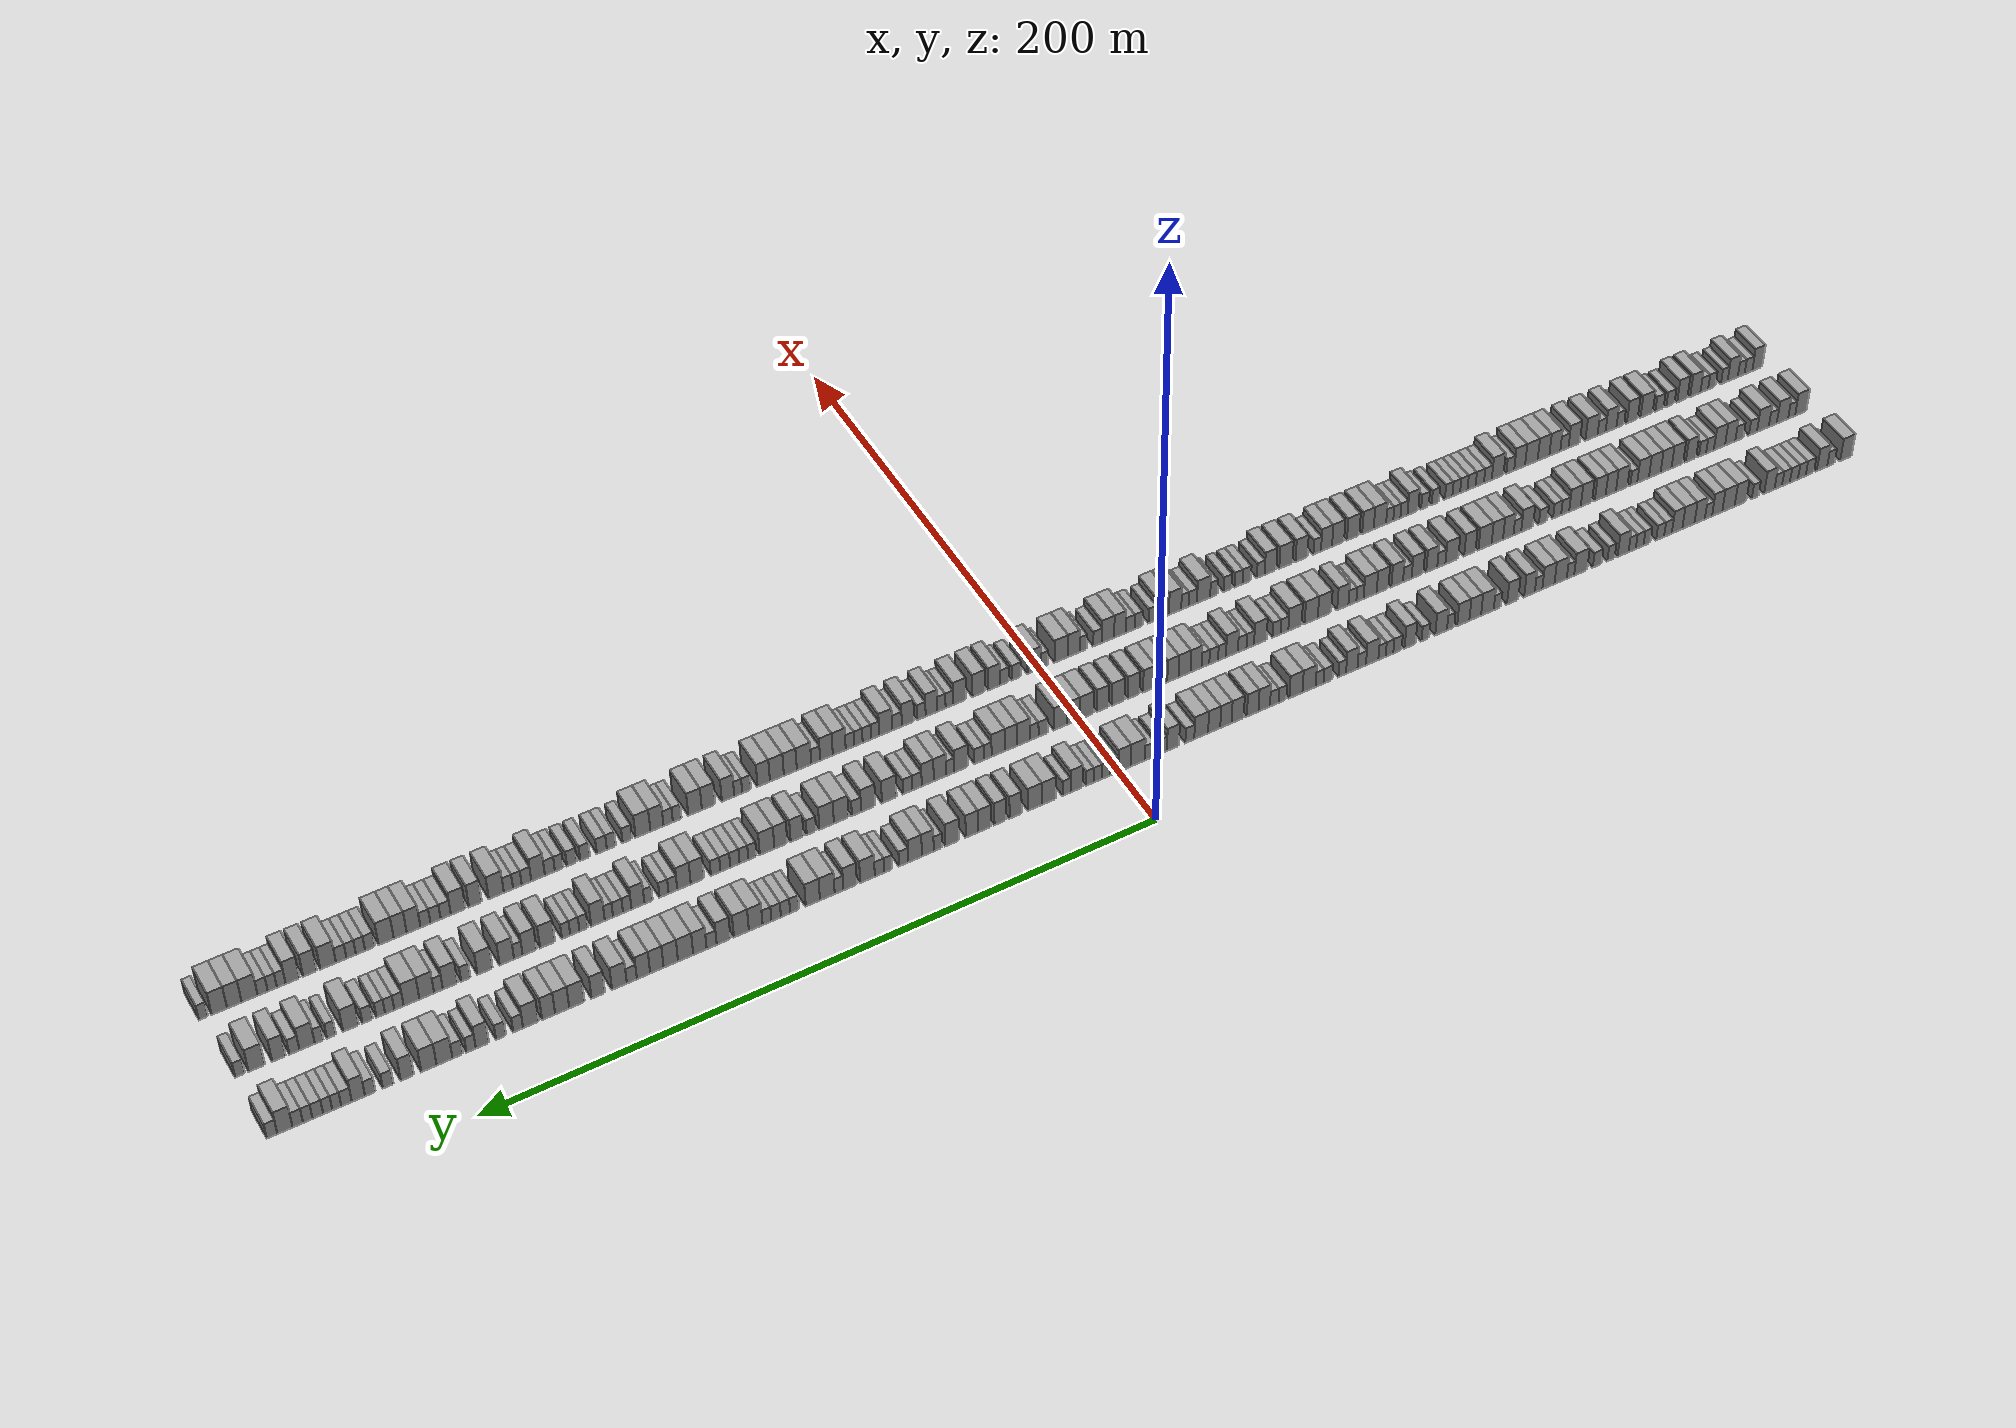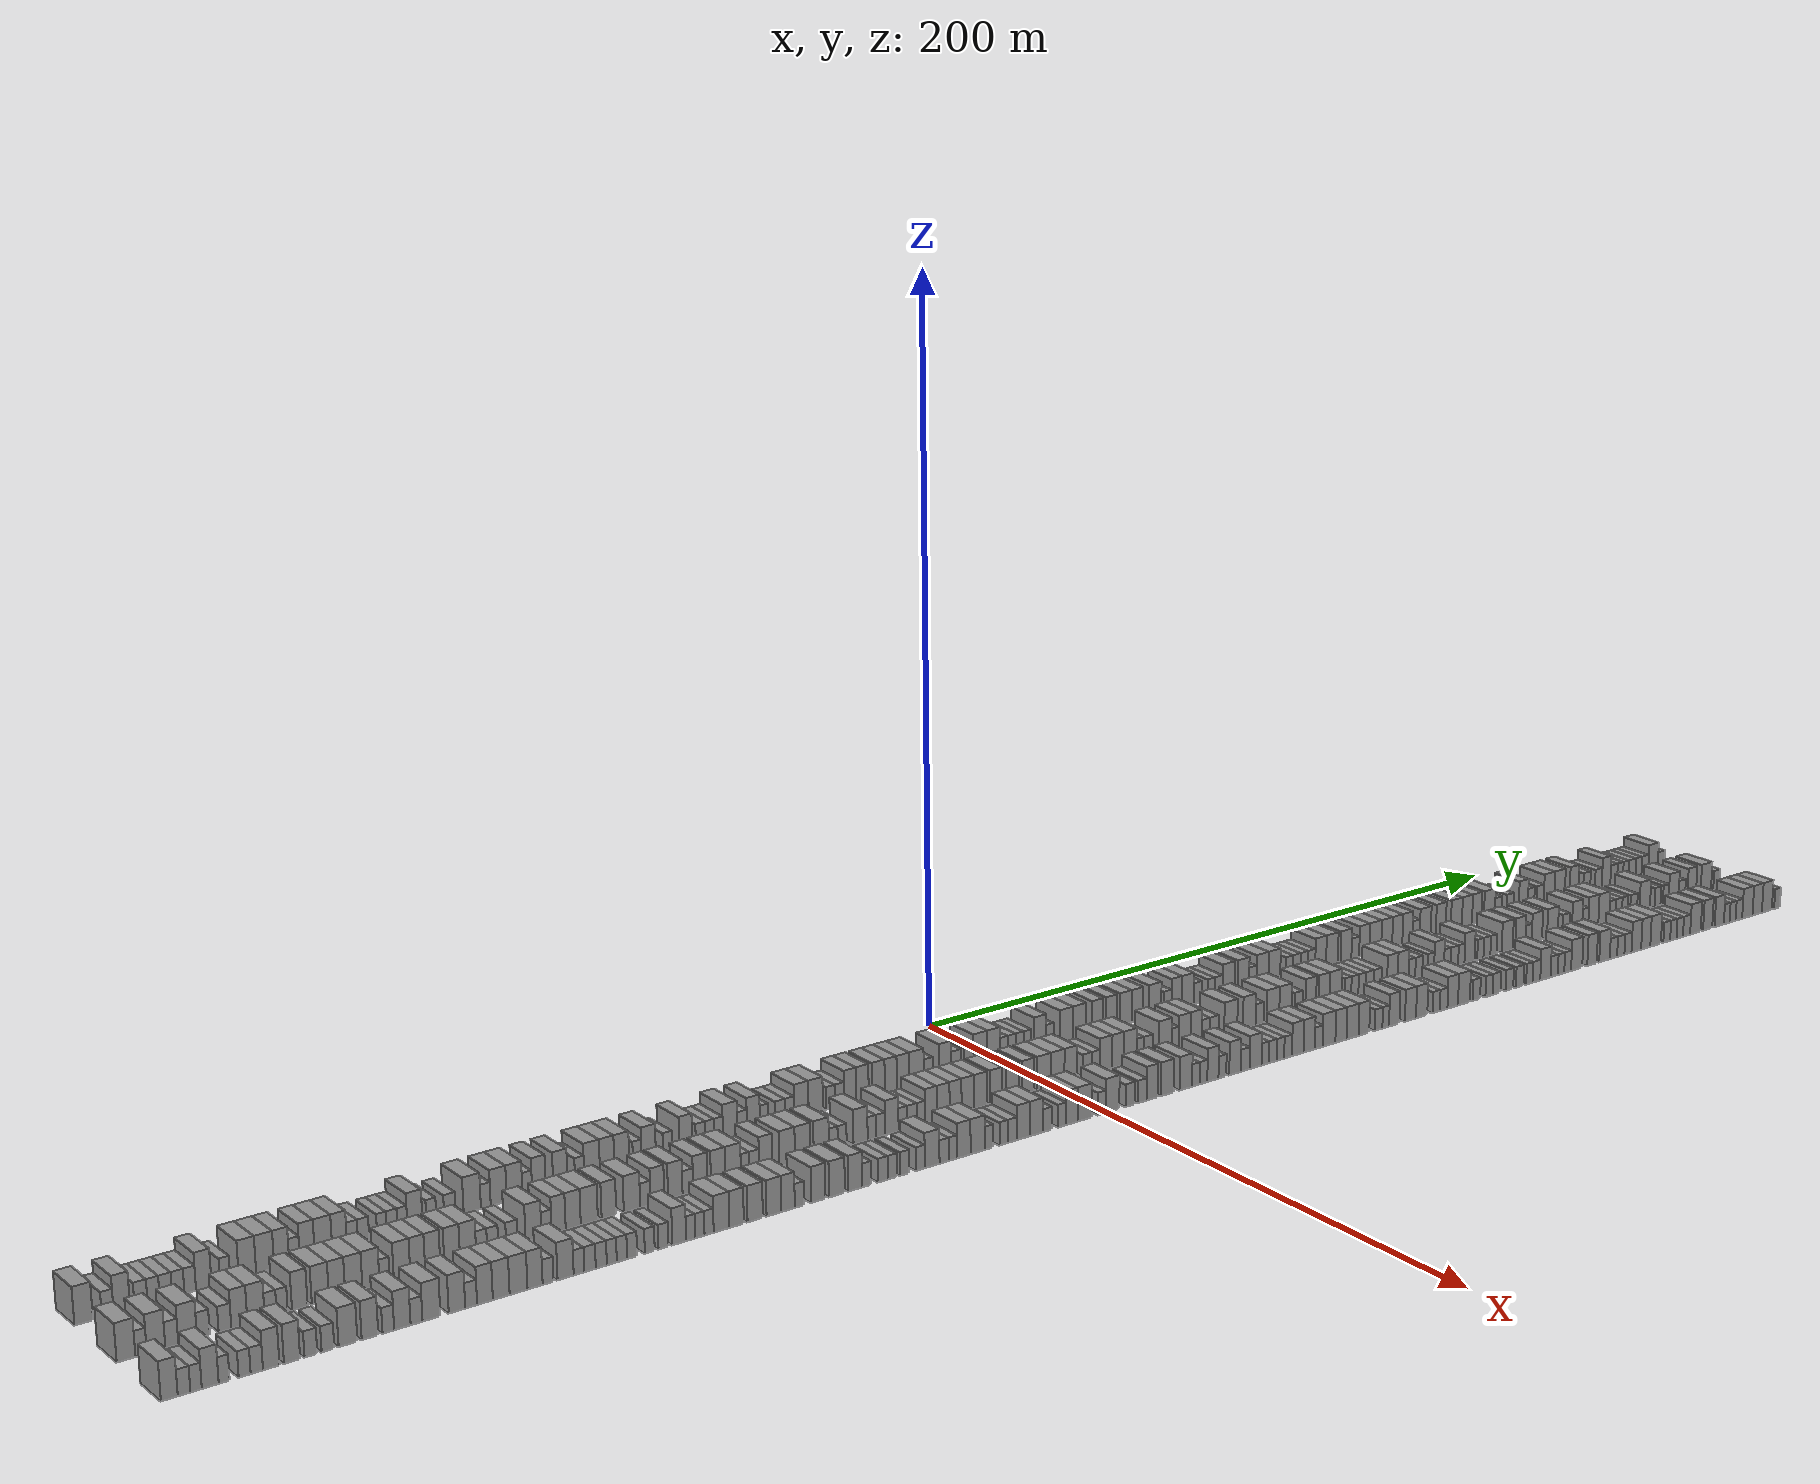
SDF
<sdf version="1.6">
 <world name="default">
  <scene>
   <sky><clouds><speed>12</speed></clouds></sky>
   <ambient>0.4 0.4 0.4 1</ambient>
   <background>0.7 0.7 0.7 1</background>
   <shadows>1</shadows>
  </scene>
  <gravity>0 0 -9.8066</gravity>
  <magnetic_field>6e-06 2.3e-05 -4.2e-05</magnetic_field>
  <physics default="0" name="default_physics" type="ode">
   <ode>
    <solver>
     <type>quick</type>
     <iters>10</iters>
     <sor>1.0</sor>
     <use_dynamic_moi_rescaling>0</use_dynamic_moi_rescaling>
    </solver>
    <constraints>
     <cfm>0</cfm>
     <erp>0.2</erp>
     <contact_max_correcting_vel>100</contact_max_correcting_vel>
     <contact_surface_layer>0.001</contact_surface_layer>
    </constraints>
   </ode>
   <max_step_size>0.004</max_step_size>
   <real_time_factor>1</real_time_factor>
   <real_time_update_rate>250</real_time_update_rate>
  </physics>
  <light name="sun" type="directional">
   <pose>0 0 10 0 0 0</pose>
   <diffuse>0.8 0.8 0.8 1</diffuse>
   <specular>0.2 0.2 0.2 1</specular>
   <attenuation>
    <range>1000</range>
    <constant>0.9</constant>
    <linear>0.01</linear>
    <quadratic>0.001</quadratic>
   </attenuation>
   <direction>-0.5 0.1 -0.9</direction>
  </light>
  <model name="building_1">
   <static>1</static>
   <pose>25.0000 -245.9093 0 0.000000 0.000000 0.000000</pose>
   <link name="link">
    <pose>0 0 4.50 0 0 0</pose>
    <collision name="collision"><geometry><box><size>10.0000 4.1814 9.0000</size></box></geometry></collision>
    <visual name="visual">
     <cast_shadows>0</cast_shadows>
     <geometry><box><size>10.0000 4.1814 9.0000</size></box></geometry>
     <material>
      <script>
       <uri>model://grey_wall/materials/scripts</uri>
       <uri>model://grey_wall/materials/textures</uri>
       <name>vrc/grey_wall</name>
      </script>
     </material>
    </visual>
   </link>
  </model>
  <model name="building_2">
   <static>1</static>
   <pose>25.0000 -240.4762 0 0.000000 0.000000 0.000000</pose>
   <link name="link">
    <pose>0 0 3.00 0 0 0</pose>
    <collision name="collision"><geometry><box><size>10.0000 2.6848 6.0000</size></box></geometry></collision>
    <visual name="visual">
     <cast_shadows>0</cast_shadows>
     <geometry><box><size>10.0000 2.6848 6.0000</size></box></geometry>
     <material>
      <script>
       <uri>model://grey_wall/materials/scripts</uri>
       <uri>model://grey_wall/materials/textures</uri>
       <name>vrc/grey_wall</name>
      </script>
     </material>
    </visual>
   </link>
  </model>
  <model name="building_3">
   <static>1</static>
   <pose>25.0000 -237.2547 0 0.000000 0.000000 0.000000</pose>
   <link name="link">
    <pose>0 0 4.50 0 0 0</pose>
    <collision name="collision"><geometry><box><size>10.0000 3.7582 9.0000</size></box></geometry></collision>
    <visual name="visual">
     <cast_shadows>0</cast_shadows>
     <geometry><box><size>10.0000 3.7582 9.0000</size></box></geometry>
     <material>
      <script>
       <uri>model://grey_wall/materials/scripts</uri>
       <uri>model://grey_wall/materials/textures</uri>
       <name>vrc/grey_wall</name>
      </script>
     </material>
    </visual>
   </link>
  </model>
  <model name="building_4">
   <static>1</static>
   <pose>25.0000 -232.8869 0 0.000000 0.000000 0.000000</pose>
   <link name="link">
    <pose>0 0 3.00 0 0 0</pose>
    <collision name="collision"><geometry><box><size>10.0000 2.9774 6.0000</size></box></geometry></collision>
    <visual name="visual">
     <cast_shadows>0</cast_shadows>
     <geometry><box><size>10.0000 2.9774 6.0000</size></box></geometry>
     <material>
      <script>
       <uri>model://grey_wall/materials/scripts</uri>
       <uri>model://grey_wall/materials/textures</uri>
       <name>vrc/grey_wall</name>
      </script>
     </material>
    </visual>
   </link>
  </model>
  <model name="building_5">
   <static>1</static>
   <pose>25.0000 -229.9949 0 0.000000 0.000000 0.000000</pose>
   <link name="link">
    <pose>0 0 3.00 0 0 0</pose>
    <collision name="collision"><geometry><box><size>10.0000 2.8066 6.0000</size></box></geometry></collision>
    <visual name="visual">
     <cast_shadows>0</cast_shadows>
     <geometry><box><size>10.0000 2.8066 6.0000</size></box></geometry>
     <material>
      <script>
       <uri>model://grey_wall/materials/scripts</uri>
       <uri>model://grey_wall/materials/textures</uri>
       <name>vrc/grey_wall</name>
      </script>
     </material>
    </visual>
   </link>
  </model>
  <model name="building_6">
   <static>1</static>
   <pose>25.0000 -227.1501 0 0.000000 0.000000 0.000000</pose>
   <link name="link">
    <pose>0 0 3.00 0 0 0</pose>
    <collision name="collision"><geometry><box><size>10.0000 2.8830 6.0000</size></box></geometry></collision>
    <visual name="visual">
     <cast_shadows>0</cast_shadows>
     <geometry><box><size>10.0000 2.8830 6.0000</size></box></geometry>
     <material>
      <script>
       <uri>model://grey_wall/materials/scripts</uri>
       <uri>model://grey_wall/materials/textures</uri>
       <name>vrc/grey_wall</name>
      </script>
     </material>
    </visual>
   </link>
  </model>
  <model name="building_7">
   <static>1</static>
   <pose>25.0000 -224.2862 0 0.000000 0.000000 0.000000</pose>
   <link name="link">
    <pose>0 0 3.00 0 0 0</pose>
    <collision name="collision"><geometry><box><size>10.0000 2.8448 6.0000</size></box></geometry></collision>
    <visual name="visual">
     <cast_shadows>0</cast_shadows>
     <geometry><box><size>10.0000 2.8448 6.0000</size></box></geometry>
     <material>
      <script>
       <uri>model://grey_wall/materials/scripts</uri>
       <uri>model://grey_wall/materials/textures</uri>
       <name>vrc/grey_wall</name>
      </script>
     </material>
    </visual>
   </link>
  </model>
  <model name="building_8">
   <static>1</static>
   <pose>25.0000 -221.5211 0 0.000000 0.000000 0.000000</pose>
   <link name="link">
    <pose>0 0 3.00 0 0 0</pose>
    <collision name="collision"><geometry><box><size>10.0000 2.6853 6.0000</size></box></geometry></collision>
    <visual name="visual">
     <cast_shadows>0</cast_shadows>
     <geometry><box><size>10.0000 2.6853 6.0000</size></box></geometry>
     <material>
      <script>
       <uri>model://grey_wall/materials/scripts</uri>
       <uri>model://grey_wall/materials/textures</uri>
       <name>vrc/grey_wall</name>
      </script>
     </material>
    </visual>
   </link>
  </model>
  <model name="building_9">
   <static>1</static>
   <pose>25.0000 -218.3408 0 0.000000 0.000000 0.000000</pose>
   <link name="link">
    <pose>0 0 4.50 0 0 0</pose>
    <collision name="collision"><geometry><box><size>10.0000 3.6753 9.0000</size></box></geometry></collision>
    <visual name="visual">
     <cast_shadows>0</cast_shadows>
     <geometry><box><size>10.0000 3.6753 9.0000</size></box></geometry>
     <material>
      <script>
       <uri>model://grey_wall/materials/scripts</uri>
       <uri>model://grey_wall/materials/textures</uri>
       <name>vrc/grey_wall</name>
      </script>
     </material>
    </visual>
   </link>
  </model>
  <model name="building_10">
   <static>1</static>
   <pose>25.0000 -213.2970 0 0.000000 0.000000 0.000000</pose>
   <link name="link">
    <pose>0 0 3.00 0 0 0</pose>
    <collision name="collision"><geometry><box><size>10.0000 2.4124 6.0000</size></box></geometry></collision>
    <visual name="visual">
     <cast_shadows>0</cast_shadows>
     <geometry><box><size>10.0000 2.4124 6.0000</size></box></geometry>
     <material>
      <script>
       <uri>model://grey_wall/materials/scripts</uri>
       <uri>model://grey_wall/materials/textures</uri>
       <name>vrc/grey_wall</name>
      </script>
     </material>
    </visual>
   </link>
  </model>
  <model name="building_11">
   <static>1</static>
   <pose>25.0000 -208.0230 0 0.000000 0.000000 0.000000</pose>
   <link name="link">
    <pose>0 0 4.50 0 0 0</pose>
    <collision name="collision"><geometry><box><size>10.0000 4.1356 9.0000</size></box></geometry></collision>
    <visual name="visual">
     <cast_shadows>0</cast_shadows>
     <geometry><box><size>10.0000 4.1356 9.0000</size></box></geometry>
     <material>
      <script>
       <uri>model://grey_wall/materials/scripts</uri>
       <uri>model://grey_wall/materials/textures</uri>
       <name>vrc/grey_wall</name>
      </script>
     </material>
    </visual>
   </link>
  </model>
  <model name="building_12">
   <static>1</static>
   <pose>25.0000 -203.7752 0 0.000000 0.000000 0.000000</pose>
   <link name="link">
    <pose>0 0 4.50 0 0 0</pose>
    <collision name="collision"><geometry><box><size>10.0000 4.3599 9.0000</size></box></geometry></collision>
    <visual name="visual">
     <cast_shadows>0</cast_shadows>
     <geometry><box><size>10.0000 4.3599 9.0000</size></box></geometry>
     <material>
      <script>
       <uri>model://grey_wall/materials/scripts</uri>
       <uri>model://grey_wall/materials/textures</uri>
       <name>vrc/grey_wall</name>
      </script>
     </material>
    </visual>
   </link>
  </model>
  <model name="building_13">
   <static>1</static>
   <pose>25.0000 -199.7875 0 0.000000 0.000000 0.000000</pose>
   <link name="link">
    <pose>0 0 4.50 0 0 0</pose>
    <collision name="collision"><geometry><box><size>10.0000 3.6156 9.0000</size></box></geometry></collision>
    <visual name="visual">
     <cast_shadows>0</cast_shadows>
     <geometry><box><size>10.0000 3.6156 9.0000</size></box></geometry>
     <material>
      <script>
       <uri>model://grey_wall/materials/scripts</uri>
       <uri>model://grey_wall/materials/textures</uri>
       <name>vrc/grey_wall</name>
      </script>
     </material>
    </visual>
   </link>
  </model>
  <model name="building_14">
   <static>1</static>
   <pose>25.0000 -196.6971 0 0.000000 0.000000 0.000000</pose>
   <link name="link">
    <pose>0 0 3.00 0 0 0</pose>
    <collision name="collision"><geometry><box><size>10.0000 2.5653 6.0000</size></box></geometry></collision>
    <visual name="visual">
     <cast_shadows>0</cast_shadows>
     <geometry><box><size>10.0000 2.5653 6.0000</size></box></geometry>
     <material>
      <script>
       <uri>model://grey_wall/materials/scripts</uri>
       <uri>model://grey_wall/materials/textures</uri>
       <name>vrc/grey_wall</name>
      </script>
     </material>
    </visual>
   </link>
  </model>
  <model name="building_15">
   <static>1</static>
   <pose>25.0000 -193.5860 0 0.000000 0.000000 0.000000</pose>
   <link name="link">
    <pose>0 0 4.50 0 0 0</pose>
    <collision name="collision"><geometry><box><size>10.0000 3.6568 9.0000</size></box></geometry></collision>
    <visual name="visual">
     <cast_shadows>0</cast_shadows>
     <geometry><box><size>10.0000 3.6568 9.0000</size></box></geometry>
     <material>
      <script>
       <uri>model://grey_wall/materials/scripts</uri>
       <uri>model://grey_wall/materials/textures</uri>
       <name>vrc/grey_wall</name>
      </script>
     </material>
    </visual>
   </link>
  </model>
  <model name="building_16">
   <static>1</static>
   <pose>25.0000 -189.6194 0 0.000000 0.000000 0.000000</pose>
   <link name="link">
    <pose>0 0 4.50 0 0 0</pose>
    <collision name="collision"><geometry><box><size>10.0000 4.2762 9.0000</size></box></geometry></collision>
    <visual name="visual">
     <cast_shadows>0</cast_shadows>
     <geometry><box><size>10.0000 4.2762 9.0000</size></box></geometry>
     <material>
      <script>
       <uri>model://grey_wall/materials/scripts</uri>
       <uri>model://grey_wall/materials/textures</uri>
       <name>vrc/grey_wall</name>
      </script>
     </material>
    </visual>
   </link>
  </model>
  <model name="building_17">
   <static>1</static>
   <pose>25.0000 -185.6479 0 0.000000 0.000000 0.000000</pose>
   <link name="link">
    <pose>0 0 4.50 0 0 0</pose>
    <collision name="collision"><geometry><box><size>10.0000 3.6668 9.0000</size></box></geometry></collision>
    <visual name="visual">
     <cast_shadows>0</cast_shadows>
     <geometry><box><size>10.0000 3.6668 9.0000</size></box></geometry>
     <material>
      <script>
       <uri>model://grey_wall/materials/scripts</uri>
       <uri>model://grey_wall/materials/textures</uri>
       <name>vrc/grey_wall</name>
      </script>
     </material>
    </visual>
   </link>
  </model>
  <model name="building_18">
   <static>1</static>
   <pose>25.0000 -182.4574 0 0.000000 0.000000 0.000000</pose>
   <link name="link">
    <pose>0 0 3.00 0 0 0</pose>
    <collision name="collision"><geometry><box><size>10.0000 2.7142 6.0000</size></box></geometry></collision>
    <visual name="visual">
     <cast_shadows>0</cast_shadows>
     <geometry><box><size>10.0000 2.7142 6.0000</size></box></geometry>
     <material>
      <script>
       <uri>model://grey_wall/materials/scripts</uri>
       <uri>model://grey_wall/materials/textures</uri>
       <name>vrc/grey_wall</name>
      </script>
     </material>
    </visual>
   </link>
  </model>
  <model name="building_19">
   <static>1</static>
   <pose>25.0000 -179.7109 0 0.000000 0.000000 0.000000</pose>
   <link name="link">
    <pose>0 0 3.00 0 0 0</pose>
    <collision name="collision"><geometry><box><size>10.0000 2.7788 6.0000</size></box></geometry></collision>
    <visual name="visual">
     <cast_shadows>0</cast_shadows>
     <geometry><box><size>10.0000 2.7788 6.0000</size></box></geometry>
     <material>
      <script>
       <uri>model://grey_wall/materials/scripts</uri>
       <uri>model://grey_wall/materials/textures</uri>
       <name>vrc/grey_wall</name>
      </script>
     </material>
    </visual>
   </link>
  </model>
  <model name="building_20">
   <static>1</static>
   <pose>25.0000 -175.1163 0 0.000000 0.000000 0.000000</pose>
   <link name="link">
    <pose>0 0 3.00 0 0 0</pose>
    <collision name="collision"><geometry><box><size>10.0000 2.4105 6.0000</size></box></geometry></collision>
    <visual name="visual">
     <cast_shadows>0</cast_shadows>
     <geometry><box><size>10.0000 2.4105 6.0000</size></box></geometry>
     <material>
      <script>
       <uri>model://grey_wall/materials/scripts</uri>
       <uri>model://grey_wall/materials/textures</uri>
       <name>vrc/grey_wall</name>
      </script>
     </material>
    </visual>
   </link>
  </model>
  <model name="building_21">
   <static>1</static>
   <pose>25.0000 -172.5600 0 0.000000 0.000000 0.000000</pose>
   <link name="link">
    <pose>0 0 3.00 0 0 0</pose>
    <collision name="collision"><geometry><box><size>10.0000 2.7021 6.0000</size></box></geometry></collision>
    <visual name="visual">
     <cast_shadows>0</cast_shadows>
     <geometry><box><size>10.0000 2.7021 6.0000</size></box></geometry>
     <material>
      <script>
       <uri>model://grey_wall/materials/scripts</uri>
       <uri>model://grey_wall/materials/textures</uri>
       <name>vrc/grey_wall</name>
      </script>
     </material>
    </visual>
   </link>
  </model>
  <model name="building_22">
   <static>1</static>
   <pose>25.0000 -169.9578 0 0.000000 0.000000 0.000000</pose>
   <link name="link">
    <pose>0 0 3.00 0 0 0</pose>
    <collision name="collision"><geometry><box><size>10.0000 2.5024 6.0000</size></box></geometry></collision>
    <visual name="visual">
     <cast_shadows>0</cast_shadows>
     <geometry><box><size>10.0000 2.5024 6.0000</size></box></geometry>
     <material>
      <script>
       <uri>model://grey_wall/materials/scripts</uri>
       <uri>model://grey_wall/materials/textures</uri>
       <name>vrc/grey_wall</name>
      </script>
     </material>
    </visual>
   </link>
  </model>
  <model name="building_23">
   <static>1</static>
   <pose>25.0000 -166.7924 0 0.000000 0.000000 0.000000</pose>
   <link name="link">
    <pose>0 0 4.50 0 0 0</pose>
    <collision name="collision"><geometry><box><size>10.0000 3.8284 9.0000</size></box></geometry></collision>
    <visual name="visual">
     <cast_shadows>0</cast_shadows>
     <geometry><box><size>10.0000 3.8284 9.0000</size></box></geometry>
     <material>
      <script>
       <uri>model://grey_wall/materials/scripts</uri>
       <uri>model://grey_wall/materials/textures</uri>
       <name>vrc/grey_wall</name>
      </script>
     </material>
    </visual>
   </link>
  </model>
  <model name="building_24">
   <static>1</static>
   <pose>25.0000 -162.6117 0 0.000000 0.000000 0.000000</pose>
   <link name="link">
    <pose>0 0 3.00 0 0 0</pose>
    <collision name="collision"><geometry><box><size>10.0000 2.5330 6.0000</size></box></geometry></collision>
    <visual name="visual">
     <cast_shadows>0</cast_shadows>
     <geometry><box><size>10.0000 2.5330 6.0000</size></box></geometry>
     <material>
      <script>
       <uri>model://grey_wall/materials/scripts</uri>
       <uri>model://grey_wall/materials/textures</uri>
       <name>vrc/grey_wall</name>
      </script>
     </material>
    </visual>
   </link>
  </model>
  <model name="building_25">
   <static>1</static>
   <pose>25.0000 -157.8516 0 0.000000 0.000000 0.000000</pose>
   <link name="link">
    <pose>0 0 3.00 0 0 0</pose>
    <collision name="collision"><geometry><box><size>10.0000 2.9871 6.0000</size></box></geometry></collision>
    <visual name="visual">
     <cast_shadows>0</cast_shadows>
     <geometry><box><size>10.0000 2.9871 6.0000</size></box></geometry>
     <material>
      <script>
       <uri>model://grey_wall/materials/scripts</uri>
       <uri>model://grey_wall/materials/textures</uri>
       <name>vrc/grey_wall</name>
      </script>
     </material>
    </visual>
   </link>
  </model>
  <model name="building_26">
   <static>1</static>
   <pose>25.0000 -152.1176 0 0.000000 0.000000 0.000000</pose>
   <link name="link">
    <pose>0 0 4.50 0 0 0</pose>
    <collision name="collision"><geometry><box><size>10.0000 4.4809 9.0000</size></box></geometry></collision>
    <visual name="visual">
     <cast_shadows>0</cast_shadows>
     <geometry><box><size>10.0000 4.4809 9.0000</size></box></geometry>
     <material>
      <script>
       <uri>model://grey_wall/materials/scripts</uri>
       <uri>model://grey_wall/materials/textures</uri>
       <name>vrc/grey_wall</name>
      </script>
     </material>
    </visual>
   </link>
  </model>
  <model name="building_27">
   <static>1</static>
   <pose>25.0000 -148.6011 0 0.000000 0.000000 0.000000</pose>
   <link name="link">
    <pose>0 0 3.00 0 0 0</pose>
    <collision name="collision"><geometry><box><size>10.0000 2.5522 6.0000</size></box></geometry></collision>
    <visual name="visual">
     <cast_shadows>0</cast_shadows>
     <geometry><box><size>10.0000 2.5522 6.0000</size></box></geometry>
     <material>
      <script>
       <uri>model://grey_wall/materials/scripts</uri>
       <uri>model://grey_wall/materials/textures</uri>
       <name>vrc/grey_wall</name>
      </script>
     </material>
    </visual>
   </link>
  </model>
  <model name="building_28">
   <static>1</static>
   <pose>25.0000 -145.2141 0 0.000000 0.000000 0.000000</pose>
   <link name="link">
    <pose>0 0 4.50 0 0 0</pose>
    <collision name="collision"><geometry><box><size>10.0000 4.2217 9.0000</size></box></geometry></collision>
    <visual name="visual">
     <cast_shadows>0</cast_shadows>
     <geometry><box><size>10.0000 4.2217 9.0000</size></box></geometry>
     <material>
      <script>
       <uri>model://grey_wall/materials/scripts</uri>
       <uri>model://grey_wall/materials/textures</uri>
       <name>vrc/grey_wall</name>
      </script>
     </material>
    </visual>
   </link>
  </model>
  <model name="building_29">
   <static>1</static>
   <pose>25.0000 -141.0265 0 0.000000 0.000000 0.000000</pose>
   <link name="link">
    <pose>0 0 4.50 0 0 0</pose>
    <collision name="collision"><geometry><box><size>10.0000 4.1534 9.0000</size></box></geometry></collision>
    <visual name="visual">
     <cast_shadows>0</cast_shadows>
     <geometry><box><size>10.0000 4.1534 9.0000</size></box></geometry>
     <material>
      <script>
       <uri>model://grey_wall/materials/scripts</uri>
       <uri>model://grey_wall/materials/textures</uri>
       <name>vrc/grey_wall</name>
      </script>
     </material>
    </visual>
   </link>
  </model>
  <model name="building_30">
   <static>1</static>
   <pose>25.0000 -137.6640 0 0.000000 0.000000 0.000000</pose>
   <link name="link">
    <pose>0 0 3.00 0 0 0</pose>
    <collision name="collision"><geometry><box><size>10.0000 2.5716 6.0000</size></box></geometry></collision>
    <visual name="visual">
     <cast_shadows>0</cast_shadows>
     <geometry><box><size>10.0000 2.5716 6.0000</size></box></geometry>
     <material>
      <script>
       <uri>model://grey_wall/materials/scripts</uri>
       <uri>model://grey_wall/materials/textures</uri>
       <name>vrc/grey_wall</name>
      </script>
     </material>
    </visual>
   </link>
  </model>
  <model name="building_31">
   <static>1</static>
   <pose>25.0000 -134.5662 0 0.000000 0.000000 0.000000</pose>
   <link name="link">
    <pose>0 0 4.50 0 0 0</pose>
    <collision name="collision"><geometry><box><size>10.0000 3.6239 9.0000</size></box></geometry></collision>
    <visual name="visual">
     <cast_shadows>0</cast_shadows>
     <geometry><box><size>10.0000 3.6239 9.0000</size></box></geometry>
     <material>
      <script>
       <uri>model://grey_wall/materials/scripts</uri>
       <uri>model://grey_wall/materials/textures</uri>
       <name>vrc/grey_wall</name>
      </script>
     </material>
    </visual>
   </link>
  </model>
  <model name="building_32">
   <static>1</static>
   <pose>25.0000 -128.8275 0 0.000000 0.000000 0.000000</pose>
   <link name="link">
    <pose>0 0 4.50 0 0 0</pose>
    <collision name="collision"><geometry><box><size>10.0000 3.8537 9.0000</size></box></geometry></collision>
    <visual name="visual">
     <cast_shadows>0</cast_shadows>
     <geometry><box><size>10.0000 3.8537 9.0000</size></box></geometry>
     <material>
      <script>
       <uri>model://grey_wall/materials/scripts</uri>
       <uri>model://grey_wall/materials/textures</uri>
       <name>vrc/grey_wall</name>
      </script>
     </material>
    </visual>
   </link>
  </model>
  <model name="building_33">
   <static>1</static>
   <pose>25.0000 -123.6524 0 0.000000 0.000000 0.000000</pose>
   <link name="link">
    <pose>0 0 3.00 0 0 0</pose>
    <collision name="collision"><geometry><box><size>10.0000 2.4964 6.0000</size></box></geometry></collision>
    <visual name="visual">
     <cast_shadows>0</cast_shadows>
     <geometry><box><size>10.0000 2.4964 6.0000</size></box></geometry>
     <material>
      <script>
       <uri>model://grey_wall/materials/scripts</uri>
       <uri>model://grey_wall/materials/textures</uri>
       <name>vrc/grey_wall</name>
      </script>
     </material>
    </visual>
   </link>
  </model>
  <model name="building_34">
   <static>1</static>
   <pose>25.0000 -120.2698 0 0.000000 0.000000 0.000000</pose>
   <link name="link">
    <pose>0 0 4.50 0 0 0</pose>
    <collision name="collision"><geometry><box><size>10.0000 4.2689 9.0000</size></box></geometry></collision>
    <visual name="visual">
     <cast_shadows>0</cast_shadows>
     <geometry><box><size>10.0000 4.2689 9.0000</size></box></geometry>
     <material>
      <script>
       <uri>model://grey_wall/materials/scripts</uri>
       <uri>model://grey_wall/materials/textures</uri>
       <name>vrc/grey_wall</name>
      </script>
     </material>
    </visual>
   </link>
  </model>
  <model name="building_35">
   <static>1</static>
   <pose>25.0000 -116.1545 0 0.000000 0.000000 0.000000</pose>
   <link name="link">
    <pose>0 0 4.50 0 0 0</pose>
    <collision name="collision"><geometry><box><size>10.0000 3.9617 9.0000</size></box></geometry></collision>
    <visual name="visual">
     <cast_shadows>0</cast_shadows>
     <geometry><box><size>10.0000 3.9617 9.0000</size></box></geometry>
     <material>
      <script>
       <uri>model://grey_wall/materials/scripts</uri>
       <uri>model://grey_wall/materials/textures</uri>
       <name>vrc/grey_wall</name>
      </script>
     </material>
    </visual>
   </link>
  </model>
  <model name="building_36">
   <static>1</static>
   <pose>25.0000 -112.1218 0 0.000000 0.000000 0.000000</pose>
   <link name="link">
    <pose>0 0 4.50 0 0 0</pose>
    <collision name="collision"><geometry><box><size>10.0000 4.1037 9.0000</size></box></geometry></collision>
    <visual name="visual">
     <cast_shadows>0</cast_shadows>
     <geometry><box><size>10.0000 4.1037 9.0000</size></box></geometry>
     <material>
      <script>
       <uri>model://grey_wall/materials/scripts</uri>
       <uri>model://grey_wall/materials/textures</uri>
       <name>vrc/grey_wall</name>
      </script>
     </material>
    </visual>
   </link>
  </model>
  <model name="building_37">
   <static>1</static>
   <pose>25.0000 -107.8564 0 0.000000 0.000000 0.000000</pose>
   <link name="link">
    <pose>0 0 3.00 0 0 0</pose>
    <collision name="collision"><geometry><box><size>10.0000 2.4271 6.0000</size></box></geometry></collision>
    <visual name="visual">
     <cast_shadows>0</cast_shadows>
     <geometry><box><size>10.0000 2.4271 6.0000</size></box></geometry>
     <material>
      <script>
       <uri>model://grey_wall/materials/scripts</uri>
       <uri>model://grey_wall/materials/textures</uri>
       <name>vrc/grey_wall</name>
      </script>
     </material>
    </visual>
   </link>
  </model>
  <model name="building_38">
   <static>1</static>
   <pose>25.0000 -104.6770 0 0.000000 0.000000 0.000000</pose>
   <link name="link">
    <pose>0 0 4.50 0 0 0</pose>
    <collision name="collision"><geometry><box><size>10.0000 3.9317 9.0000</size></box></geometry></collision>
    <visual name="visual">
     <cast_shadows>0</cast_shadows>
     <geometry><box><size>10.0000 3.9317 9.0000</size></box></geometry>
     <material>
      <script>
       <uri>model://grey_wall/materials/scripts</uri>
       <uri>model://grey_wall/materials/textures</uri>
       <name>vrc/grey_wall</name>
      </script>
     </material>
    </visual>
   </link>
  </model>
  <model name="building_39">
   <static>1</static>
   <pose>25.0000 -99.4167 0 0.000000 0.000000 0.000000</pose>
   <link name="link">
    <pose>0 0 3.00 0 0 0</pose>
    <collision name="collision"><geometry><box><size>10.0000 2.5888 6.0000</size></box></geometry></collision>
    <visual name="visual">
     <cast_shadows>0</cast_shadows>
     <geometry><box><size>10.0000 2.5888 6.0000</size></box></geometry>
     <material>
      <script>
       <uri>model://grey_wall/materials/scripts</uri>
       <uri>model://grey_wall/materials/textures</uri>
       <name>vrc/grey_wall</name>
      </script>
     </material>
    </visual>
   </link>
  </model>
  <model name="building_40">
   <static>1</static>
   <pose>25.0000 -94.3034 0 0.000000 0.000000 0.000000</pose>
   <link name="link">
    <pose>0 0 4.50 0 0 0</pose>
    <collision name="collision"><geometry><box><size>10.0000 3.6380 9.0000</size></box></geometry></collision>
    <visual name="visual">
     <cast_shadows>0</cast_shadows>
     <geometry><box><size>10.0000 3.6380 9.0000</size></box></geometry>
     <material>
      <script>
       <uri>model://grey_wall/materials/scripts</uri>
       <uri>model://grey_wall/materials/textures</uri>
       <name>vrc/grey_wall</name>
      </script>
     </material>
    </visual>
   </link>
  </model>
  <model name="building_41">
   <static>1</static>
   <pose>25.0000 -90.0918 0 0.000000 0.000000 0.000000</pose>
   <link name="link">
    <pose>0 0 3.00 0 0 0</pose>
    <collision name="collision"><geometry><box><size>10.0000 2.7851 6.0000</size></box></geometry></collision>
    <visual name="visual">
     <cast_shadows>0</cast_shadows>
     <geometry><box><size>10.0000 2.7851 6.0000</size></box></geometry>
     <material>
      <script>
       <uri>model://grey_wall/materials/scripts</uri>
       <uri>model://grey_wall/materials/textures</uri>
       <name>vrc/grey_wall</name>
      </script>
     </material>
    </visual>
   </link>
  </model>
  <model name="building_42">
   <static>1</static>
   <pose>25.0000 -87.4469 0 0.000000 0.000000 0.000000</pose>
   <link name="link">
    <pose>0 0 3.00 0 0 0</pose>
    <collision name="collision"><geometry><box><size>10.0000 2.5049 6.0000</size></box></geometry></collision>
    <visual name="visual">
     <cast_shadows>0</cast_shadows>
     <geometry><box><size>10.0000 2.5049 6.0000</size></box></geometry>
     <material>
      <script>
       <uri>model://grey_wall/materials/scripts</uri>
       <uri>model://grey_wall/materials/textures</uri>
       <name>vrc/grey_wall</name>
      </script>
     </material>
    </visual>
   </link>
  </model>
  <model name="building_43">
   <static>1</static>
   <pose>25.0000 -84.9768 0 0.000000 0.000000 0.000000</pose>
   <link name="link">
    <pose>0 0 3.00 0 0 0</pose>
    <collision name="collision"><geometry><box><size>10.0000 2.4352 6.0000</size></box></geometry></collision>
    <visual name="visual">
     <cast_shadows>0</cast_shadows>
     <geometry><box><size>10.0000 2.4352 6.0000</size></box></geometry>
     <material>
      <script>
       <uri>model://grey_wall/materials/scripts</uri>
       <uri>model://grey_wall/materials/textures</uri>
       <name>vrc/grey_wall</name>
      </script>
     </material>
    </visual>
   </link>
  </model>
  <model name="building_44">
   <static>1</static>
   <pose>25.0000 -81.7078 0 0.000000 0.000000 0.000000</pose>
   <link name="link">
    <pose>0 0 4.50 0 0 0</pose>
    <collision name="collision"><geometry><box><size>10.0000 4.1026 9.0000</size></box></geometry></collision>
    <visual name="visual">
     <cast_shadows>0</cast_shadows>
     <geometry><box><size>10.0000 4.1026 9.0000</size></box></geometry>
     <material>
      <script>
       <uri>model://grey_wall/materials/scripts</uri>
       <uri>model://grey_wall/materials/textures</uri>
       <name>vrc/grey_wall</name>
      </script>
     </material>
    </visual>
   </link>
  </model>
  <model name="building_45">
   <static>1</static>
   <pose>25.0000 -78.2476 0 0.000000 0.000000 0.000000</pose>
   <link name="link">
    <pose>0 0 3.00 0 0 0</pose>
    <collision name="collision"><geometry><box><size>10.0000 2.8178 6.0000</size></box></geometry></collision>
    <visual name="visual">
     <cast_shadows>0</cast_shadows>
     <geometry><box><size>10.0000 2.8178 6.0000</size></box></geometry>
     <material>
      <script>
       <uri>model://grey_wall/materials/scripts</uri>
       <uri>model://grey_wall/materials/textures</uri>
       <name>vrc/grey_wall</name>
      </script>
     </material>
    </visual>
   </link>
  </model>
  <model name="building_46">
   <static>1</static>
   <pose>25.0000 -74.9602 0 0.000000 0.000000 0.000000</pose>
   <link name="link">
    <pose>0 0 4.50 0 0 0</pose>
    <collision name="collision"><geometry><box><size>10.0000 3.7570 9.0000</size></box></geometry></collision>
    <visual name="visual">
     <cast_shadows>0</cast_shadows>
     <geometry><box><size>10.0000 3.7570 9.0000</size></box></geometry>
     <material>
      <script>
       <uri>model://grey_wall/materials/scripts</uri>
       <uri>model://grey_wall/materials/textures</uri>
       <name>vrc/grey_wall</name>
      </script>
     </material>
    </visual>
   </link>
  </model>
  <model name="building_47">
   <static>1</static>
   <pose>25.0000 -71.8492 0 0.000000 0.000000 0.000000</pose>
   <link name="link">
    <pose>0 0 3.00 0 0 0</pose>
    <collision name="collision"><geometry><box><size>10.0000 2.4650 6.0000</size></box></geometry></collision>
    <visual name="visual">
     <cast_shadows>0</cast_shadows>
     <geometry><box><size>10.0000 2.4650 6.0000</size></box></geometry>
     <material>
      <script>
       <uri>model://grey_wall/materials/scripts</uri>
       <uri>model://grey_wall/materials/textures</uri>
       <name>vrc/grey_wall</name>
      </script>
     </material>
    </visual>
   </link>
  </model>
  <model name="building_48">
   <static>1</static>
   <pose>25.0000 -67.1630 0 0.000000 0.000000 0.000000</pose>
   <link name="link">
    <pose>0 0 3.00 0 0 0</pose>
    <collision name="collision"><geometry><box><size>10.0000 2.9074 6.0000</size></box></geometry></collision>
    <visual name="visual">
     <cast_shadows>0</cast_shadows>
     <geometry><box><size>10.0000 2.9074 6.0000</size></box></geometry>
     <material>
      <script>
       <uri>model://grey_wall/materials/scripts</uri>
       <uri>model://grey_wall/materials/textures</uri>
       <name>vrc/grey_wall</name>
      </script>
     </material>
    </visual>
   </link>
  </model>
  <model name="building_49">
   <static>1</static>
   <pose>25.0000 -64.3875 0 0.000000 0.000000 0.000000</pose>
   <link name="link">
    <pose>0 0 3.00 0 0 0</pose>
    <collision name="collision"><geometry><box><size>10.0000 2.6436 6.0000</size></box></geometry></collision>
    <visual name="visual">
     <cast_shadows>0</cast_shadows>
     <geometry><box><size>10.0000 2.6436 6.0000</size></box></geometry>
     <material>
      <script>
       <uri>model://grey_wall/materials/scripts</uri>
       <uri>model://grey_wall/materials/textures</uri>
       <name>vrc/grey_wall</name>
      </script>
     </material>
    </visual>
   </link>
  </model>
  <model name="building_50">
   <static>1</static>
   <pose>25.0000 -60.9293 0 0.000000 0.000000 0.000000</pose>
   <link name="link">
    <pose>0 0 4.50 0 0 0</pose>
    <collision name="collision"><geometry><box><size>10.0000 4.2727 9.0000</size></box></geometry></collision>
    <visual name="visual">
     <cast_shadows>0</cast_shadows>
     <geometry><box><size>10.0000 4.2727 9.0000</size></box></geometry>
     <material>
      <script>
       <uri>model://grey_wall/materials/scripts</uri>
       <uri>model://grey_wall/materials/textures</uri>
       <name>vrc/grey_wall</name>
      </script>
     </material>
    </visual>
   </link>
  </model>
  <model name="building_51">
   <static>1</static>
   <pose>25.0000 -56.6672 0 0.000000 0.000000 0.000000</pose>
   <link name="link">
    <pose>0 0 4.50 0 0 0</pose>
    <collision name="collision"><geometry><box><size>10.0000 4.2515 9.0000</size></box></geometry></collision>
    <visual name="visual">
     <cast_shadows>0</cast_shadows>
     <geometry><box><size>10.0000 4.2515 9.0000</size></box></geometry>
     <material>
      <script>
       <uri>model://grey_wall/materials/scripts</uri>
       <uri>model://grey_wall/materials/textures</uri>
       <name>vrc/grey_wall</name>
      </script>
     </material>
    </visual>
   </link>
  </model>
  <model name="building_52">
   <static>1</static>
   <pose>25.0000 -52.2682 0 0.000000 0.000000 0.000000</pose>
   <link name="link">
    <pose>0 0 3.00 0 0 0</pose>
    <collision name="collision"><geometry><box><size>10.0000 2.5465 6.0000</size></box></geometry></collision>
    <visual name="visual">
     <cast_shadows>0</cast_shadows>
     <geometry><box><size>10.0000 2.5465 6.0000</size></box></geometry>
     <material>
      <script>
       <uri>model://grey_wall/materials/scripts</uri>
       <uri>model://grey_wall/materials/textures</uri>
       <name>vrc/grey_wall</name>
      </script>
     </material>
    </visual>
   </link>
  </model>
  <model name="building_53">
   <static>1</static>
   <pose>25.0000 -49.6082 0 0.000000 0.000000 0.000000</pose>
   <link name="link">
    <pose>0 0 3.00 0 0 0</pose>
    <collision name="collision"><geometry><box><size>10.0000 2.7734 6.0000</size></box></geometry></collision>
    <visual name="visual">
     <cast_shadows>0</cast_shadows>
     <geometry><box><size>10.0000 2.7734 6.0000</size></box></geometry>
     <material>
      <script>
       <uri>model://grey_wall/materials/scripts</uri>
       <uri>model://grey_wall/materials/textures</uri>
       <name>vrc/grey_wall</name>
      </script>
     </material>
    </visual>
   </link>
  </model>
  <model name="building_54">
   <static>1</static>
   <pose>25.0000 -46.3654 0 0.000000 0.000000 0.000000</pose>
   <link name="link">
    <pose>0 0 4.50 0 0 0</pose>
    <collision name="collision"><geometry><box><size>10.0000 3.7123 9.0000</size></box></geometry></collision>
    <visual name="visual">
     <cast_shadows>0</cast_shadows>
     <geometry><box><size>10.0000 3.7123 9.0000</size></box></geometry>
     <material>
      <script>
       <uri>model://grey_wall/materials/scripts</uri>
       <uri>model://grey_wall/materials/textures</uri>
       <name>vrc/grey_wall</name>
      </script>
     </material>
    </visual>
   </link>
  </model>
  <model name="building_55">
   <static>1</static>
   <pose>25.0000 -42.6346 0 0.000000 0.000000 0.000000</pose>
   <link name="link">
    <pose>0 0 4.50 0 0 0</pose>
    <collision name="collision"><geometry><box><size>10.0000 3.7492 9.0000</size></box></geometry></collision>
    <visual name="visual">
     <cast_shadows>0</cast_shadows>
     <geometry><box><size>10.0000 3.7492 9.0000</size></box></geometry>
     <material>
      <script>
       <uri>model://grey_wall/materials/scripts</uri>
       <uri>model://grey_wall/materials/textures</uri>
       <name>vrc/grey_wall</name>
      </script>
     </material>
    </visual>
   </link>
  </model>
  <model name="building_56">
   <static>1</static>
   <pose>25.0000 -37.8027 0 0.000000 0.000000 0.000000</pose>
   <link name="link">
    <pose>0 0 4.50 0 0 0</pose>
    <collision name="collision"><geometry><box><size>10.0000 3.9146 9.0000</size></box></geometry></collision>
    <visual name="visual">
     <cast_shadows>0</cast_shadows>
     <geometry><box><size>10.0000 3.9146 9.0000</size></box></geometry>
     <material>
      <script>
       <uri>model://grey_wall/materials/scripts</uri>
       <uri>model://grey_wall/materials/textures</uri>
       <name>vrc/grey_wall</name>
      </script>
     </material>
    </visual>
   </link>
  </model>
  <model name="building_57">
   <static>1</static>
   <pose>25.0000 -34.0025 0 0.000000 0.000000 0.000000</pose>
   <link name="link">
    <pose>0 0 4.50 0 0 0</pose>
    <collision name="collision"><geometry><box><size>10.0000 3.6856 9.0000</size></box></geometry></collision>
    <visual name="visual">
     <cast_shadows>0</cast_shadows>
     <geometry><box><size>10.0000 3.6856 9.0000</size></box></geometry>
     <material>
      <script>
       <uri>model://grey_wall/materials/scripts</uri>
       <uri>model://grey_wall/materials/textures</uri>
       <name>vrc/grey_wall</name>
      </script>
     </material>
    </visual>
   </link>
  </model>
  <model name="building_58">
   <static>1</static>
   <pose>25.0000 -30.2208 0 0.000000 0.000000 0.000000</pose>
   <link name="link">
    <pose>0 0 4.50 0 0 0</pose>
    <collision name="collision"><geometry><box><size>10.0000 3.8779 9.0000</size></box></geometry></collision>
    <visual name="visual">
     <cast_shadows>0</cast_shadows>
     <geometry><box><size>10.0000 3.8779 9.0000</size></box></geometry>
     <material>
      <script>
       <uri>model://grey_wall/materials/scripts</uri>
       <uri>model://grey_wall/materials/textures</uri>
       <name>vrc/grey_wall</name>
      </script>
     </material>
    </visual>
   </link>
  </model>
  <model name="building_59">
   <static>1</static>
   <pose>25.0000 -26.0557 0 0.000000 0.000000 0.000000</pose>
   <link name="link">
    <pose>0 0 4.50 0 0 0</pose>
    <collision name="collision"><geometry><box><size>10.0000 4.4521 9.0000</size></box></geometry></collision>
    <visual name="visual">
     <cast_shadows>0</cast_shadows>
     <geometry><box><size>10.0000 4.4521 9.0000</size></box></geometry>
     <material>
      <script>
       <uri>model://grey_wall/materials/scripts</uri>
       <uri>model://grey_wall/materials/textures</uri>
       <name>vrc/grey_wall</name>
      </script>
     </material>
    </visual>
   </link>
  </model>
  <model name="building_60">
   <static>1</static>
   <pose>25.0000 -22.4046 0 0.000000 0.000000 0.000000</pose>
   <link name="link">
    <pose>0 0 3.00 0 0 0</pose>
    <collision name="collision"><geometry><box><size>10.0000 2.8502 6.0000</size></box></geometry></collision>
    <visual name="visual">
     <cast_shadows>0</cast_shadows>
     <geometry><box><size>10.0000 2.8502 6.0000</size></box></geometry>
     <material>
      <script>
       <uri>model://grey_wall/materials/scripts</uri>
       <uri>model://grey_wall/materials/textures</uri>
       <name>vrc/grey_wall</name>
      </script>
     </material>
    </visual>
   </link>
  </model>
  <model name="building_61">
   <static>1</static>
   <pose>25.0000 -17.0627 0 0.000000 0.000000 0.000000</pose>
   <link name="link">
    <pose>0 0 4.50 0 0 0</pose>
    <collision name="collision"><geometry><box><size>10.0000 3.8334 9.0000</size></box></geometry></collision>
    <visual name="visual">
     <cast_shadows>0</cast_shadows>
     <geometry><box><size>10.0000 3.8334 9.0000</size></box></geometry>
     <material>
      <script>
       <uri>model://grey_wall/materials/scripts</uri>
       <uri>model://grey_wall/materials/textures</uri>
       <name>vrc/grey_wall</name>
      </script>
     </material>
    </visual>
   </link>
  </model>
  <model name="building_62">
   <static>1</static>
   <pose>25.0000 -13.6539 0 0.000000 0.000000 0.000000</pose>
   <link name="link">
    <pose>0 0 3.00 0 0 0</pose>
    <collision name="collision"><geometry><box><size>10.0000 2.9843 6.0000</size></box></geometry></collision>
    <visual name="visual">
     <cast_shadows>0</cast_shadows>
     <geometry><box><size>10.0000 2.9843 6.0000</size></box></geometry>
     <material>
      <script>
       <uri>model://grey_wall/materials/scripts</uri>
       <uri>model://grey_wall/materials/textures</uri>
       <name>vrc/grey_wall</name>
      </script>
     </material>
    </visual>
   </link>
  </model>
  <model name="building_63">
   <static>1</static>
   <pose>25.0000 -9.6653 0 0.000000 0.000000 0.000000</pose>
   <link name="link">
    <pose>0 0 3.00 0 0 0</pose>
    <collision name="collision"><geometry><box><size>10.0000 2.9928 6.0000</size></box></geometry></collision>
    <visual name="visual">
     <cast_shadows>0</cast_shadows>
     <geometry><box><size>10.0000 2.9928 6.0000</size></box></geometry>
     <material>
      <script>
       <uri>model://grey_wall/materials/scripts</uri>
       <uri>model://grey_wall/materials/textures</uri>
       <name>vrc/grey_wall</name>
      </script>
     </material>
    </visual>
   </link>
  </model>
  <model name="building_64">
   <static>1</static>
   <pose>25.0000 -5.9407 0 0.000000 0.000000 0.000000</pose>
   <link name="link">
    <pose>0 0 4.50 0 0 0</pose>
    <collision name="collision"><geometry><box><size>10.0000 4.4565 9.0000</size></box></geometry></collision>
    <visual name="visual">
     <cast_shadows>0</cast_shadows>
     <geometry><box><size>10.0000 4.4565 9.0000</size></box></geometry>
     <material>
      <script>
       <uri>model://grey_wall/materials/scripts</uri>
       <uri>model://grey_wall/materials/textures</uri>
       <name>vrc/grey_wall</name>
      </script>
     </material>
    </visual>
   </link>
  </model>
  <model name="building_65">
   <static>1</static>
   <pose>25.0000 -1.7336 0 0.000000 0.000000 0.000000</pose>
   <link name="link">
    <pose>0 0 4.50 0 0 0</pose>
    <collision name="collision"><geometry><box><size>10.0000 3.9578 9.0000</size></box></geometry></collision>
    <visual name="visual">
     <cast_shadows>0</cast_shadows>
     <geometry><box><size>10.0000 3.9578 9.0000</size></box></geometry>
     <material>
      <script>
       <uri>model://grey_wall/materials/scripts</uri>
       <uri>model://grey_wall/materials/textures</uri>
       <name>vrc/grey_wall</name>
      </script>
     </material>
    </visual>
   </link>
  </model>
  <model name="building_66">
   <static>1</static>
   <pose>25.0000 1.5325 0 0.000000 0.000000 0.000000</pose>
   <link name="link">
    <pose>0 0 3.00 0 0 0</pose>
    <collision name="collision"><geometry><box><size>10.0000 2.5744 6.0000</size></box></geometry></collision>
    <visual name="visual">
     <cast_shadows>0</cast_shadows>
     <geometry><box><size>10.0000 2.5744 6.0000</size></box></geometry>
     <material>
      <script>
       <uri>model://grey_wall/materials/scripts</uri>
       <uri>model://grey_wall/materials/textures</uri>
       <name>vrc/grey_wall</name>
      </script>
     </material>
    </visual>
   </link>
  </model>
  <model name="building_67">
   <static>1</static>
   <pose>25.0000 4.0901 0 0.000000 0.000000 0.000000</pose>
   <link name="link">
    <pose>0 0 3.00 0 0 0</pose>
    <collision name="collision"><geometry><box><size>10.0000 2.5406 6.0000</size></box></geometry></collision>
    <visual name="visual">
     <cast_shadows>0</cast_shadows>
     <geometry><box><size>10.0000 2.5406 6.0000</size></box></geometry>
     <material>
      <script>
       <uri>model://grey_wall/materials/scripts</uri>
       <uri>model://grey_wall/materials/textures</uri>
       <name>vrc/grey_wall</name>
      </script>
     </material>
    </visual>
   </link>
  </model>
  <model name="building_68">
   <static>1</static>
   <pose>25.0000 6.6652 0 0.000000 0.000000 0.000000</pose>
   <link name="link">
    <pose>0 0 3.00 0 0 0</pose>
    <collision name="collision"><geometry><box><size>10.0000 2.6096 6.0000</size></box></geometry></collision>
    <visual name="visual">
     <cast_shadows>0</cast_shadows>
     <geometry><box><size>10.0000 2.6096 6.0000</size></box></geometry>
     <material>
      <script>
       <uri>model://grey_wall/materials/scripts</uri>
       <uri>model://grey_wall/materials/textures</uri>
       <name>vrc/grey_wall</name>
      </script>
     </material>
    </visual>
   </link>
  </model>
  <model name="building_69">
   <static>1</static>
   <pose>25.0000 9.1733 0 0.000000 0.000000 0.000000</pose>
   <link name="link">
    <pose>0 0 3.00 0 0 0</pose>
    <collision name="collision"><geometry><box><size>10.0000 2.4066 6.0000</size></box></geometry></collision>
    <visual name="visual">
     <cast_shadows>0</cast_shadows>
     <geometry><box><size>10.0000 2.4066 6.0000</size></box></geometry>
     <material>
      <script>
       <uri>model://grey_wall/materials/scripts</uri>
       <uri>model://grey_wall/materials/textures</uri>
       <name>vrc/grey_wall</name>
      </script>
     </material>
    </visual>
   </link>
  </model>
  <model name="building_70">
   <static>1</static>
   <pose>25.0000 13.3558 0 0.000000 0.000000 0.000000</pose>
   <link name="link">
    <pose>0 0 4.50 0 0 0</pose>
    <collision name="collision"><geometry><box><size>10.0000 3.9584 9.0000</size></box></geometry></collision>
    <visual name="visual">
     <cast_shadows>0</cast_shadows>
     <geometry><box><size>10.0000 3.9584 9.0000</size></box></geometry>
     <material>
      <script>
       <uri>model://grey_wall/materials/scripts</uri>
       <uri>model://grey_wall/materials/textures</uri>
       <name>vrc/grey_wall</name>
      </script>
     </material>
    </visual>
   </link>
  </model>
  <model name="building_71">
   <static>1</static>
   <pose>25.0000 16.5608 0 0.000000 0.000000 0.000000</pose>
   <link name="link">
    <pose>0 0 3.00 0 0 0</pose>
    <collision name="collision"><geometry><box><size>10.0000 2.4517 6.0000</size></box></geometry></collision>
    <visual name="visual">
     <cast_shadows>0</cast_shadows>
     <geometry><box><size>10.0000 2.4517 6.0000</size></box></geometry>
     <material>
      <script>
       <uri>model://grey_wall/materials/scripts</uri>
       <uri>model://grey_wall/materials/textures</uri>
       <name>vrc/grey_wall</name>
      </script>
     </material>
    </visual>
   </link>
  </model>
  <model name="building_72">
   <static>1</static>
   <pose>25.0000 21.9901 0 0.000000 0.000000 0.000000</pose>
   <link name="link">
    <pose>0 0 4.50 0 0 0</pose>
    <collision name="collision"><geometry><box><size>10.0000 4.4069 9.0000</size></box></geometry></collision>
    <visual name="visual">
     <cast_shadows>0</cast_shadows>
     <geometry><box><size>10.0000 4.4069 9.0000</size></box></geometry>
     <material>
      <script>
       <uri>model://grey_wall/materials/scripts</uri>
       <uri>model://grey_wall/materials/textures</uri>
       <name>vrc/grey_wall</name>
      </script>
     </material>
    </visual>
   </link>
  </model>
  <model name="building_73">
   <static>1</static>
   <pose>25.0000 26.3661 0 0.000000 0.000000 0.000000</pose>
   <link name="link">
    <pose>0 0 4.50 0 0 0</pose>
    <collision name="collision"><geometry><box><size>10.0000 4.3450 9.0000</size></box></geometry></collision>
    <visual name="visual">
     <cast_shadows>0</cast_shadows>
     <geometry><box><size>10.0000 4.3450 9.0000</size></box></geometry>
     <material>
      <script>
       <uri>model://grey_wall/materials/scripts</uri>
       <uri>model://grey_wall/materials/textures</uri>
       <name>vrc/grey_wall</name>
      </script>
     </material>
    </visual>
   </link>
  </model>
  <model name="building_74">
   <static>1</static>
   <pose>25.0000 32.3899 0 0.000000 0.000000 0.000000</pose>
   <link name="link">
    <pose>0 0 4.50 0 0 0</pose>
    <collision name="collision"><geometry><box><size>10.0000 3.7026 9.0000</size></box></geometry></collision>
    <visual name="visual">
     <cast_shadows>0</cast_shadows>
     <geometry><box><size>10.0000 3.7026 9.0000</size></box></geometry>
     <material>
      <script>
       <uri>model://grey_wall/materials/scripts</uri>
       <uri>model://grey_wall/materials/textures</uri>
       <name>vrc/grey_wall</name>
      </script>
     </material>
    </visual>
   </link>
  </model>
  <model name="building_75">
   <static>1</static>
   <pose>25.0000 37.0780 0 0.000000 0.000000 0.000000</pose>
   <link name="link">
    <pose>0 0 4.50 0 0 0</pose>
    <collision name="collision"><geometry><box><size>10.0000 3.6735 9.0000</size></box></geometry></collision>
    <visual name="visual">
     <cast_shadows>0</cast_shadows>
     <geometry><box><size>10.0000 3.6735 9.0000</size></box></geometry>
     <material>
      <script>
       <uri>model://grey_wall/materials/scripts</uri>
       <uri>model://grey_wall/materials/textures</uri>
       <name>vrc/grey_wall</name>
      </script>
     </material>
    </visual>
   </link>
  </model>
  <model name="building_76">
   <static>1</static>
   <pose>25.0000 41.9098 0 0.000000 0.000000 0.000000</pose>
   <link name="link">
    <pose>0 0 4.50 0 0 0</pose>
    <collision name="collision"><geometry><box><size>10.0000 3.9901 9.0000</size></box></geometry></collision>
    <visual name="visual">
     <cast_shadows>0</cast_shadows>
     <geometry><box><size>10.0000 3.9901 9.0000</size></box></geometry>
     <material>
      <script>
       <uri>model://grey_wall/materials/scripts</uri>
       <uri>model://grey_wall/materials/textures</uri>
       <name>vrc/grey_wall</name>
      </script>
     </material>
    </visual>
   </link>
  </model>
  <model name="building_77">
   <static>1</static>
   <pose>25.0000 45.8186 0 0.000000 0.000000 0.000000</pose>
   <link name="link">
    <pose>0 0 4.50 0 0 0</pose>
    <collision name="collision"><geometry><box><size>10.0000 3.8276 9.0000</size></box></geometry></collision>
    <visual name="visual">
     <cast_shadows>0</cast_shadows>
     <geometry><box><size>10.0000 3.8276 9.0000</size></box></geometry>
     <material>
      <script>
       <uri>model://grey_wall/materials/scripts</uri>
       <uri>model://grey_wall/materials/textures</uri>
       <name>vrc/grey_wall</name>
      </script>
     </material>
    </visual>
   </link>
  </model>
  <model name="building_78">
   <static>1</static>
   <pose>25.0000 51.8519 0 0.000000 0.000000 0.000000</pose>
   <link name="link">
    <pose>0 0 4.50 0 0 0</pose>
    <collision name="collision"><geometry><box><size>10.0000 4.2389 9.0000</size></box></geometry></collision>
    <visual name="visual">
     <cast_shadows>0</cast_shadows>
     <geometry><box><size>10.0000 4.2389 9.0000</size></box></geometry>
     <material>
      <script>
       <uri>model://grey_wall/materials/scripts</uri>
       <uri>model://grey_wall/materials/textures</uri>
       <name>vrc/grey_wall</name>
      </script>
     </material>
    </visual>
   </link>
  </model>
  <model name="building_79">
   <static>1</static>
   <pose>25.0000 56.2461 0 0.000000 0.000000 0.000000</pose>
   <link name="link">
    <pose>0 0 3.00 0 0 0</pose>
    <collision name="collision"><geometry><box><size>10.0000 2.5495 6.0000</size></box></geometry></collision>
    <visual name="visual">
     <cast_shadows>0</cast_shadows>
     <geometry><box><size>10.0000 2.5495 6.0000</size></box></geometry>
     <material>
      <script>
       <uri>model://grey_wall/materials/scripts</uri>
       <uri>model://grey_wall/materials/textures</uri>
       <name>vrc/grey_wall</name>
      </script>
     </material>
    </visual>
   </link>
  </model>
  <model name="building_80">
   <static>1</static>
   <pose>25.0000 59.3258 0 0.000000 0.000000 0.000000</pose>
   <link name="link">
    <pose>0 0 4.50 0 0 0</pose>
    <collision name="collision"><geometry><box><size>10.0000 3.6100 9.0000</size></box></geometry></collision>
    <visual name="visual">
     <cast_shadows>0</cast_shadows>
     <geometry><box><size>10.0000 3.6100 9.0000</size></box></geometry>
     <material>
      <script>
       <uri>model://grey_wall/materials/scripts</uri>
       <uri>model://grey_wall/materials/textures</uri>
       <name>vrc/grey_wall</name>
      </script>
     </material>
    </visual>
   </link>
  </model>
  <model name="building_81">
   <static>1</static>
   <pose>25.0000 63.1995 0 0.000000 0.000000 0.000000</pose>
   <link name="link">
    <pose>0 0 4.50 0 0 0</pose>
    <collision name="collision"><geometry><box><size>10.0000 4.1375 9.0000</size></box></geometry></collision>
    <visual name="visual">
     <cast_shadows>0</cast_shadows>
     <geometry><box><size>10.0000 4.1375 9.0000</size></box></geometry>
     <material>
      <script>
       <uri>model://grey_wall/materials/scripts</uri>
       <uri>model://grey_wall/materials/textures</uri>
       <name>vrc/grey_wall</name>
      </script>
     </material>
    </visual>
   </link>
  </model>
  <model name="building_82">
   <static>1</static>
   <pose>25.0000 66.6847 0 0.000000 0.000000 0.000000</pose>
   <link name="link">
    <pose>0 0 3.00 0 0 0</pose>
    <collision name="collision"><geometry><box><size>10.0000 2.8330 6.0000</size></box></geometry></collision>
    <visual name="visual">
     <cast_shadows>0</cast_shadows>
     <geometry><box><size>10.0000 2.8330 6.0000</size></box></geometry>
     <material>
      <script>
       <uri>model://grey_wall/materials/scripts</uri>
       <uri>model://grey_wall/materials/textures</uri>
       <name>vrc/grey_wall</name>
      </script>
     </material>
    </visual>
   </link>
  </model>
  <model name="building_83">
   <static>1</static>
   <pose>25.0000 71.3152 0 0.000000 0.000000 0.000000</pose>
   <link name="link">
    <pose>0 0 3.00 0 0 0</pose>
    <collision name="collision"><geometry><box><size>10.0000 2.4280 6.0000</size></box></geometry></collision>
    <visual name="visual">
     <cast_shadows>0</cast_shadows>
     <geometry><box><size>10.0000 2.4280 6.0000</size></box></geometry>
     <material>
      <script>
       <uri>model://grey_wall/materials/scripts</uri>
       <uri>model://grey_wall/materials/textures</uri>
       <name>vrc/grey_wall</name>
      </script>
     </material>
    </visual>
   </link>
  </model>
  <model name="building_84">
   <static>1</static>
   <pose>25.0000 73.9709 0 0.000000 0.000000 0.000000</pose>
   <link name="link">
    <pose>0 0 3.00 0 0 0</pose>
    <collision name="collision"><geometry><box><size>10.0000 2.8833 6.0000</size></box></geometry></collision>
    <visual name="visual">
     <cast_shadows>0</cast_shadows>
     <geometry><box><size>10.0000 2.8833 6.0000</size></box></geometry>
     <material>
      <script>
       <uri>model://grey_wall/materials/scripts</uri>
       <uri>model://grey_wall/materials/textures</uri>
       <name>vrc/grey_wall</name>
      </script>
     </material>
    </visual>
   </link>
  </model>
  <model name="building_85">
   <static>1</static>
   <pose>25.0000 77.6028 0 0.000000 0.000000 0.000000</pose>
   <link name="link">
    <pose>0 0 4.50 0 0 0</pose>
    <collision name="collision"><geometry><box><size>10.0000 4.3804 9.0000</size></box></geometry></collision>
    <visual name="visual">
     <cast_shadows>0</cast_shadows>
     <geometry><box><size>10.0000 4.3804 9.0000</size></box></geometry>
     <material>
      <script>
       <uri>model://grey_wall/materials/scripts</uri>
       <uri>model://grey_wall/materials/textures</uri>
       <name>vrc/grey_wall</name>
      </script>
     </material>
    </visual>
   </link>
  </model>
  <model name="building_86">
   <static>1</static>
   <pose>25.0000 82.8244 0 0.000000 0.000000 0.000000</pose>
   <link name="link">
    <pose>0 0 4.50 0 0 0</pose>
    <collision name="collision"><geometry><box><size>10.0000 4.0628 9.0000</size></box></geometry></collision>
    <visual name="visual">
     <cast_shadows>0</cast_shadows>
     <geometry><box><size>10.0000 4.0628 9.0000</size></box></geometry>
     <material>
      <script>
       <uri>model://grey_wall/materials/scripts</uri>
       <uri>model://grey_wall/materials/textures</uri>
       <name>vrc/grey_wall</name>
      </script>
     </material>
    </visual>
   </link>
  </model>
  <model name="building_87">
   <static>1</static>
   <pose>25.0000 86.1654 0 0.000000 0.000000 0.000000</pose>
   <link name="link">
    <pose>0 0 3.00 0 0 0</pose>
    <collision name="collision"><geometry><box><size>10.0000 2.6192 6.0000</size></box></geometry></collision>
    <visual name="visual">
     <cast_shadows>0</cast_shadows>
     <geometry><box><size>10.0000 2.6192 6.0000</size></box></geometry>
     <material>
      <script>
       <uri>model://grey_wall/materials/scripts</uri>
       <uri>model://grey_wall/materials/textures</uri>
       <name>vrc/grey_wall</name>
      </script>
     </material>
    </visual>
   </link>
  </model>
  <model name="building_88">
   <static>1</static>
   <pose>25.0000 89.6843 0 0.000000 0.000000 0.000000</pose>
   <link name="link">
    <pose>0 0 4.50 0 0 0</pose>
    <collision name="collision"><geometry><box><size>10.0000 4.4186 9.0000</size></box></geometry></collision>
    <visual name="visual">
     <cast_shadows>0</cast_shadows>
     <geometry><box><size>10.0000 4.4186 9.0000</size></box></geometry>
     <material>
      <script>
       <uri>model://grey_wall/materials/scripts</uri>
       <uri>model://grey_wall/materials/textures</uri>
       <name>vrc/grey_wall</name>
      </script>
     </material>
    </visual>
   </link>
  </model>
  <model name="building_89">
   <static>1</static>
   <pose>25.0000 94.0015 0 0.000000 0.000000 0.000000</pose>
   <link name="link">
    <pose>0 0 4.50 0 0 0</pose>
    <collision name="collision"><geometry><box><size>10.0000 4.2158 9.0000</size></box></geometry></collision>
    <visual name="visual">
     <cast_shadows>0</cast_shadows>
     <geometry><box><size>10.0000 4.2158 9.0000</size></box></geometry>
     <material>
      <script>
       <uri>model://grey_wall/materials/scripts</uri>
       <uri>model://grey_wall/materials/textures</uri>
       <name>vrc/grey_wall</name>
      </script>
     </material>
    </visual>
   </link>
  </model>
  <model name="building_90">
   <static>1</static>
   <pose>25.0000 99.4380 0 0.000000 0.000000 0.000000</pose>
   <link name="link">
    <pose>0 0 3.00 0 0 0</pose>
    <collision name="collision"><geometry><box><size>10.0000 2.6572 6.0000</size></box></geometry></collision>
    <visual name="visual">
     <cast_shadows>0</cast_shadows>
     <geometry><box><size>10.0000 2.6572 6.0000</size></box></geometry>
     <material>
      <script>
       <uri>model://grey_wall/materials/scripts</uri>
       <uri>model://grey_wall/materials/textures</uri>
       <name>vrc/grey_wall</name>
      </script>
     </material>
    </visual>
   </link>
  </model>
  <model name="building_91">
   <static>1</static>
   <pose>25.0000 102.1294 0 0.000000 0.000000 0.000000</pose>
   <link name="link">
    <pose>0 0 3.00 0 0 0</pose>
    <collision name="collision"><geometry><box><size>10.0000 2.7257 6.0000</size></box></geometry></collision>
    <visual name="visual">
     <cast_shadows>0</cast_shadows>
     <geometry><box><size>10.0000 2.7257 6.0000</size></box></geometry>
     <material>
      <script>
       <uri>model://grey_wall/materials/scripts</uri>
       <uri>model://grey_wall/materials/textures</uri>
       <name>vrc/grey_wall</name>
      </script>
     </material>
    </visual>
   </link>
  </model>
  <model name="building_92">
   <static>1</static>
   <pose>25.0000 104.9050 0 0.000000 0.000000 0.000000</pose>
   <link name="link">
    <pose>0 0 3.00 0 0 0</pose>
    <collision name="collision"><geometry><box><size>10.0000 2.8254 6.0000</size></box></geometry></collision>
    <visual name="visual">
     <cast_shadows>0</cast_shadows>
     <geometry><box><size>10.0000 2.8254 6.0000</size></box></geometry>
     <material>
      <script>
       <uri>model://grey_wall/materials/scripts</uri>
       <uri>model://grey_wall/materials/textures</uri>
       <name>vrc/grey_wall</name>
      </script>
     </material>
    </visual>
   </link>
  </model>
  <model name="building_93">
   <static>1</static>
   <pose>25.0000 107.6232 0 0.000000 0.000000 0.000000</pose>
   <link name="link">
    <pose>0 0 3.00 0 0 0</pose>
    <collision name="collision"><geometry><box><size>10.0000 2.6109 6.0000</size></box></geometry></collision>
    <visual name="visual">
     <cast_shadows>0</cast_shadows>
     <geometry><box><size>10.0000 2.6109 6.0000</size></box></geometry>
     <material>
      <script>
       <uri>model://grey_wall/materials/scripts</uri>
       <uri>model://grey_wall/materials/textures</uri>
       <name>vrc/grey_wall</name>
      </script>
     </material>
    </visual>
   </link>
  </model>
  <model name="building_94">
   <static>1</static>
   <pose>25.0000 110.9564 0 0.000000 0.000000 0.000000</pose>
   <link name="link">
    <pose>0 0 4.50 0 0 0</pose>
    <collision name="collision"><geometry><box><size>10.0000 4.0555 9.0000</size></box></geometry></collision>
    <visual name="visual">
     <cast_shadows>0</cast_shadows>
     <geometry><box><size>10.0000 4.0555 9.0000</size></box></geometry>
     <material>
      <script>
       <uri>model://grey_wall/materials/scripts</uri>
       <uri>model://grey_wall/materials/textures</uri>
       <name>vrc/grey_wall</name>
      </script>
     </material>
    </visual>
   </link>
  </model>
  <model name="building_95">
   <static>1</static>
   <pose>25.0000 115.1822 0 0.000000 0.000000 0.000000</pose>
   <link name="link">
    <pose>0 0 4.50 0 0 0</pose>
    <collision name="collision"><geometry><box><size>10.0000 4.3962 9.0000</size></box></geometry></collision>
    <visual name="visual">
     <cast_shadows>0</cast_shadows>
     <geometry><box><size>10.0000 4.3962 9.0000</size></box></geometry>
     <material>
      <script>
       <uri>model://grey_wall/materials/scripts</uri>
       <uri>model://grey_wall/materials/textures</uri>
       <name>vrc/grey_wall</name>
      </script>
     </material>
    </visual>
   </link>
  </model>
  <model name="building_96">
   <static>1</static>
   <pose>25.0000 120.4069 0 0.000000 0.000000 0.000000</pose>
   <link name="link">
    <pose>0 0 4.50 0 0 0</pose>
    <collision name="collision"><geometry><box><size>10.0000 4.0532 9.0000</size></box></geometry></collision>
    <visual name="visual">
     <cast_shadows>0</cast_shadows>
     <geometry><box><size>10.0000 4.0532 9.0000</size></box></geometry>
     <material>
      <script>
       <uri>model://grey_wall/materials/scripts</uri>
       <uri>model://grey_wall/materials/textures</uri>
       <name>vrc/grey_wall</name>
      </script>
     </material>
    </visual>
   </link>
  </model>
  <model name="building_97">
   <static>1</static>
   <pose>25.0000 123.9028 0 0.000000 0.000000 0.000000</pose>
   <link name="link">
    <pose>0 0 3.00 0 0 0</pose>
    <collision name="collision"><geometry><box><size>10.0000 2.9387 6.0000</size></box></geometry></collision>
    <visual name="visual">
     <cast_shadows>0</cast_shadows>
     <geometry><box><size>10.0000 2.9387 6.0000</size></box></geometry>
     <material>
      <script>
       <uri>model://grey_wall/materials/scripts</uri>
       <uri>model://grey_wall/materials/textures</uri>
       <name>vrc/grey_wall</name>
      </script>
     </material>
    </visual>
   </link>
  </model>
  <model name="building_98">
   <static>1</static>
   <pose>25.0000 127.3267 0 0.000000 0.000000 0.000000</pose>
   <link name="link">
    <pose>0 0 4.50 0 0 0</pose>
    <collision name="collision"><geometry><box><size>10.0000 3.9090 9.0000</size></box></geometry></collision>
    <visual name="visual">
     <cast_shadows>0</cast_shadows>
     <geometry><box><size>10.0000 3.9090 9.0000</size></box></geometry>
     <material>
      <script>
       <uri>model://grey_wall/materials/scripts</uri>
       <uri>model://grey_wall/materials/textures</uri>
       <name>vrc/grey_wall</name>
      </script>
     </material>
    </visual>
   </link>
  </model>
  <model name="building_99">
   <static>1</static>
   <pose>25.0000 131.4982 0 0.000000 0.000000 0.000000</pose>
   <link name="link">
    <pose>0 0 4.50 0 0 0</pose>
    <collision name="collision"><geometry><box><size>10.0000 4.4340 9.0000</size></box></geometry></collision>
    <visual name="visual">
     <cast_shadows>0</cast_shadows>
     <geometry><box><size>10.0000 4.4340 9.0000</size></box></geometry>
     <material>
      <script>
       <uri>model://grey_wall/materials/scripts</uri>
       <uri>model://grey_wall/materials/textures</uri>
       <name>vrc/grey_wall</name>
      </script>
     </material>
    </visual>
   </link>
  </model>
  <model name="building_100">
   <static>1</static>
   <pose>25.0000 135.8136 0 0.000000 0.000000 0.000000</pose>
   <link name="link">
    <pose>0 0 4.50 0 0 0</pose>
    <collision name="collision"><geometry><box><size>10.0000 4.1969 9.0000</size></box></geometry></collision>
    <visual name="visual">
     <cast_shadows>0</cast_shadows>
     <geometry><box><size>10.0000 4.1969 9.0000</size></box></geometry>
     <material>
      <script>
       <uri>model://grey_wall/materials/scripts</uri>
       <uri>model://grey_wall/materials/textures</uri>
       <name>vrc/grey_wall</name>
      </script>
     </material>
    </visual>
   </link>
  </model>
  <model name="building_101">
   <static>1</static>
   <pose>25.0000 139.8606 0 0.000000 0.000000 0.000000</pose>
   <link name="link">
    <pose>0 0 4.50 0 0 0</pose>
    <collision name="collision"><geometry><box><size>10.0000 3.8971 9.0000</size></box></geometry></collision>
    <visual name="visual">
     <cast_shadows>0</cast_shadows>
     <geometry><box><size>10.0000 3.8971 9.0000</size></box></geometry>
     <material>
      <script>
       <uri>model://grey_wall/materials/scripts</uri>
       <uri>model://grey_wall/materials/textures</uri>
       <name>vrc/grey_wall</name>
      </script>
     </material>
    </visual>
   </link>
  </model>
  <model name="building_102">
   <static>1</static>
   <pose>25.0000 143.7255 0 0.000000 0.000000 0.000000</pose>
   <link name="link">
    <pose>0 0 4.50 0 0 0</pose>
    <collision name="collision"><geometry><box><size>10.0000 3.8327 9.0000</size></box></geometry></collision>
    <visual name="visual">
     <cast_shadows>0</cast_shadows>
     <geometry><box><size>10.0000 3.8327 9.0000</size></box></geometry>
     <material>
      <script>
       <uri>model://grey_wall/materials/scripts</uri>
       <uri>model://grey_wall/materials/textures</uri>
       <name>vrc/grey_wall</name>
      </script>
     </material>
    </visual>
   </link>
  </model>
  <model name="building_103">
   <static>1</static>
   <pose>25.0000 147.0928 0 0.000000 0.000000 0.000000</pose>
   <link name="link">
    <pose>0 0 3.00 0 0 0</pose>
    <collision name="collision"><geometry><box><size>10.0000 2.9020 6.0000</size></box></geometry></collision>
    <visual name="visual">
     <cast_shadows>0</cast_shadows>
     <geometry><box><size>10.0000 2.9020 6.0000</size></box></geometry>
     <material>
      <script>
       <uri>model://grey_wall/materials/scripts</uri>
       <uri>model://grey_wall/materials/textures</uri>
       <name>vrc/grey_wall</name>
      </script>
     </material>
    </visual>
   </link>
  </model>
  <model name="building_104">
   <static>1</static>
   <pose>25.0000 150.6848 0 0.000000 0.000000 0.000000</pose>
   <link name="link">
    <pose>0 0 4.50 0 0 0</pose>
    <collision name="collision"><geometry><box><size>10.0000 4.2819 9.0000</size></box></geometry></collision>
    <visual name="visual">
     <cast_shadows>0</cast_shadows>
     <geometry><box><size>10.0000 4.2819 9.0000</size></box></geometry>
     <material>
      <script>
       <uri>model://grey_wall/materials/scripts</uri>
       <uri>model://grey_wall/materials/textures</uri>
       <name>vrc/grey_wall</name>
      </script>
     </material>
    </visual>
   </link>
  </model>
  <model name="building_105">
   <static>1</static>
   <pose>25.0000 156.7584 0 0.000000 0.000000 0.000000</pose>
   <link name="link">
    <pose>0 0 4.50 0 0 0</pose>
    <collision name="collision"><geometry><box><size>10.0000 3.8654 9.0000</size></box></geometry></collision>
    <visual name="visual">
     <cast_shadows>0</cast_shadows>
     <geometry><box><size>10.0000 3.8654 9.0000</size></box></geometry>
     <material>
      <script>
       <uri>model://grey_wall/materials/scripts</uri>
       <uri>model://grey_wall/materials/textures</uri>
       <name>vrc/grey_wall</name>
      </script>
     </material>
    </visual>
   </link>
  </model>
  <model name="building_106">
   <static>1</static>
   <pose>25.0000 162.8787 0 0.000000 0.000000 0.000000</pose>
   <link name="link">
    <pose>0 0 4.50 0 0 0</pose>
    <collision name="collision"><geometry><box><size>10.0000 4.3751 9.0000</size></box></geometry></collision>
    <visual name="visual">
     <cast_shadows>0</cast_shadows>
     <geometry><box><size>10.0000 4.3751 9.0000</size></box></geometry>
     <material>
      <script>
       <uri>model://grey_wall/materials/scripts</uri>
       <uri>model://grey_wall/materials/textures</uri>
       <name>vrc/grey_wall</name>
      </script>
     </material>
    </visual>
   </link>
  </model>
  <model name="building_107">
   <static>1</static>
   <pose>25.0000 167.0758 0 0.000000 0.000000 0.000000</pose>
   <link name="link">
    <pose>0 0 4.50 0 0 0</pose>
    <collision name="collision"><geometry><box><size>10.0000 4.0191 9.0000</size></box></geometry></collision>
    <visual name="visual">
     <cast_shadows>0</cast_shadows>
     <geometry><box><size>10.0000 4.0191 9.0000</size></box></geometry>
     <material>
      <script>
       <uri>model://grey_wall/materials/scripts</uri>
       <uri>model://grey_wall/materials/textures</uri>
       <name>vrc/grey_wall</name>
      </script>
     </material>
    </visual>
   </link>
  </model>
  <model name="building_108">
   <static>1</static>
   <pose>25.0000 170.9460 0 0.000000 0.000000 0.000000</pose>
   <link name="link">
    <pose>0 0 4.50 0 0 0</pose>
    <collision name="collision"><geometry><box><size>10.0000 3.7213 9.0000</size></box></geometry></collision>
    <visual name="visual">
     <cast_shadows>0</cast_shadows>
     <geometry><box><size>10.0000 3.7213 9.0000</size></box></geometry>
     <material>
      <script>
       <uri>model://grey_wall/materials/scripts</uri>
       <uri>model://grey_wall/materials/textures</uri>
       <name>vrc/grey_wall</name>
      </script>
     </material>
    </visual>
   </link>
  </model>
  <model name="building_109">
   <static>1</static>
   <pose>25.0000 176.0025 0 0.000000 0.000000 0.000000</pose>
   <link name="link">
    <pose>0 0 4.50 0 0 0</pose>
    <collision name="collision"><geometry><box><size>10.0000 4.3917 9.0000</size></box></geometry></collision>
    <visual name="visual">
     <cast_shadows>0</cast_shadows>
     <geometry><box><size>10.0000 4.3917 9.0000</size></box></geometry>
     <material>
      <script>
       <uri>model://grey_wall/materials/scripts</uri>
       <uri>model://grey_wall/materials/textures</uri>
       <name>vrc/grey_wall</name>
      </script>
     </material>
    </visual>
   </link>
  </model>
  <model name="building_110">
   <static>1</static>
   <pose>25.0000 179.5913 0 0.000000 0.000000 0.000000</pose>
   <link name="link">
    <pose>0 0 3.00 0 0 0</pose>
    <collision name="collision"><geometry><box><size>10.0000 2.7858 6.0000</size></box></geometry></collision>
    <visual name="visual">
     <cast_shadows>0</cast_shadows>
     <geometry><box><size>10.0000 2.7858 6.0000</size></box></geometry>
     <material>
      <script>
       <uri>model://grey_wall/materials/scripts</uri>
       <uri>model://grey_wall/materials/textures</uri>
       <name>vrc/grey_wall</name>
      </script>
     </material>
    </visual>
   </link>
  </model>
  <model name="building_111">
   <static>1</static>
   <pose>25.0000 184.4100 0 0.000000 0.000000 0.000000</pose>
   <link name="link">
    <pose>0 0 3.00 0 0 0</pose>
    <collision name="collision"><geometry><box><size>10.0000 2.8516 6.0000</size></box></geometry></collision>
    <visual name="visual">
     <cast_shadows>0</cast_shadows>
     <geometry><box><size>10.0000 2.8516 6.0000</size></box></geometry>
     <material>
      <script>
       <uri>model://grey_wall/materials/scripts</uri>
       <uri>model://grey_wall/materials/textures</uri>
       <name>vrc/grey_wall</name>
      </script>
     </material>
    </visual>
   </link>
  </model>
  <model name="building_112">
   <static>1</static>
   <pose>25.0000 189.6895 0 0.000000 0.000000 0.000000</pose>
   <link name="link">
    <pose>0 0 4.50 0 0 0</pose>
    <collision name="collision"><geometry><box><size>10.0000 3.7074 9.0000</size></box></geometry></collision>
    <visual name="visual">
     <cast_shadows>0</cast_shadows>
     <geometry><box><size>10.0000 3.7074 9.0000</size></box></geometry>
     <material>
      <script>
       <uri>model://grey_wall/materials/scripts</uri>
       <uri>model://grey_wall/materials/textures</uri>
       <name>vrc/grey_wall</name>
      </script>
     </material>
    </visual>
   </link>
  </model>
  <model name="building_113">
   <static>1</static>
   <pose>25.0000 192.8503 0 0.000000 0.000000 0.000000</pose>
   <link name="link">
    <pose>0 0 3.00 0 0 0</pose>
    <collision name="collision"><geometry><box><size>10.0000 2.6142 6.0000</size></box></geometry></collision>
    <visual name="visual">
     <cast_shadows>0</cast_shadows>
     <geometry><box><size>10.0000 2.6142 6.0000</size></box></geometry>
     <material>
      <script>
       <uri>model://grey_wall/materials/scripts</uri>
       <uri>model://grey_wall/materials/textures</uri>
       <name>vrc/grey_wall</name>
      </script>
     </material>
    </visual>
   </link>
  </model>
  <model name="building_114">
   <static>1</static>
   <pose>25.0000 196.6138 0 0.000000 0.000000 0.000000</pose>
   <link name="link">
    <pose>0 0 3.00 0 0 0</pose>
    <collision name="collision"><geometry><box><size>10.0000 2.9129 6.0000</size></box></geometry></collision>
    <visual name="visual">
     <cast_shadows>0</cast_shadows>
     <geometry><box><size>10.0000 2.9129 6.0000</size></box></geometry>
     <material>
      <script>
       <uri>model://grey_wall/materials/scripts</uri>
       <uri>model://grey_wall/materials/textures</uri>
       <name>vrc/grey_wall</name>
      </script>
     </material>
    </visual>
   </link>
  </model>
  <model name="building_115">
   <static>1</static>
   <pose>25.0000 200.2896 0 0.000000 0.000000 0.000000</pose>
   <link name="link">
    <pose>0 0 4.50 0 0 0</pose>
    <collision name="collision"><geometry><box><size>10.0000 4.4387 9.0000</size></box></geometry></collision>
    <visual name="visual">
     <cast_shadows>0</cast_shadows>
     <geometry><box><size>10.0000 4.4387 9.0000</size></box></geometry>
     <material>
      <script>
       <uri>model://grey_wall/materials/scripts</uri>
       <uri>model://grey_wall/materials/textures</uri>
       <name>vrc/grey_wall</name>
      </script>
     </material>
    </visual>
   </link>
  </model>
  <model name="building_116">
   <static>1</static>
   <pose>25.0000 204.6484 0 0.000000 0.000000 0.000000</pose>
   <link name="link">
    <pose>0 0 4.50 0 0 0</pose>
    <collision name="collision"><geometry><box><size>10.0000 4.2787 9.0000</size></box></geometry></collision>
    <visual name="visual">
     <cast_shadows>0</cast_shadows>
     <geometry><box><size>10.0000 4.2787 9.0000</size></box></geometry>
     <material>
      <script>
       <uri>model://grey_wall/materials/scripts</uri>
       <uri>model://grey_wall/materials/textures</uri>
       <name>vrc/grey_wall</name>
      </script>
     </material>
    </visual>
   </link>
  </model>
  <model name="building_117">
   <static>1</static>
   <pose>25.0000 210.6261 0 0.000000 0.000000 0.000000</pose>
   <link name="link">
    <pose>0 0 4.50 0 0 0</pose>
    <collision name="collision"><geometry><box><size>10.0000 3.6767 9.0000</size></box></geometry></collision>
    <visual name="visual">
     <cast_shadows>0</cast_shadows>
     <geometry><box><size>10.0000 3.6767 9.0000</size></box></geometry>
     <material>
      <script>
       <uri>model://grey_wall/materials/scripts</uri>
       <uri>model://grey_wall/materials/textures</uri>
       <name>vrc/grey_wall</name>
      </script>
     </material>
    </visual>
   </link>
  </model>
  <model name="building_118">
   <static>1</static>
   <pose>25.0000 215.9495 0 0.000000 0.000000 0.000000</pose>
   <link name="link">
    <pose>0 0 3.00 0 0 0</pose>
    <collision name="collision"><geometry><box><size>10.0000 2.9702 6.0000</size></box></geometry></collision>
    <visual name="visual">
     <cast_shadows>0</cast_shadows>
     <geometry><box><size>10.0000 2.9702 6.0000</size></box></geometry>
     <material>
      <script>
       <uri>model://grey_wall/materials/scripts</uri>
       <uri>model://grey_wall/materials/textures</uri>
       <name>vrc/grey_wall</name>
      </script>
     </material>
    </visual>
   </link>
  </model>
  <model name="building_119">
   <static>1</static>
   <pose>25.0000 220.8878 0 0.000000 0.000000 0.000000</pose>
   <link name="link">
    <pose>0 0 3.00 0 0 0</pose>
    <collision name="collision"><geometry><box><size>10.0000 2.9063 6.0000</size></box></geometry></collision>
    <visual name="visual">
     <cast_shadows>0</cast_shadows>
     <geometry><box><size>10.0000 2.9063 6.0000</size></box></geometry>
     <material>
      <script>
       <uri>model://grey_wall/materials/scripts</uri>
       <uri>model://grey_wall/materials/textures</uri>
       <name>vrc/grey_wall</name>
      </script>
     </material>
    </visual>
   </link>
  </model>
  <model name="building_120">
   <static>1</static>
   <pose>25.0000 224.1613 0 0.000000 0.000000 0.000000</pose>
   <link name="link">
    <pose>0 0 4.50 0 0 0</pose>
    <collision name="collision"><geometry><box><size>10.0000 3.6408 9.0000</size></box></geometry></collision>
    <visual name="visual">
     <cast_shadows>0</cast_shadows>
     <geometry><box><size>10.0000 3.6408 9.0000</size></box></geometry>
     <material>
      <script>
       <uri>model://grey_wall/materials/scripts</uri>
       <uri>model://grey_wall/materials/textures</uri>
       <name>vrc/grey_wall</name>
      </script>
     </material>
    </visual>
   </link>
  </model>
  <model name="building_121">
   <static>1</static>
   <pose>25.0000 227.4123 0 0.000000 0.000000 0.000000</pose>
   <link name="link">
    <pose>0 0 3.00 0 0 0</pose>
    <collision name="collision"><geometry><box><size>10.0000 2.8612 6.0000</size></box></geometry></collision>
    <visual name="visual">
     <cast_shadows>0</cast_shadows>
     <geometry><box><size>10.0000 2.8612 6.0000</size></box></geometry>
     <material>
      <script>
       <uri>model://grey_wall/materials/scripts</uri>
       <uri>model://grey_wall/materials/textures</uri>
       <name>vrc/grey_wall</name>
      </script>
     </material>
    </visual>
   </link>
  </model>
  <model name="building_122">
   <static>1</static>
   <pose>25.0000 230.0926 0 0.000000 0.000000 0.000000</pose>
   <link name="link">
    <pose>0 0 3.00 0 0 0</pose>
    <collision name="collision"><geometry><box><size>10.0000 2.4994 6.0000</size></box></geometry></collision>
    <visual name="visual">
     <cast_shadows>0</cast_shadows>
     <geometry><box><size>10.0000 2.4994 6.0000</size></box></geometry>
     <material>
      <script>
       <uri>model://grey_wall/materials/scripts</uri>
       <uri>model://grey_wall/materials/textures</uri>
       <name>vrc/grey_wall</name>
      </script>
     </material>
    </visual>
   </link>
  </model>
  <model name="building_123">
   <static>1</static>
   <pose>25.0000 232.5767 0 0.000000 0.000000 0.000000</pose>
   <link name="link">
    <pose>0 0 3.00 0 0 0</pose>
    <collision name="collision"><geometry><box><size>10.0000 2.4689 6.0000</size></box></geometry></collision>
    <visual name="visual">
     <cast_shadows>0</cast_shadows>
     <geometry><box><size>10.0000 2.4689 6.0000</size></box></geometry>
     <material>
      <script>
       <uri>model://grey_wall/materials/scripts</uri>
       <uri>model://grey_wall/materials/textures</uri>
       <name>vrc/grey_wall</name>
      </script>
     </material>
    </visual>
   </link>
  </model>
  <model name="building_124">
   <static>1</static>
   <pose>25.0000 235.2777 0 0.000000 0.000000 0.000000</pose>
   <link name="link">
    <pose>0 0 3.00 0 0 0</pose>
    <collision name="collision"><geometry><box><size>10.0000 2.9331 6.0000</size></box></geometry></collision>
    <visual name="visual">
     <cast_shadows>0</cast_shadows>
     <geometry><box><size>10.0000 2.9331 6.0000</size></box></geometry>
     <material>
      <script>
       <uri>model://grey_wall/materials/scripts</uri>
       <uri>model://grey_wall/materials/textures</uri>
       <name>vrc/grey_wall</name>
      </script>
     </material>
    </visual>
   </link>
  </model>
  <model name="building_125">
   <static>1</static>
   <pose>25.0000 238.0441 0 0.000000 0.000000 0.000000</pose>
   <link name="link">
    <pose>0 0 3.00 0 0 0</pose>
    <collision name="collision"><geometry><box><size>10.0000 2.5997 6.0000</size></box></geometry></collision>
    <visual name="visual">
     <cast_shadows>0</cast_shadows>
     <geometry><box><size>10.0000 2.5997 6.0000</size></box></geometry>
     <material>
      <script>
       <uri>model://grey_wall/materials/scripts</uri>
       <uri>model://grey_wall/materials/textures</uri>
       <name>vrc/grey_wall</name>
      </script>
     </material>
    </visual>
   </link>
  </model>
  <model name="building_126">
   <static>1</static>
   <pose>25.0000 240.7661 0 0.000000 0.000000 0.000000</pose>
   <link name="link">
    <pose>0 0 3.00 0 0 0</pose>
    <collision name="collision"><geometry><box><size>10.0000 2.8443 6.0000</size></box></geometry></collision>
    <visual name="visual">
     <cast_shadows>0</cast_shadows>
     <geometry><box><size>10.0000 2.8443 6.0000</size></box></geometry>
     <material>
      <script>
       <uri>model://grey_wall/materials/scripts</uri>
       <uri>model://grey_wall/materials/textures</uri>
       <name>vrc/grey_wall</name>
      </script>
     </material>
    </visual>
   </link>
  </model>
  <model name="building_127">
   <static>1</static>
   <pose>25.0000 244.2542 0 0.000000 0.000000 0.000000</pose>
   <link name="link">
    <pose>0 0 4.50 0 0 0</pose>
    <collision name="collision"><geometry><box><size>10.0000 4.1318 9.0000</size></box></geometry></collision>
    <visual name="visual">
     <cast_shadows>0</cast_shadows>
     <geometry><box><size>10.0000 4.1318 9.0000</size></box></geometry>
     <material>
      <script>
       <uri>model://grey_wall/materials/scripts</uri>
       <uri>model://grey_wall/materials/textures</uri>
       <name>vrc/grey_wall</name>
      </script>
     </material>
    </visual>
   </link>
  </model>
  <model name="building_128">
   <static>1</static>
   <pose>25.0000 247.7503 0 0.000000 0.000000 0.000000</pose>
   <link name="link">
    <pose>0 0 3.00 0 0 0</pose>
    <collision name="collision"><geometry><box><size>10.0000 2.8604 6.0000</size></box></geometry></collision>
    <visual name="visual">
     <cast_shadows>0</cast_shadows>
     <geometry><box><size>10.0000 2.8604 6.0000</size></box></geometry>
     <material>
      <script>
       <uri>model://grey_wall/materials/scripts</uri>
       <uri>model://grey_wall/materials/textures</uri>
       <name>vrc/grey_wall</name>
      </script>
     </material>
    </visual>
   </link>
  </model>
  <model name="building_129">
   <static>1</static>
   <pose>47.0000 -245.9206 0 0.000000 0.000000 0.000000</pose>
   <link name="link">
    <pose>0 0 4.50 0 0 0</pose>
    <collision name="collision"><geometry><box><size>10.0000 4.1589 9.0000</size></box></geometry></collision>
    <visual name="visual">
     <cast_shadows>0</cast_shadows>
     <geometry><box><size>10.0000 4.1589 9.0000</size></box></geometry>
     <material>
      <script>
       <uri>model://grey_wall/materials/scripts</uri>
       <uri>model://grey_wall/materials/textures</uri>
       <name>vrc/grey_wall</name>
      </script>
     </material>
    </visual>
   </link>
  </model>
  <model name="building_130">
   <static>1</static>
   <pose>47.0000 -242.5768 0 0.000000 0.000000 0.000000</pose>
   <link name="link">
    <pose>0 0 3.00 0 0 0</pose>
    <collision name="collision"><geometry><box><size>10.0000 2.5286 6.0000</size></box></geometry></collision>
    <visual name="visual">
     <cast_shadows>0</cast_shadows>
     <geometry><box><size>10.0000 2.5286 6.0000</size></box></geometry>
     <material>
      <script>
       <uri>model://grey_wall/materials/scripts</uri>
       <uri>model://grey_wall/materials/textures</uri>
       <name>vrc/grey_wall</name>
      </script>
     </material>
    </visual>
   </link>
  </model>
  <model name="building_131">
   <static>1</static>
   <pose>47.0000 -239.2436 0 0.000000 0.000000 0.000000</pose>
   <link name="link">
    <pose>0 0 4.50 0 0 0</pose>
    <collision name="collision"><geometry><box><size>10.0000 4.1377 9.0000</size></box></geometry></collision>
    <visual name="visual">
     <cast_shadows>0</cast_shadows>
     <geometry><box><size>10.0000 4.1377 9.0000</size></box></geometry>
     <material>
      <script>
       <uri>model://grey_wall/materials/scripts</uri>
       <uri>model://grey_wall/materials/textures</uri>
       <name>vrc/grey_wall</name>
      </script>
     </material>
    </visual>
   </link>
  </model>
  <model name="building_132">
   <static>1</static>
   <pose>47.0000 -235.7155 0 0.000000 0.000000 0.000000</pose>
   <link name="link">
    <pose>0 0 3.00 0 0 0</pose>
    <collision name="collision"><geometry><box><size>10.0000 2.9186 6.0000</size></box></geometry></collision>
    <visual name="visual">
     <cast_shadows>0</cast_shadows>
     <geometry><box><size>10.0000 2.9186 6.0000</size></box></geometry>
     <material>
      <script>
       <uri>model://grey_wall/materials/scripts</uri>
       <uri>model://grey_wall/materials/textures</uri>
       <name>vrc/grey_wall</name>
      </script>
     </material>
    </visual>
   </link>
  </model>
  <model name="building_133">
   <static>1</static>
   <pose>47.0000 -232.1317 0 0.000000 0.000000 0.000000</pose>
   <link name="link">
    <pose>0 0 4.50 0 0 0</pose>
    <collision name="collision"><geometry><box><size>10.0000 4.2489 9.0000</size></box></geometry></collision>
    <visual name="visual">
     <cast_shadows>0</cast_shadows>
     <geometry><box><size>10.0000 4.2489 9.0000</size></box></geometry>
     <material>
      <script>
       <uri>model://grey_wall/materials/scripts</uri>
       <uri>model://grey_wall/materials/textures</uri>
       <name>vrc/grey_wall</name>
      </script>
     </material>
    </visual>
   </link>
  </model>
  <model name="building_134">
   <static>1</static>
   <pose>47.0000 -228.5532 0 0.000000 0.000000 0.000000</pose>
   <link name="link">
    <pose>0 0 3.00 0 0 0</pose>
    <collision name="collision"><geometry><box><size>10.0000 2.9081 6.0000</size></box></geometry></collision>
    <visual name="visual">
     <cast_shadows>0</cast_shadows>
     <geometry><box><size>10.0000 2.9081 6.0000</size></box></geometry>
     <material>
      <script>
       <uri>model://grey_wall/materials/scripts</uri>
       <uri>model://grey_wall/materials/textures</uri>
       <name>vrc/grey_wall</name>
      </script>
     </material>
    </visual>
   </link>
  </model>
  <model name="building_135">
   <static>1</static>
   <pose>47.0000 -223.6337 0 0.000000 0.000000 0.000000</pose>
   <link name="link">
    <pose>0 0 3.00 0 0 0</pose>
    <collision name="collision"><geometry><box><size>10.0000 2.9309 6.0000</size></box></geometry></collision>
    <visual name="visual">
     <cast_shadows>0</cast_shadows>
     <geometry><box><size>10.0000 2.9309 6.0000</size></box></geometry>
     <material>
      <script>
       <uri>model://grey_wall/materials/scripts</uri>
       <uri>model://grey_wall/materials/textures</uri>
       <name>vrc/grey_wall</name>
      </script>
     </material>
    </visual>
   </link>
  </model>
  <model name="building_136">
   <static>1</static>
   <pose>47.0000 -220.3090 0 0.000000 0.000000 0.000000</pose>
   <link name="link">
    <pose>0 0 4.50 0 0 0</pose>
    <collision name="collision"><geometry><box><size>10.0000 3.7185 9.0000</size></box></geometry></collision>
    <visual name="visual">
     <cast_shadows>0</cast_shadows>
     <geometry><box><size>10.0000 3.7185 9.0000</size></box></geometry>
     <material>
      <script>
       <uri>model://grey_wall/materials/scripts</uri>
       <uri>model://grey_wall/materials/textures</uri>
       <name>vrc/grey_wall</name>
      </script>
     </material>
    </visual>
   </link>
  </model>
  <model name="building_137">
   <static>1</static>
   <pose>47.0000 -216.4421 0 0.000000 0.000000 0.000000</pose>
   <link name="link">
    <pose>0 0 4.50 0 0 0</pose>
    <collision name="collision"><geometry><box><size>10.0000 4.0154 9.0000</size></box></geometry></collision>
    <visual name="visual">
     <cast_shadows>0</cast_shadows>
     <geometry><box><size>10.0000 4.0154 9.0000</size></box></geometry>
     <material>
      <script>
       <uri>model://grey_wall/materials/scripts</uri>
       <uri>model://grey_wall/materials/textures</uri>
       <name>vrc/grey_wall</name>
      </script>
     </material>
    </visual>
   </link>
  </model>
  <model name="building_138">
   <static>1</static>
   <pose>47.0000 -213.0478 0 0.000000 0.000000 0.000000</pose>
   <link name="link">
    <pose>0 0 3.00 0 0 0</pose>
    <collision name="collision"><geometry><box><size>10.0000 2.7731 6.0000</size></box></geometry></collision>
    <visual name="visual">
     <cast_shadows>0</cast_shadows>
     <geometry><box><size>10.0000 2.7731 6.0000</size></box></geometry>
     <material>
      <script>
       <uri>model://grey_wall/materials/scripts</uri>
       <uri>model://grey_wall/materials/textures</uri>
       <name>vrc/grey_wall</name>
      </script>
     </material>
    </visual>
   </link>
  </model>
  <model name="building_139">
   <static>1</static>
   <pose>47.0000 -210.3686 0 0.000000 0.000000 0.000000</pose>
   <link name="link">
    <pose>0 0 3.00 0 0 0</pose>
    <collision name="collision"><geometry><box><size>10.0000 2.5853 6.0000</size></box></geometry></collision>
    <visual name="visual">
     <cast_shadows>0</cast_shadows>
     <geometry><box><size>10.0000 2.5853 6.0000</size></box></geometry>
     <material>
      <script>
       <uri>model://grey_wall/materials/scripts</uri>
       <uri>model://grey_wall/materials/textures</uri>
       <name>vrc/grey_wall</name>
      </script>
     </material>
    </visual>
   </link>
  </model>
  <model name="building_140">
   <static>1</static>
   <pose>47.0000 -206.2376 0 0.000000 0.000000 0.000000</pose>
   <link name="link">
    <pose>0 0 4.50 0 0 0</pose>
    <collision name="collision"><geometry><box><size>10.0000 3.6766 9.0000</size></box></geometry></collision>
    <visual name="visual">
     <cast_shadows>0</cast_shadows>
     <geometry><box><size>10.0000 3.6766 9.0000</size></box></geometry>
     <material>
      <script>
       <uri>model://grey_wall/materials/scripts</uri>
       <uri>model://grey_wall/materials/textures</uri>
       <name>vrc/grey_wall</name>
      </script>
     </material>
    </visual>
   </link>
  </model>
  <model name="building_141">
   <static>1</static>
   <pose>47.0000 -201.3535 0 0.000000 0.000000 0.000000</pose>
   <link name="link">
    <pose>0 0 4.50 0 0 0</pose>
    <collision name="collision"><geometry><box><size>10.0000 4.0916 9.0000</size></box></geometry></collision>
    <visual name="visual">
     <cast_shadows>0</cast_shadows>
     <geometry><box><size>10.0000 4.0916 9.0000</size></box></geometry>
     <material>
      <script>
       <uri>model://grey_wall/materials/scripts</uri>
       <uri>model://grey_wall/materials/textures</uri>
       <name>vrc/grey_wall</name>
      </script>
     </material>
    </visual>
   </link>
  </model>
  <model name="building_142">
   <static>1</static>
   <pose>47.0000 -197.3681 0 0.000000 0.000000 0.000000</pose>
   <link name="link">
    <pose>0 0 4.50 0 0 0</pose>
    <collision name="collision"><geometry><box><size>10.0000 3.8791 9.0000</size></box></geometry></collision>
    <visual name="visual">
     <cast_shadows>0</cast_shadows>
     <geometry><box><size>10.0000 3.8791 9.0000</size></box></geometry>
     <material>
      <script>
       <uri>model://grey_wall/materials/scripts</uri>
       <uri>model://grey_wall/materials/textures</uri>
       <name>vrc/grey_wall</name>
      </script>
     </material>
    </visual>
   </link>
  </model>
  <model name="building_143">
   <static>1</static>
   <pose>47.0000 -193.3549 0 0.000000 0.000000 0.000000</pose>
   <link name="link">
    <pose>0 0 4.50 0 0 0</pose>
    <collision name="collision"><geometry><box><size>10.0000 4.1473 9.0000</size></box></geometry></collision>
    <visual name="visual">
     <cast_shadows>0</cast_shadows>
     <geometry><box><size>10.0000 4.1473 9.0000</size></box></geometry>
     <material>
      <script>
       <uri>model://grey_wall/materials/scripts</uri>
       <uri>model://grey_wall/materials/textures</uri>
       <name>vrc/grey_wall</name>
      </script>
     </material>
    </visual>
   </link>
  </model>
  <model name="building_144">
   <static>1</static>
   <pose>47.0000 -189.2105 0 0.000000 0.000000 0.000000</pose>
   <link name="link">
    <pose>0 0 4.50 0 0 0</pose>
    <collision name="collision"><geometry><box><size>10.0000 4.1415 9.0000</size></box></geometry></collision>
    <visual name="visual">
     <cast_shadows>0</cast_shadows>
     <geometry><box><size>10.0000 4.1415 9.0000</size></box></geometry>
     <material>
      <script>
       <uri>model://grey_wall/materials/scripts</uri>
       <uri>model://grey_wall/materials/textures</uri>
       <name>vrc/grey_wall</name>
      </script>
     </material>
    </visual>
   </link>
  </model>
  <model name="building_145">
   <static>1</static>
   <pose>47.0000 -185.9097 0 0.000000 0.000000 0.000000</pose>
   <link name="link">
    <pose>0 0 3.00 0 0 0</pose>
    <collision name="collision"><geometry><box><size>10.0000 2.4602 6.0000</size></box></geometry></collision>
    <visual name="visual">
     <cast_shadows>0</cast_shadows>
     <geometry><box><size>10.0000 2.4602 6.0000</size></box></geometry>
     <material>
      <script>
       <uri>model://grey_wall/materials/scripts</uri>
       <uri>model://grey_wall/materials/textures</uri>
       <name>vrc/grey_wall</name>
      </script>
     </material>
    </visual>
   </link>
  </model>
  <model name="building_146">
   <static>1</static>
   <pose>47.0000 -181.6501 0 0.000000 0.000000 0.000000</pose>
   <link name="link">
    <pose>0 0 4.50 0 0 0</pose>
    <collision name="collision"><geometry><box><size>10.0000 4.0591 9.0000</size></box></geometry></collision>
    <visual name="visual">
     <cast_shadows>0</cast_shadows>
     <geometry><box><size>10.0000 4.0591 9.0000</size></box></geometry>
     <material>
      <script>
       <uri>model://grey_wall/materials/scripts</uri>
       <uri>model://grey_wall/materials/textures</uri>
       <name>vrc/grey_wall</name>
      </script>
     </material>
    </visual>
   </link>
  </model>
  <model name="building_147">
   <static>1</static>
   <pose>47.0000 -177.7908 0 0.000000 0.000000 0.000000</pose>
   <link name="link">
    <pose>0 0 4.50 0 0 0</pose>
    <collision name="collision"><geometry><box><size>10.0000 3.6594 9.0000</size></box></geometry></collision>
    <visual name="visual">
     <cast_shadows>0</cast_shadows>
     <geometry><box><size>10.0000 3.6594 9.0000</size></box></geometry>
     <material>
      <script>
       <uri>model://grey_wall/materials/scripts</uri>
       <uri>model://grey_wall/materials/textures</uri>
       <name>vrc/grey_wall</name>
      </script>
     </material>
    </visual>
   </link>
  </model>
  <model name="building_148">
   <static>1</static>
   <pose>47.0000 -174.0818 0 0.000000 0.000000 0.000000</pose>
   <link name="link">
    <pose>0 0 4.50 0 0 0</pose>
    <collision name="collision"><geometry><box><size>10.0000 3.7587 9.0000</size></box></geometry></collision>
    <visual name="visual">
     <cast_shadows>0</cast_shadows>
     <geometry><box><size>10.0000 3.7587 9.0000</size></box></geometry>
     <material>
      <script>
       <uri>model://grey_wall/materials/scripts</uri>
       <uri>model://grey_wall/materials/textures</uri>
       <name>vrc/grey_wall</name>
      </script>
     </material>
    </visual>
   </link>
  </model>
  <model name="building_149">
   <static>1</static>
   <pose>47.0000 -169.2426 0 0.000000 0.000000 0.000000</pose>
   <link name="link">
    <pose>0 0 4.50 0 0 0</pose>
    <collision name="collision"><geometry><box><size>10.0000 3.9196 9.0000</size></box></geometry></collision>
    <visual name="visual">
     <cast_shadows>0</cast_shadows>
     <geometry><box><size>10.0000 3.9196 9.0000</size></box></geometry>
     <material>
      <script>
       <uri>model://grey_wall/materials/scripts</uri>
       <uri>model://grey_wall/materials/textures</uri>
       <name>vrc/grey_wall</name>
      </script>
     </material>
    </visual>
   </link>
  </model>
  <model name="building_150">
   <static>1</static>
   <pose>47.0000 -165.2471 0 0.000000 0.000000 0.000000</pose>
   <link name="link">
    <pose>0 0 4.50 0 0 0</pose>
    <collision name="collision"><geometry><box><size>10.0000 4.0716 9.0000</size></box></geometry></collision>
    <visual name="visual">
     <cast_shadows>0</cast_shadows>
     <geometry><box><size>10.0000 4.0716 9.0000</size></box></geometry>
     <material>
      <script>
       <uri>model://grey_wall/materials/scripts</uri>
       <uri>model://grey_wall/materials/textures</uri>
       <name>vrc/grey_wall</name>
      </script>
     </material>
    </visual>
   </link>
  </model>
  <model name="building_151">
   <static>1</static>
   <pose>47.0000 -161.8184 0 0.000000 0.000000 0.000000</pose>
   <link name="link">
    <pose>0 0 3.00 0 0 0</pose>
    <collision name="collision"><geometry><box><size>10.0000 2.7857 6.0000</size></box></geometry></collision>
    <visual name="visual">
     <cast_shadows>0</cast_shadows>
     <geometry><box><size>10.0000 2.7857 6.0000</size></box></geometry>
     <material>
      <script>
       <uri>model://grey_wall/materials/scripts</uri>
       <uri>model://grey_wall/materials/textures</uri>
       <name>vrc/grey_wall</name>
      </script>
     </material>
    </visual>
   </link>
  </model>
  <model name="building_152">
   <static>1</static>
   <pose>47.0000 -159.0209 0 0.000000 0.000000 0.000000</pose>
   <link name="link">
    <pose>0 0 3.00 0 0 0</pose>
    <collision name="collision"><geometry><box><size>10.0000 2.8094 6.0000</size></box></geometry></collision>
    <visual name="visual">
     <cast_shadows>0</cast_shadows>
     <geometry><box><size>10.0000 2.8094 6.0000</size></box></geometry>
     <material>
      <script>
       <uri>model://grey_wall/materials/scripts</uri>
       <uri>model://grey_wall/materials/textures</uri>
       <name>vrc/grey_wall</name>
      </script>
     </material>
    </visual>
   </link>
  </model>
  <model name="building_153">
   <static>1</static>
   <pose>47.0000 -154.1370 0 0.000000 0.000000 0.000000</pose>
   <link name="link">
    <pose>0 0 3.00 0 0 0</pose>
    <collision name="collision"><geometry><box><size>10.0000 2.9584 6.0000</size></box></geometry></collision>
    <visual name="visual">
     <cast_shadows>0</cast_shadows>
     <geometry><box><size>10.0000 2.9584 6.0000</size></box></geometry>
     <material>
      <script>
       <uri>model://grey_wall/materials/scripts</uri>
       <uri>model://grey_wall/materials/textures</uri>
       <name>vrc/grey_wall</name>
      </script>
     </material>
    </visual>
   </link>
  </model>
  <model name="building_154">
   <static>1</static>
   <pose>47.0000 -148.6091 0 0.000000 0.000000 0.000000</pose>
   <link name="link">
    <pose>0 0 4.50 0 0 0</pose>
    <collision name="collision"><geometry><box><size>10.0000 4.0973 9.0000</size></box></geometry></collision>
    <visual name="visual">
     <cast_shadows>0</cast_shadows>
     <geometry><box><size>10.0000 4.0973 9.0000</size></box></geometry>
     <material>
      <script>
       <uri>model://grey_wall/materials/scripts</uri>
       <uri>model://grey_wall/materials/textures</uri>
       <name>vrc/grey_wall</name>
      </script>
     </material>
    </visual>
   </link>
  </model>
  <model name="building_155">
   <static>1</static>
   <pose>47.0000 -145.2331 0 0.000000 0.000000 0.000000</pose>
   <link name="link">
    <pose>0 0 3.00 0 0 0</pose>
    <collision name="collision"><geometry><box><size>10.0000 2.6548 6.0000</size></box></geometry></collision>
    <visual name="visual">
     <cast_shadows>0</cast_shadows>
     <geometry><box><size>10.0000 2.6548 6.0000</size></box></geometry>
     <material>
      <script>
       <uri>model://grey_wall/materials/scripts</uri>
       <uri>model://grey_wall/materials/textures</uri>
       <name>vrc/grey_wall</name>
      </script>
     </material>
    </visual>
   </link>
  </model>
  <model name="building_156">
   <static>1</static>
   <pose>47.0000 -142.0942 0 0.000000 0.000000 0.000000</pose>
   <link name="link">
    <pose>0 0 4.50 0 0 0</pose>
    <collision name="collision"><geometry><box><size>10.0000 3.6230 9.0000</size></box></geometry></collision>
    <visual name="visual">
     <cast_shadows>0</cast_shadows>
     <geometry><box><size>10.0000 3.6230 9.0000</size></box></geometry>
     <material>
      <script>
       <uri>model://grey_wall/materials/scripts</uri>
       <uri>model://grey_wall/materials/textures</uri>
       <name>vrc/grey_wall</name>
      </script>
     </material>
    </visual>
   </link>
  </model>
  <model name="building_157">
   <static>1</static>
   <pose>47.0000 -138.3102 0 0.000000 0.000000 0.000000</pose>
   <link name="link">
    <pose>0 0 4.50 0 0 0</pose>
    <collision name="collision"><geometry><box><size>10.0000 3.9448 9.0000</size></box></geometry></collision>
    <visual name="visual">
     <cast_shadows>0</cast_shadows>
     <geometry><box><size>10.0000 3.9448 9.0000</size></box></geometry>
     <material>
      <script>
       <uri>model://grey_wall/materials/scripts</uri>
       <uri>model://grey_wall/materials/textures</uri>
       <name>vrc/grey_wall</name>
      </script>
     </material>
    </visual>
   </link>
  </model>
  <model name="building_158">
   <static>1</static>
   <pose>47.0000 -134.0884 0 0.000000 0.000000 0.000000</pose>
   <link name="link">
    <pose>0 0 4.50 0 0 0</pose>
    <collision name="collision"><geometry><box><size>10.0000 4.4989 9.0000</size></box></geometry></collision>
    <visual name="visual">
     <cast_shadows>0</cast_shadows>
     <geometry><box><size>10.0000 4.4989 9.0000</size></box></geometry>
     <material>
      <script>
       <uri>model://grey_wall/materials/scripts</uri>
       <uri>model://grey_wall/materials/textures</uri>
       <name>vrc/grey_wall</name>
      </script>
     </material>
    </visual>
   </link>
  </model>
  <model name="building_159">
   <static>1</static>
   <pose>47.0000 -128.8917 0 0.000000 0.000000 0.000000</pose>
   <link name="link">
    <pose>0 0 4.50 0 0 0</pose>
    <collision name="collision"><geometry><box><size>10.0000 3.8944 9.0000</size></box></geometry></collision>
    <visual name="visual">
     <cast_shadows>0</cast_shadows>
     <geometry><box><size>10.0000 3.8944 9.0000</size></box></geometry>
     <material>
      <script>
       <uri>model://grey_wall/materials/scripts</uri>
       <uri>model://grey_wall/materials/textures</uri>
       <name>vrc/grey_wall</name>
      </script>
     </material>
    </visual>
   </link>
  </model>
  <model name="building_160">
   <static>1</static>
   <pose>47.0000 -122.7475 0 0.000000 0.000000 0.000000</pose>
   <link name="link">
    <pose>0 0 4.50 0 0 0</pose>
    <collision name="collision"><geometry><box><size>10.0000 4.3940 9.0000</size></box></geometry></collision>
    <visual name="visual">
     <cast_shadows>0</cast_shadows>
     <geometry><box><size>10.0000 4.3940 9.0000</size></box></geometry>
     <material>
      <script>
       <uri>model://grey_wall/materials/scripts</uri>
       <uri>model://grey_wall/materials/textures</uri>
       <name>vrc/grey_wall</name>
      </script>
     </material>
    </visual>
   </link>
  </model>
  <model name="building_161">
   <static>1</static>
   <pose>47.0000 -119.1583 0 0.000000 0.000000 0.000000</pose>
   <link name="link">
    <pose>0 0 3.00 0 0 0</pose>
    <collision name="collision"><geometry><box><size>10.0000 2.7843 6.0000</size></box></geometry></collision>
    <visual name="visual">
     <cast_shadows>0</cast_shadows>
     <geometry><box><size>10.0000 2.7843 6.0000</size></box></geometry>
     <material>
      <script>
       <uri>model://grey_wall/materials/scripts</uri>
       <uri>model://grey_wall/materials/textures</uri>
       <name>vrc/grey_wall</name>
      </script>
     </material>
    </visual>
   </link>
  </model>
  <model name="building_162">
   <static>1</static>
   <pose>47.0000 -115.8877 0 0.000000 0.000000 0.000000</pose>
   <link name="link">
    <pose>0 0 4.50 0 0 0</pose>
    <collision name="collision"><geometry><box><size>10.0000 3.7570 9.0000</size></box></geometry></collision>
    <visual name="visual">
     <cast_shadows>0</cast_shadows>
     <geometry><box><size>10.0000 3.7570 9.0000</size></box></geometry>
     <material>
      <script>
       <uri>model://grey_wall/materials/scripts</uri>
       <uri>model://grey_wall/materials/textures</uri>
       <name>vrc/grey_wall</name>
      </script>
     </material>
    </visual>
   </link>
  </model>
  <model name="building_163">
   <static>1</static>
   <pose>47.0000 -111.0406 0 0.000000 0.000000 0.000000</pose>
   <link name="link">
    <pose>0 0 4.50 0 0 0</pose>
    <collision name="collision"><geometry><box><size>10.0000 3.9372 9.0000</size></box></geometry></collision>
    <visual name="visual">
     <cast_shadows>0</cast_shadows>
     <geometry><box><size>10.0000 3.9372 9.0000</size></box></geometry>
     <material>
      <script>
       <uri>model://grey_wall/materials/scripts</uri>
       <uri>model://grey_wall/materials/textures</uri>
       <name>vrc/grey_wall</name>
      </script>
     </material>
    </visual>
   </link>
  </model>
  <model name="building_164">
   <static>1</static>
   <pose>47.0000 -107.6053 0 0.000000 0.000000 0.000000</pose>
   <link name="link">
    <pose>0 0 3.00 0 0 0</pose>
    <collision name="collision"><geometry><box><size>10.0000 2.9334 6.0000</size></box></geometry></collision>
    <visual name="visual">
     <cast_shadows>0</cast_shadows>
     <geometry><box><size>10.0000 2.9334 6.0000</size></box></geometry>
     <material>
      <script>
       <uri>model://grey_wall/materials/scripts</uri>
       <uri>model://grey_wall/materials/textures</uri>
       <name>vrc/grey_wall</name>
      </script>
     </material>
    </visual>
   </link>
  </model>
  <model name="building_165">
   <static>1</static>
   <pose>47.0000 -104.1823 0 0.000000 0.000000 0.000000</pose>
   <link name="link">
    <pose>0 0 4.50 0 0 0</pose>
    <collision name="collision"><geometry><box><size>10.0000 3.9127 9.0000</size></box></geometry></collision>
    <visual name="visual">
     <cast_shadows>0</cast_shadows>
     <geometry><box><size>10.0000 3.9127 9.0000</size></box></geometry>
     <material>
      <script>
       <uri>model://grey_wall/materials/scripts</uri>
       <uri>model://grey_wall/materials/textures</uri>
       <name>vrc/grey_wall</name>
      </script>
     </material>
    </visual>
   </link>
  </model>
  <model name="building_166">
   <static>1</static>
   <pose>47.0000 -99.2385 0 0.000000 0.000000 0.000000</pose>
   <link name="link">
    <pose>0 0 4.50 0 0 0</pose>
    <collision name="collision"><geometry><box><size>10.0000 3.9748 9.0000</size></box></geometry></collision>
    <visual name="visual">
     <cast_shadows>0</cast_shadows>
     <geometry><box><size>10.0000 3.9748 9.0000</size></box></geometry>
     <material>
      <script>
       <uri>model://grey_wall/materials/scripts</uri>
       <uri>model://grey_wall/materials/textures</uri>
       <name>vrc/grey_wall</name>
      </script>
     </material>
    </visual>
   </link>
  </model>
  <model name="building_167">
   <static>1</static>
   <pose>47.0000 -95.0784 0 0.000000 0.000000 0.000000</pose>
   <link name="link">
    <pose>0 0 4.50 0 0 0</pose>
    <collision name="collision"><geometry><box><size>10.0000 4.3454 9.0000</size></box></geometry></collision>
    <visual name="visual">
     <cast_shadows>0</cast_shadows>
     <geometry><box><size>10.0000 4.3454 9.0000</size></box></geometry>
     <material>
      <script>
       <uri>model://grey_wall/materials/scripts</uri>
       <uri>model://grey_wall/materials/textures</uri>
       <name>vrc/grey_wall</name>
      </script>
     </material>
    </visual>
   </link>
  </model>
  <model name="building_168">
   <static>1</static>
   <pose>47.0000 -91.6898 0 0.000000 0.000000 0.000000</pose>
   <link name="link">
    <pose>0 0 3.00 0 0 0</pose>
    <collision name="collision"><geometry><box><size>10.0000 2.4317 6.0000</size></box></geometry></collision>
    <visual name="visual">
     <cast_shadows>0</cast_shadows>
     <geometry><box><size>10.0000 2.4317 6.0000</size></box></geometry>
     <material>
      <script>
       <uri>model://grey_wall/materials/scripts</uri>
       <uri>model://grey_wall/materials/textures</uri>
       <name>vrc/grey_wall</name>
      </script>
     </material>
    </visual>
   </link>
  </model>
  <model name="building_169">
   <static>1</static>
   <pose>47.0000 -89.1323 0 0.000000 0.000000 0.000000</pose>
   <link name="link">
    <pose>0 0 3.00 0 0 0</pose>
    <collision name="collision"><geometry><box><size>10.0000 2.6834 6.0000</size></box></geometry></collision>
    <visual name="visual">
     <cast_shadows>0</cast_shadows>
     <geometry><box><size>10.0000 2.6834 6.0000</size></box></geometry>
     <material>
      <script>
       <uri>model://grey_wall/materials/scripts</uri>
       <uri>model://grey_wall/materials/textures</uri>
       <name>vrc/grey_wall</name>
      </script>
     </material>
    </visual>
   </link>
  </model>
  <model name="building_170">
   <static>1</static>
   <pose>47.0000 -85.9296 0 0.000000 0.000000 0.000000</pose>
   <link name="link">
    <pose>0 0 4.50 0 0 0</pose>
    <collision name="collision"><geometry><box><size>10.0000 3.7218 9.0000</size></box></geometry></collision>
    <visual name="visual">
     <cast_shadows>0</cast_shadows>
     <geometry><box><size>10.0000 3.7218 9.0000</size></box></geometry>
     <material>
      <script>
       <uri>model://grey_wall/materials/scripts</uri>
       <uri>model://grey_wall/materials/textures</uri>
       <name>vrc/grey_wall</name>
      </script>
     </material>
    </visual>
   </link>
  </model>
  <model name="building_171">
   <static>1</static>
   <pose>47.0000 -79.8422 0 0.000000 0.000000 0.000000</pose>
   <link name="link">
    <pose>0 0 4.50 0 0 0</pose>
    <collision name="collision"><geometry><box><size>10.0000 4.4530 9.0000</size></box></geometry></collision>
    <visual name="visual">
     <cast_shadows>0</cast_shadows>
     <geometry><box><size>10.0000 4.4530 9.0000</size></box></geometry>
     <material>
      <script>
       <uri>model://grey_wall/materials/scripts</uri>
       <uri>model://grey_wall/materials/textures</uri>
       <name>vrc/grey_wall</name>
      </script>
     </material>
    </visual>
   </link>
  </model>
  <model name="building_172">
   <static>1</static>
   <pose>47.0000 -75.4285 0 0.000000 0.000000 0.000000</pose>
   <link name="link">
    <pose>0 0 4.50 0 0 0</pose>
    <collision name="collision"><geometry><box><size>10.0000 4.3743 9.0000</size></box></geometry></collision>
    <visual name="visual">
     <cast_shadows>0</cast_shadows>
     <geometry><box><size>10.0000 4.3743 9.0000</size></box></geometry>
     <material>
      <script>
       <uri>model://grey_wall/materials/scripts</uri>
       <uri>model://grey_wall/materials/textures</uri>
       <name>vrc/grey_wall</name>
      </script>
     </material>
    </visual>
   </link>
  </model>
  <model name="building_173">
   <static>1</static>
   <pose>47.0000 -70.0341 0 0.000000 0.000000 0.000000</pose>
   <link name="link">
    <pose>0 0 4.50 0 0 0</pose>
    <collision name="collision"><geometry><box><size>10.0000 4.4146 9.0000</size></box></geometry></collision>
    <visual name="visual">
     <cast_shadows>0</cast_shadows>
     <geometry><box><size>10.0000 4.4146 9.0000</size></box></geometry>
     <material>
      <script>
       <uri>model://grey_wall/materials/scripts</uri>
       <uri>model://grey_wall/materials/textures</uri>
       <name>vrc/grey_wall</name>
      </script>
     </material>
    </visual>
   </link>
  </model>
  <model name="building_174">
   <static>1</static>
   <pose>47.0000 -66.5462 0 0.000000 0.000000 0.000000</pose>
   <link name="link">
    <pose>0 0 3.00 0 0 0</pose>
    <collision name="collision"><geometry><box><size>10.0000 2.5612 6.0000</size></box></geometry></collision>
    <visual name="visual">
     <cast_shadows>0</cast_shadows>
     <geometry><box><size>10.0000 2.5612 6.0000</size></box></geometry>
     <material>
      <script>
       <uri>model://grey_wall/materials/scripts</uri>
       <uri>model://grey_wall/materials/textures</uri>
       <name>vrc/grey_wall</name>
      </script>
     </material>
    </visual>
   </link>
  </model>
  <model name="building_175">
   <static>1</static>
   <pose>47.0000 -63.9750 0 0.000000 0.000000 0.000000</pose>
   <link name="link">
    <pose>0 0 3.00 0 0 0</pose>
    <collision name="collision"><geometry><box><size>10.0000 2.5812 6.0000</size></box></geometry></collision>
    <visual name="visual">
     <cast_shadows>0</cast_shadows>
     <geometry><box><size>10.0000 2.5812 6.0000</size></box></geometry>
     <material>
      <script>
       <uri>model://grey_wall/materials/scripts</uri>
       <uri>model://grey_wall/materials/textures</uri>
       <name>vrc/grey_wall</name>
      </script>
     </material>
    </visual>
   </link>
  </model>
  <model name="building_176">
   <static>1</static>
   <pose>47.0000 -58.6025 0 0.000000 0.000000 0.000000</pose>
   <link name="link">
    <pose>0 0 4.50 0 0 0</pose>
    <collision name="collision"><geometry><box><size>10.0000 4.1639 9.0000</size></box></geometry></collision>
    <visual name="visual">
     <cast_shadows>0</cast_shadows>
     <geometry><box><size>10.0000 4.1639 9.0000</size></box></geometry>
     <material>
      <script>
       <uri>model://grey_wall/materials/scripts</uri>
       <uri>model://grey_wall/materials/textures</uri>
       <name>vrc/grey_wall</name>
      </script>
     </material>
    </visual>
   </link>
  </model>
  <model name="building_177">
   <static>1</static>
   <pose>47.0000 -55.2788 0 0.000000 0.000000 0.000000</pose>
   <link name="link">
    <pose>0 0 3.00 0 0 0</pose>
    <collision name="collision"><geometry><box><size>10.0000 2.4835 6.0000</size></box></geometry></collision>
    <visual name="visual">
     <cast_shadows>0</cast_shadows>
     <geometry><box><size>10.0000 2.4835 6.0000</size></box></geometry>
     <material>
      <script>
       <uri>model://grey_wall/materials/scripts</uri>
       <uri>model://grey_wall/materials/textures</uri>
       <name>vrc/grey_wall</name>
      </script>
     </material>
    </visual>
   </link>
  </model>
  <model name="building_178">
   <static>1</static>
   <pose>47.0000 -52.6515 0 0.000000 0.000000 0.000000</pose>
   <link name="link">
    <pose>0 0 3.00 0 0 0</pose>
    <collision name="collision"><geometry><box><size>10.0000 2.7711 6.0000</size></box></geometry></collision>
    <visual name="visual">
     <cast_shadows>0</cast_shadows>
     <geometry><box><size>10.0000 2.7711 6.0000</size></box></geometry>
     <material>
      <script>
       <uri>model://grey_wall/materials/scripts</uri>
       <uri>model://grey_wall/materials/textures</uri>
       <name>vrc/grey_wall</name>
      </script>
     </material>
    </visual>
   </link>
  </model>
  <model name="building_179">
   <static>1</static>
   <pose>47.0000 -49.3037 0 0.000000 0.000000 0.000000</pose>
   <link name="link">
    <pose>0 0 4.50 0 0 0</pose>
    <collision name="collision"><geometry><box><size>10.0000 3.9245 9.0000</size></box></geometry></collision>
    <visual name="visual">
     <cast_shadows>0</cast_shadows>
     <geometry><box><size>10.0000 3.9245 9.0000</size></box></geometry>
     <material>
      <script>
       <uri>model://grey_wall/materials/scripts</uri>
       <uri>model://grey_wall/materials/textures</uri>
       <name>vrc/grey_wall</name>
      </script>
     </material>
    </visual>
   </link>
  </model>
  <model name="building_180">
   <static>1</static>
   <pose>47.0000 -46.0598 0 0.000000 0.000000 0.000000</pose>
   <link name="link">
    <pose>0 0 3.00 0 0 0</pose>
    <collision name="collision"><geometry><box><size>10.0000 2.5633 6.0000</size></box></geometry></collision>
    <visual name="visual">
     <cast_shadows>0</cast_shadows>
     <geometry><box><size>10.0000 2.5633 6.0000</size></box></geometry>
     <material>
      <script>
       <uri>model://grey_wall/materials/scripts</uri>
       <uri>model://grey_wall/materials/textures</uri>
       <name>vrc/grey_wall</name>
      </script>
     </material>
    </visual>
   </link>
  </model>
  <model name="building_181">
   <static>1</static>
   <pose>47.0000 -43.3382 0 0.000000 0.000000 0.000000</pose>
   <link name="link">
    <pose>0 0 3.00 0 0 0</pose>
    <collision name="collision"><geometry><box><size>10.0000 2.8798 6.0000</size></box></geometry></collision>
    <visual name="visual">
     <cast_shadows>0</cast_shadows>
     <geometry><box><size>10.0000 2.8798 6.0000</size></box></geometry>
     <material>
      <script>
       <uri>model://grey_wall/materials/scripts</uri>
       <uri>model://grey_wall/materials/textures</uri>
       <name>vrc/grey_wall</name>
      </script>
     </material>
    </visual>
   </link>
  </model>
  <model name="building_182">
   <static>1</static>
   <pose>47.0000 -40.6703 0 0.000000 0.000000 0.000000</pose>
   <link name="link">
    <pose>0 0 3.00 0 0 0</pose>
    <collision name="collision"><geometry><box><size>10.0000 2.4561 6.0000</size></box></geometry></collision>
    <visual name="visual">
     <cast_shadows>0</cast_shadows>
     <geometry><box><size>10.0000 2.4561 6.0000</size></box></geometry>
     <material>
      <script>
       <uri>model://grey_wall/materials/scripts</uri>
       <uri>model://grey_wall/materials/textures</uri>
       <name>vrc/grey_wall</name>
      </script>
     </material>
    </visual>
   </link>
  </model>
  <model name="building_183">
   <static>1</static>
   <pose>47.0000 -37.6385 0 0.000000 0.000000 0.000000</pose>
   <link name="link">
    <pose>0 0 4.50 0 0 0</pose>
    <collision name="collision"><geometry><box><size>10.0000 3.6074 9.0000</size></box></geometry></collision>
    <visual name="visual">
     <cast_shadows>0</cast_shadows>
     <geometry><box><size>10.0000 3.6074 9.0000</size></box></geometry>
     <material>
      <script>
       <uri>model://grey_wall/materials/scripts</uri>
       <uri>model://grey_wall/materials/textures</uri>
       <name>vrc/grey_wall</name>
      </script>
     </material>
    </visual>
   </link>
  </model>
  <model name="building_184">
   <static>1</static>
   <pose>47.0000 -33.8781 0 0.000000 0.000000 0.000000</pose>
   <link name="link">
    <pose>0 0 4.50 0 0 0</pose>
    <collision name="collision"><geometry><box><size>10.0000 3.9133 9.0000</size></box></geometry></collision>
    <visual name="visual">
     <cast_shadows>0</cast_shadows>
     <geometry><box><size>10.0000 3.9133 9.0000</size></box></geometry>
     <material>
      <script>
       <uri>model://grey_wall/materials/scripts</uri>
       <uri>model://grey_wall/materials/textures</uri>
       <name>vrc/grey_wall</name>
      </script>
     </material>
    </visual>
   </link>
  </model>
  <model name="building_185">
   <static>1</static>
   <pose>47.0000 -30.0944 0 0.000000 0.000000 0.000000</pose>
   <link name="link">
    <pose>0 0 4.50 0 0 0</pose>
    <collision name="collision"><geometry><box><size>10.0000 3.6541 9.0000</size></box></geometry></collision>
    <visual name="visual">
     <cast_shadows>0</cast_shadows>
     <geometry><box><size>10.0000 3.6541 9.0000</size></box></geometry>
     <material>
      <script>
       <uri>model://grey_wall/materials/scripts</uri>
       <uri>model://grey_wall/materials/textures</uri>
       <name>vrc/grey_wall</name>
      </script>
     </material>
    </visual>
   </link>
  </model>
  <model name="building_186">
   <static>1</static>
   <pose>47.0000 -26.3149 0 0.000000 0.000000 0.000000</pose>
   <link name="link">
    <pose>0 0 4.50 0 0 0</pose>
    <collision name="collision"><geometry><box><size>10.0000 3.9049 9.0000</size></box></geometry></collision>
    <visual name="visual">
     <cast_shadows>0</cast_shadows>
     <geometry><box><size>10.0000 3.9049 9.0000</size></box></geometry>
     <material>
      <script>
       <uri>model://grey_wall/materials/scripts</uri>
       <uri>model://grey_wall/materials/textures</uri>
       <name>vrc/grey_wall</name>
      </script>
     </material>
    </visual>
   </link>
  </model>
  <model name="building_187">
   <static>1</static>
   <pose>47.0000 -22.4265 0 0.000000 0.000000 0.000000</pose>
   <link name="link">
    <pose>0 0 4.50 0 0 0</pose>
    <collision name="collision"><geometry><box><size>10.0000 3.8719 9.0000</size></box></geometry></collision>
    <visual name="visual">
     <cast_shadows>0</cast_shadows>
     <geometry><box><size>10.0000 3.8719 9.0000</size></box></geometry>
     <material>
      <script>
       <uri>model://grey_wall/materials/scripts</uri>
       <uri>model://grey_wall/materials/textures</uri>
       <name>vrc/grey_wall</name>
      </script>
     </material>
    </visual>
   </link>
  </model>
  <model name="building_188">
   <static>1</static>
   <pose>47.0000 -17.5689 0 0.000000 0.000000 0.000000</pose>
   <link name="link">
    <pose>0 0 4.50 0 0 0</pose>
    <collision name="collision"><geometry><box><size>10.0000 3.8433 9.0000</size></box></geometry></collision>
    <visual name="visual">
     <cast_shadows>0</cast_shadows>
     <geometry><box><size>10.0000 3.8433 9.0000</size></box></geometry>
     <material>
      <script>
       <uri>model://grey_wall/materials/scripts</uri>
       <uri>model://grey_wall/materials/textures</uri>
       <name>vrc/grey_wall</name>
      </script>
     </material>
    </visual>
   </link>
  </model>
  <model name="building_189">
   <static>1</static>
   <pose>47.0000 -12.5710 0 0.000000 0.000000 0.000000</pose>
   <link name="link">
    <pose>0 0 4.50 0 0 0</pose>
    <collision name="collision"><geometry><box><size>10.0000 4.1526 9.0000</size></box></geometry></collision>
    <visual name="visual">
     <cast_shadows>0</cast_shadows>
     <geometry><box><size>10.0000 4.1526 9.0000</size></box></geometry>
     <material>
      <script>
       <uri>model://grey_wall/materials/scripts</uri>
       <uri>model://grey_wall/materials/textures</uri>
       <name>vrc/grey_wall</name>
      </script>
     </material>
    </visual>
   </link>
  </model>
  <model name="building_190">
   <static>1</static>
   <pose>47.0000 -7.6358 0 0.000000 0.000000 0.000000</pose>
   <link name="link">
    <pose>0 0 4.50 0 0 0</pose>
    <collision name="collision"><geometry><box><size>10.0000 3.7178 9.0000</size></box></geometry></collision>
    <visual name="visual">
     <cast_shadows>0</cast_shadows>
     <geometry><box><size>10.0000 3.7178 9.0000</size></box></geometry>
     <material>
      <script>
       <uri>model://grey_wall/materials/scripts</uri>
       <uri>model://grey_wall/materials/textures</uri>
       <name>vrc/grey_wall</name>
      </script>
     </material>
    </visual>
   </link>
  </model>
  <model name="building_191">
   <static>1</static>
   <pose>47.0000 -2.5589 0 0.000000 0.000000 0.000000</pose>
   <link name="link">
    <pose>0 0 4.50 0 0 0</pose>
    <collision name="collision"><geometry><box><size>10.0000 4.4360 9.0000</size></box></geometry></collision>
    <visual name="visual">
     <cast_shadows>0</cast_shadows>
     <geometry><box><size>10.0000 4.4360 9.0000</size></box></geometry>
     <material>
      <script>
       <uri>model://grey_wall/materials/scripts</uri>
       <uri>model://grey_wall/materials/textures</uri>
       <name>vrc/grey_wall</name>
      </script>
     </material>
    </visual>
   </link>
  </model>
  <model name="building_192">
   <static>1</static>
   <pose>47.0000 1.8218 0 0.000000 0.000000 0.000000</pose>
   <link name="link">
    <pose>0 0 4.50 0 0 0</pose>
    <collision name="collision"><geometry><box><size>10.0000 4.3255 9.0000</size></box></geometry></collision>
    <visual name="visual">
     <cast_shadows>0</cast_shadows>
     <geometry><box><size>10.0000 4.3255 9.0000</size></box></geometry>
     <material>
      <script>
       <uri>model://grey_wall/materials/scripts</uri>
       <uri>model://grey_wall/materials/textures</uri>
       <name>vrc/grey_wall</name>
      </script>
     </material>
    </visual>
   </link>
  </model>
  <model name="building_193">
   <static>1</static>
   <pose>47.0000 5.9698 0 0.000000 0.000000 0.000000</pose>
   <link name="link">
    <pose>0 0 4.50 0 0 0</pose>
    <collision name="collision"><geometry><box><size>10.0000 3.9706 9.0000</size></box></geometry></collision>
    <visual name="visual">
     <cast_shadows>0</cast_shadows>
     <geometry><box><size>10.0000 3.9706 9.0000</size></box></geometry>
     <material>
      <script>
       <uri>model://grey_wall/materials/scripts</uri>
       <uri>model://grey_wall/materials/textures</uri>
       <name>vrc/grey_wall</name>
      </script>
     </material>
    </visual>
   </link>
  </model>
  <model name="building_194">
   <static>1</static>
   <pose>47.0000 11.4046 0 0.000000 0.000000 0.000000</pose>
   <link name="link">
    <pose>0 0 3.00 0 0 0</pose>
    <collision name="collision"><geometry><box><size>10.0000 2.8989 6.0000</size></box></geometry></collision>
    <visual name="visual">
     <cast_shadows>0</cast_shadows>
     <geometry><box><size>10.0000 2.8989 6.0000</size></box></geometry>
     <material>
      <script>
       <uri>model://grey_wall/materials/scripts</uri>
       <uri>model://grey_wall/materials/textures</uri>
       <name>vrc/grey_wall</name>
      </script>
     </material>
    </visual>
   </link>
  </model>
  <model name="building_195">
   <static>1</static>
   <pose>47.0000 14.1861 0 0.000000 0.000000 0.000000</pose>
   <link name="link">
    <pose>0 0 3.00 0 0 0</pose>
    <collision name="collision"><geometry><box><size>10.0000 2.6642 6.0000</size></box></geometry></collision>
    <visual name="visual">
     <cast_shadows>0</cast_shadows>
     <geometry><box><size>10.0000 2.6642 6.0000</size></box></geometry>
     <material>
      <script>
       <uri>model://grey_wall/materials/scripts</uri>
       <uri>model://grey_wall/materials/textures</uri>
       <name>vrc/grey_wall</name>
      </script>
     </material>
    </visual>
   </link>
  </model>
  <model name="building_196">
   <static>1</static>
   <pose>47.0000 17.5049 0 0.000000 0.000000 0.000000</pose>
   <link name="link">
    <pose>0 0 4.50 0 0 0</pose>
    <collision name="collision"><geometry><box><size>10.0000 3.9733 9.0000</size></box></geometry></collision>
    <visual name="visual">
     <cast_shadows>0</cast_shadows>
     <geometry><box><size>10.0000 3.9733 9.0000</size></box></geometry>
     <material>
      <script>
       <uri>model://grey_wall/materials/scripts</uri>
       <uri>model://grey_wall/materials/textures</uri>
       <name>vrc/grey_wall</name>
      </script>
     </material>
    </visual>
   </link>
  </model>
  <model name="building_197">
   <static>1</static>
   <pose>47.0000 21.4055 0 0.000000 0.000000 0.000000</pose>
   <link name="link">
    <pose>0 0 4.50 0 0 0</pose>
    <collision name="collision"><geometry><box><size>10.0000 3.8278 9.0000</size></box></geometry></collision>
    <visual name="visual">
     <cast_shadows>0</cast_shadows>
     <geometry><box><size>10.0000 3.8278 9.0000</size></box></geometry>
     <material>
      <script>
       <uri>model://grey_wall/materials/scripts</uri>
       <uri>model://grey_wall/materials/textures</uri>
       <name>vrc/grey_wall</name>
      </script>
     </material>
    </visual>
   </link>
  </model>
  <model name="building_198">
   <static>1</static>
   <pose>47.0000 25.4507 0 0.000000 0.000000 0.000000</pose>
   <link name="link">
    <pose>0 0 4.50 0 0 0</pose>
    <collision name="collision"><geometry><box><size>10.0000 4.2627 9.0000</size></box></geometry></collision>
    <visual name="visual">
     <cast_shadows>0</cast_shadows>
     <geometry><box><size>10.0000 4.2627 9.0000</size></box></geometry>
     <material>
      <script>
       <uri>model://grey_wall/materials/scripts</uri>
       <uri>model://grey_wall/materials/textures</uri>
       <name>vrc/grey_wall</name>
      </script>
     </material>
    </visual>
   </link>
  </model>
  <model name="building_199">
   <static>1</static>
   <pose>47.0000 28.7998 0 0.000000 0.000000 0.000000</pose>
   <link name="link">
    <pose>0 0 3.00 0 0 0</pose>
    <collision name="collision"><geometry><box><size>10.0000 2.4356 6.0000</size></box></geometry></collision>
    <visual name="visual">
     <cast_shadows>0</cast_shadows>
     <geometry><box><size>10.0000 2.4356 6.0000</size></box></geometry>
     <material>
      <script>
       <uri>model://grey_wall/materials/scripts</uri>
       <uri>model://grey_wall/materials/textures</uri>
       <name>vrc/grey_wall</name>
      </script>
     </material>
    </visual>
   </link>
  </model>
  <model name="building_200">
   <static>1</static>
   <pose>47.0000 31.4882 0 0.000000 0.000000 0.000000</pose>
   <link name="link">
    <pose>0 0 3.00 0 0 0</pose>
    <collision name="collision"><geometry><box><size>10.0000 2.9411 6.0000</size></box></geometry></collision>
    <visual name="visual">
     <cast_shadows>0</cast_shadows>
     <geometry><box><size>10.0000 2.9411 6.0000</size></box></geometry>
     <material>
      <script>
       <uri>model://grey_wall/materials/scripts</uri>
       <uri>model://grey_wall/materials/textures</uri>
       <name>vrc/grey_wall</name>
      </script>
     </material>
    </visual>
   </link>
  </model>
  <model name="building_201">
   <static>1</static>
   <pose>47.0000 37.1146 0 0.000000 0.000000 0.000000</pose>
   <link name="link">
    <pose>0 0 4.50 0 0 0</pose>
    <collision name="collision"><geometry><box><size>10.0000 4.3116 9.0000</size></box></geometry></collision>
    <visual name="visual">
     <cast_shadows>0</cast_shadows>
     <geometry><box><size>10.0000 4.3116 9.0000</size></box></geometry>
     <material>
      <script>
       <uri>model://grey_wall/materials/scripts</uri>
       <uri>model://grey_wall/materials/textures</uri>
       <name>vrc/grey_wall</name>
      </script>
     </material>
    </visual>
   </link>
  </model>
  <model name="building_202">
   <static>1</static>
   <pose>47.0000 40.4704 0 0.000000 0.000000 0.000000</pose>
   <link name="link">
    <pose>0 0 3.00 0 0 0</pose>
    <collision name="collision"><geometry><box><size>10.0000 2.4001 6.0000</size></box></geometry></collision>
    <visual name="visual">
     <cast_shadows>0</cast_shadows>
     <geometry><box><size>10.0000 2.4001 6.0000</size></box></geometry>
     <material>
      <script>
       <uri>model://grey_wall/materials/scripts</uri>
       <uri>model://grey_wall/materials/textures</uri>
       <name>vrc/grey_wall</name>
      </script>
     </material>
    </visual>
   </link>
  </model>
  <model name="building_203">
   <static>1</static>
   <pose>47.0000 43.6138 0 0.000000 0.000000 0.000000</pose>
   <link name="link">
    <pose>0 0 4.50 0 0 0</pose>
    <collision name="collision"><geometry><box><size>10.0000 3.8867 9.0000</size></box></geometry></collision>
    <visual name="visual">
     <cast_shadows>0</cast_shadows>
     <geometry><box><size>10.0000 3.8867 9.0000</size></box></geometry>
     <material>
      <script>
       <uri>model://grey_wall/materials/scripts</uri>
       <uri>model://grey_wall/materials/textures</uri>
       <name>vrc/grey_wall</name>
      </script>
     </material>
    </visual>
   </link>
  </model>
  <model name="building_204">
   <static>1</static>
   <pose>47.0000 47.4220 0 0.000000 0.000000 0.000000</pose>
   <link name="link">
    <pose>0 0 4.50 0 0 0</pose>
    <collision name="collision"><geometry><box><size>10.0000 3.7297 9.0000</size></box></geometry></collision>
    <visual name="visual">
     <cast_shadows>0</cast_shadows>
     <geometry><box><size>10.0000 3.7297 9.0000</size></box></geometry>
     <material>
      <script>
       <uri>model://grey_wall/materials/scripts</uri>
       <uri>model://grey_wall/materials/textures</uri>
       <name>vrc/grey_wall</name>
      </script>
     </material>
    </visual>
   </link>
  </model>
  <model name="building_205">
   <static>1</static>
   <pose>47.0000 50.7303 0 0.000000 0.000000 0.000000</pose>
   <link name="link">
    <pose>0 0 3.00 0 0 0</pose>
    <collision name="collision"><geometry><box><size>10.0000 2.8868 6.0000</size></box></geometry></collision>
    <visual name="visual">
     <cast_shadows>0</cast_shadows>
     <geometry><box><size>10.0000 2.8868 6.0000</size></box></geometry>
     <material>
      <script>
       <uri>model://grey_wall/materials/scripts</uri>
       <uri>model://grey_wall/materials/textures</uri>
       <name>vrc/grey_wall</name>
      </script>
     </material>
    </visual>
   </link>
  </model>
  <model name="building_206">
   <static>1</static>
   <pose>47.0000 53.6144 0 0.000000 0.000000 0.000000</pose>
   <link name="link">
    <pose>0 0 3.00 0 0 0</pose>
    <collision name="collision"><geometry><box><size>10.0000 2.8814 6.0000</size></box></geometry></collision>
    <visual name="visual">
     <cast_shadows>0</cast_shadows>
     <geometry><box><size>10.0000 2.8814 6.0000</size></box></geometry>
     <material>
      <script>
       <uri>model://grey_wall/materials/scripts</uri>
       <uri>model://grey_wall/materials/textures</uri>
       <name>vrc/grey_wall</name>
      </script>
     </material>
    </visual>
   </link>
  </model>
  <model name="building_207">
   <static>1</static>
   <pose>47.0000 59.3035 0 0.000000 0.000000 0.000000</pose>
   <link name="link">
    <pose>0 0 4.50 0 0 0</pose>
    <collision name="collision"><geometry><box><size>10.0000 4.4968 9.0000</size></box></geometry></collision>
    <visual name="visual">
     <cast_shadows>0</cast_shadows>
     <geometry><box><size>10.0000 4.4968 9.0000</size></box></geometry>
     <material>
      <script>
       <uri>model://grey_wall/materials/scripts</uri>
       <uri>model://grey_wall/materials/textures</uri>
       <name>vrc/grey_wall</name>
      </script>
     </material>
    </visual>
   </link>
  </model>
  <model name="building_208">
   <static>1</static>
   <pose>47.0000 65.7232 0 0.000000 0.000000 0.000000</pose>
   <link name="link">
    <pose>0 0 4.50 0 0 0</pose>
    <collision name="collision"><geometry><box><size>10.0000 4.3427 9.0000</size></box></geometry></collision>
    <visual name="visual">
     <cast_shadows>0</cast_shadows>
     <geometry><box><size>10.0000 4.3427 9.0000</size></box></geometry>
     <material>
      <script>
       <uri>model://grey_wall/materials/scripts</uri>
       <uri>model://grey_wall/materials/textures</uri>
       <name>vrc/grey_wall</name>
      </script>
     </material>
    </visual>
   </link>
  </model>
  <model name="building_209">
   <static>1</static>
   <pose>47.0000 69.3170 0 0.000000 0.000000 0.000000</pose>
   <link name="link">
    <pose>0 0 3.00 0 0 0</pose>
    <collision name="collision"><geometry><box><size>10.0000 2.8449 6.0000</size></box></geometry></collision>
    <visual name="visual">
     <cast_shadows>0</cast_shadows>
     <geometry><box><size>10.0000 2.8449 6.0000</size></box></geometry>
     <material>
      <script>
       <uri>model://grey_wall/materials/scripts</uri>
       <uri>model://grey_wall/materials/textures</uri>
       <name>vrc/grey_wall</name>
      </script>
     </material>
    </visual>
   </link>
  </model>
  <model name="building_210">
   <static>1</static>
   <pose>47.0000 73.9747 0 0.000000 0.000000 0.000000</pose>
   <link name="link">
    <pose>0 0 4.50 0 0 0</pose>
    <collision name="collision"><geometry><box><size>10.0000 4.4705 9.0000</size></box></geometry></collision>
    <visual name="visual">
     <cast_shadows>0</cast_shadows>
     <geometry><box><size>10.0000 4.4705 9.0000</size></box></geometry>
     <material>
      <script>
       <uri>model://grey_wall/materials/scripts</uri>
       <uri>model://grey_wall/materials/textures</uri>
       <name>vrc/grey_wall</name>
      </script>
     </material>
    </visual>
   </link>
  </model>
  <model name="building_211">
   <static>1</static>
   <pose>47.0000 78.4088 0 0.000000 0.000000 0.000000</pose>
   <link name="link">
    <pose>0 0 4.50 0 0 0</pose>
    <collision name="collision"><geometry><box><size>10.0000 4.3977 9.0000</size></box></geometry></collision>
    <visual name="visual">
     <cast_shadows>0</cast_shadows>
     <geometry><box><size>10.0000 4.3977 9.0000</size></box></geometry>
     <material>
      <script>
       <uri>model://grey_wall/materials/scripts</uri>
       <uri>model://grey_wall/materials/textures</uri>
       <name>vrc/grey_wall</name>
      </script>
     </material>
    </visual>
   </link>
  </model>
  <model name="building_212">
   <static>1</static>
   <pose>47.0000 83.0308 0 0.000000 0.000000 0.000000</pose>
   <link name="link">
    <pose>0 0 3.00 0 0 0</pose>
    <collision name="collision"><geometry><box><size>10.0000 2.8465 6.0000</size></box></geometry></collision>
    <visual name="visual">
     <cast_shadows>0</cast_shadows>
     <geometry><box><size>10.0000 2.8465 6.0000</size></box></geometry>
     <material>
      <script>
       <uri>model://grey_wall/materials/scripts</uri>
       <uri>model://grey_wall/materials/textures</uri>
       <name>vrc/grey_wall</name>
      </script>
     </material>
    </visual>
   </link>
  </model>
  <model name="building_213">
   <static>1</static>
   <pose>47.0000 87.3806 0 0.000000 0.000000 0.000000</pose>
   <link name="link">
    <pose>0 0 4.50 0 0 0</pose>
    <collision name="collision"><geometry><box><size>10.0000 3.8531 9.0000</size></box></geometry></collision>
    <visual name="visual">
     <cast_shadows>0</cast_shadows>
     <geometry><box><size>10.0000 3.8531 9.0000</size></box></geometry>
     <material>
      <script>
       <uri>model://grey_wall/materials/scripts</uri>
       <uri>model://grey_wall/materials/textures</uri>
       <name>vrc/grey_wall</name>
      </script>
     </material>
    </visual>
   </link>
  </model>
  <model name="building_214">
   <static>1</static>
   <pose>47.0000 92.2495 0 0.000000 0.000000 0.000000</pose>
   <link name="link">
    <pose>0 0 4.50 0 0 0</pose>
    <collision name="collision"><geometry><box><size>10.0000 3.8846 9.0000</size></box></geometry></collision>
    <visual name="visual">
     <cast_shadows>0</cast_shadows>
     <geometry><box><size>10.0000 3.8846 9.0000</size></box></geometry>
     <material>
      <script>
       <uri>model://grey_wall/materials/scripts</uri>
       <uri>model://grey_wall/materials/textures</uri>
       <name>vrc/grey_wall</name>
      </script>
     </material>
    </visual>
   </link>
  </model>
  <model name="building_215">
   <static>1</static>
   <pose>47.0000 96.3915 0 0.000000 0.000000 0.000000</pose>
   <link name="link">
    <pose>0 0 4.50 0 0 0</pose>
    <collision name="collision"><geometry><box><size>10.0000 4.3994 9.0000</size></box></geometry></collision>
    <visual name="visual">
     <cast_shadows>0</cast_shadows>
     <geometry><box><size>10.0000 4.3994 9.0000</size></box></geometry>
     <material>
      <script>
       <uri>model://grey_wall/materials/scripts</uri>
       <uri>model://grey_wall/materials/textures</uri>
       <name>vrc/grey_wall</name>
      </script>
     </material>
    </visual>
   </link>
  </model>
  <model name="building_216">
   <static>1</static>
   <pose>47.0000 100.8091 0 0.000000 0.000000 0.000000</pose>
   <link name="link">
    <pose>0 0 3.00 0 0 0</pose>
    <collision name="collision"><geometry><box><size>10.0000 2.4359 6.0000</size></box></geometry></collision>
    <visual name="visual">
     <cast_shadows>0</cast_shadows>
     <geometry><box><size>10.0000 2.4359 6.0000</size></box></geometry>
     <material>
      <script>
       <uri>model://grey_wall/materials/scripts</uri>
       <uri>model://grey_wall/materials/textures</uri>
       <name>vrc/grey_wall</name>
      </script>
     </material>
    </visual>
   </link>
  </model>
  <model name="building_217">
   <static>1</static>
   <pose>47.0000 103.3325 0 0.000000 0.000000 0.000000</pose>
   <link name="link">
    <pose>0 0 3.00 0 0 0</pose>
    <collision name="collision"><geometry><box><size>10.0000 2.6111 6.0000</size></box></geometry></collision>
    <visual name="visual">
     <cast_shadows>0</cast_shadows>
     <geometry><box><size>10.0000 2.6111 6.0000</size></box></geometry>
     <material>
      <script>
       <uri>model://grey_wall/materials/scripts</uri>
       <uri>model://grey_wall/materials/textures</uri>
       <name>vrc/grey_wall</name>
      </script>
     </material>
    </visual>
   </link>
  </model>
  <model name="building_218">
   <static>1</static>
   <pose>47.0000 106.0269 0 0.000000 0.000000 0.000000</pose>
   <link name="link">
    <pose>0 0 3.00 0 0 0</pose>
    <collision name="collision"><geometry><box><size>10.0000 2.7776 6.0000</size></box></geometry></collision>
    <visual name="visual">
     <cast_shadows>0</cast_shadows>
     <geometry><box><size>10.0000 2.7776 6.0000</size></box></geometry>
     <material>
      <script>
       <uri>model://grey_wall/materials/scripts</uri>
       <uri>model://grey_wall/materials/textures</uri>
       <name>vrc/grey_wall</name>
      </script>
     </material>
    </visual>
   </link>
  </model>
  <model name="building_219">
   <static>1</static>
   <pose>47.0000 108.8839 0 0.000000 0.000000 0.000000</pose>
   <link name="link">
    <pose>0 0 3.00 0 0 0</pose>
    <collision name="collision"><geometry><box><size>10.0000 2.9365 6.0000</size></box></geometry></collision>
    <visual name="visual">
     <cast_shadows>0</cast_shadows>
     <geometry><box><size>10.0000 2.9365 6.0000</size></box></geometry>
     <material>
      <script>
       <uri>model://grey_wall/materials/scripts</uri>
       <uri>model://grey_wall/materials/textures</uri>
       <name>vrc/grey_wall</name>
      </script>
     </material>
    </visual>
   </link>
  </model>
  <model name="building_220">
   <static>1</static>
   <pose>47.0000 111.7699 0 0.000000 0.000000 0.000000</pose>
   <link name="link">
    <pose>0 0 3.00 0 0 0</pose>
    <collision name="collision"><geometry><box><size>10.0000 2.8353 6.0000</size></box></geometry></collision>
    <visual name="visual">
     <cast_shadows>0</cast_shadows>
     <geometry><box><size>10.0000 2.8353 6.0000</size></box></geometry>
     <material>
      <script>
       <uri>model://grey_wall/materials/scripts</uri>
       <uri>model://grey_wall/materials/textures</uri>
       <name>vrc/grey_wall</name>
      </script>
     </material>
    </visual>
   </link>
  </model>
  <model name="building_221">
   <static>1</static>
   <pose>47.0000 117.1782 0 0.000000 0.000000 0.000000</pose>
   <link name="link">
    <pose>0 0 4.50 0 0 0</pose>
    <collision name="collision"><geometry><box><size>10.0000 3.9814 9.0000</size></box></geometry></collision>
    <visual name="visual">
     <cast_shadows>0</cast_shadows>
     <geometry><box><size>10.0000 3.9814 9.0000</size></box></geometry>
     <material>
      <script>
       <uri>model://grey_wall/materials/scripts</uri>
       <uri>model://grey_wall/materials/textures</uri>
       <name>vrc/grey_wall</name>
      </script>
     </material>
    </visual>
   </link>
  </model>
  <model name="building_222">
   <static>1</static>
   <pose>47.0000 121.1593 0 0.000000 0.000000 0.000000</pose>
   <link name="link">
    <pose>0 0 4.50 0 0 0</pose>
    <collision name="collision"><geometry><box><size>10.0000 3.9808 9.0000</size></box></geometry></collision>
    <visual name="visual">
     <cast_shadows>0</cast_shadows>
     <geometry><box><size>10.0000 3.9808 9.0000</size></box></geometry>
     <material>
      <script>
       <uri>model://grey_wall/materials/scripts</uri>
       <uri>model://grey_wall/materials/textures</uri>
       <name>vrc/grey_wall</name>
      </script>
     </material>
    </visual>
   </link>
  </model>
  <model name="building_223">
   <static>1</static>
   <pose>47.0000 124.4349 0 0.000000 0.000000 0.000000</pose>
   <link name="link">
    <pose>0 0 3.00 0 0 0</pose>
    <collision name="collision"><geometry><box><size>10.0000 2.5704 6.0000</size></box></geometry></collision>
    <visual name="visual">
     <cast_shadows>0</cast_shadows>
     <geometry><box><size>10.0000 2.5704 6.0000</size></box></geometry>
     <material>
      <script>
       <uri>model://grey_wall/materials/scripts</uri>
       <uri>model://grey_wall/materials/textures</uri>
       <name>vrc/grey_wall</name>
      </script>
     </material>
    </visual>
   </link>
  </model>
  <model name="building_224">
   <static>1</static>
   <pose>47.0000 127.0532 0 0.000000 0.000000 0.000000</pose>
   <link name="link">
    <pose>0 0 3.00 0 0 0</pose>
    <collision name="collision"><geometry><box><size>10.0000 2.6662 6.0000</size></box></geometry></collision>
    <visual name="visual">
     <cast_shadows>0</cast_shadows>
     <geometry><box><size>10.0000 2.6662 6.0000</size></box></geometry>
     <material>
      <script>
       <uri>model://grey_wall/materials/scripts</uri>
       <uri>model://grey_wall/materials/textures</uri>
       <name>vrc/grey_wall</name>
      </script>
     </material>
    </visual>
   </link>
  </model>
  <model name="building_225">
   <static>1</static>
   <pose>47.0000 131.5992 0 0.000000 0.000000 0.000000</pose>
   <link name="link">
    <pose>0 0 3.00 0 0 0</pose>
    <collision name="collision"><geometry><box><size>10.0000 2.4259 6.0000</size></box></geometry></collision>
    <visual name="visual">
     <cast_shadows>0</cast_shadows>
     <geometry><box><size>10.0000 2.4259 6.0000</size></box></geometry>
     <material>
      <script>
       <uri>model://grey_wall/materials/scripts</uri>
       <uri>model://grey_wall/materials/textures</uri>
       <name>vrc/grey_wall</name>
      </script>
     </material>
    </visual>
   </link>
  </model>
  <model name="building_226">
   <static>1</static>
   <pose>47.0000 134.7042 0 0.000000 0.000000 0.000000</pose>
   <link name="link">
    <pose>0 0 4.50 0 0 0</pose>
    <collision name="collision"><geometry><box><size>10.0000 3.7841 9.0000</size></box></geometry></collision>
    <visual name="visual">
     <cast_shadows>0</cast_shadows>
     <geometry><box><size>10.0000 3.7841 9.0000</size></box></geometry>
     <material>
      <script>
       <uri>model://grey_wall/materials/scripts</uri>
       <uri>model://grey_wall/materials/textures</uri>
       <name>vrc/grey_wall</name>
      </script>
     </material>
    </visual>
   </link>
  </model>
  <model name="building_227">
   <static>1</static>
   <pose>47.0000 137.8535 0 0.000000 0.000000 0.000000</pose>
   <link name="link">
    <pose>0 0 3.00 0 0 0</pose>
    <collision name="collision"><geometry><box><size>10.0000 2.5145 6.0000</size></box></geometry></collision>
    <visual name="visual">
     <cast_shadows>0</cast_shadows>
     <geometry><box><size>10.0000 2.5145 6.0000</size></box></geometry>
     <material>
      <script>
       <uri>model://grey_wall/materials/scripts</uri>
       <uri>model://grey_wall/materials/textures</uri>
       <name>vrc/grey_wall</name>
      </script>
     </material>
    </visual>
   </link>
  </model>
  <model name="building_228">
   <static>1</static>
   <pose>47.0000 140.5636 0 0.000000 0.000000 0.000000</pose>
   <link name="link">
    <pose>0 0 3.00 0 0 0</pose>
    <collision name="collision"><geometry><box><size>10.0000 2.9057 6.0000</size></box></geometry></collision>
    <visual name="visual">
     <cast_shadows>0</cast_shadows>
     <geometry><box><size>10.0000 2.9057 6.0000</size></box></geometry>
     <material>
      <script>
       <uri>model://grey_wall/materials/scripts</uri>
       <uri>model://grey_wall/materials/textures</uri>
       <name>vrc/grey_wall</name>
      </script>
     </material>
    </visual>
   </link>
  </model>
  <model name="building_229">
   <static>1</static>
   <pose>47.0000 143.2260 0 0.000000 0.000000 0.000000</pose>
   <link name="link">
    <pose>0 0 3.00 0 0 0</pose>
    <collision name="collision"><geometry><box><size>10.0000 2.4192 6.0000</size></box></geometry></collision>
    <visual name="visual">
     <cast_shadows>0</cast_shadows>
     <geometry><box><size>10.0000 2.4192 6.0000</size></box></geometry>
     <material>
      <script>
       <uri>model://grey_wall/materials/scripts</uri>
       <uri>model://grey_wall/materials/textures</uri>
       <name>vrc/grey_wall</name>
      </script>
     </material>
    </visual>
   </link>
  </model>
  <model name="building_230">
   <static>1</static>
   <pose>47.0000 146.3981 0 0.000000 0.000000 0.000000</pose>
   <link name="link">
    <pose>0 0 4.50 0 0 0</pose>
    <collision name="collision"><geometry><box><size>10.0000 3.9250 9.0000</size></box></geometry></collision>
    <visual name="visual">
     <cast_shadows>0</cast_shadows>
     <geometry><box><size>10.0000 3.9250 9.0000</size></box></geometry>
     <material>
      <script>
       <uri>model://grey_wall/materials/scripts</uri>
       <uri>model://grey_wall/materials/textures</uri>
       <name>vrc/grey_wall</name>
      </script>
     </material>
    </visual>
   </link>
  </model>
  <model name="building_231">
   <static>1</static>
   <pose>47.0000 150.5735 0 0.000000 0.000000 0.000000</pose>
   <link name="link">
    <pose>0 0 3.00 0 0 0</pose>
    <collision name="collision"><geometry><box><size>10.0000 2.4258 6.0000</size></box></geometry></collision>
    <visual name="visual">
     <cast_shadows>0</cast_shadows>
     <geometry><box><size>10.0000 2.4258 6.0000</size></box></geometry>
     <material>
      <script>
       <uri>model://grey_wall/materials/scripts</uri>
       <uri>model://grey_wall/materials/textures</uri>
       <name>vrc/grey_wall</name>
      </script>
     </material>
    </visual>
   </link>
  </model>
  <model name="building_232">
   <static>1</static>
   <pose>47.0000 153.1249 0 0.000000 0.000000 0.000000</pose>
   <link name="link">
    <pose>0 0 3.00 0 0 0</pose>
    <collision name="collision"><geometry><box><size>10.0000 2.6769 6.0000</size></box></geometry></collision>
    <visual name="visual">
     <cast_shadows>0</cast_shadows>
     <geometry><box><size>10.0000 2.6769 6.0000</size></box></geometry>
     <material>
      <script>
       <uri>model://grey_wall/materials/scripts</uri>
       <uri>model://grey_wall/materials/textures</uri>
       <name>vrc/grey_wall</name>
      </script>
     </material>
    </visual>
   </link>
  </model>
  <model name="building_233">
   <static>1</static>
   <pose>47.0000 155.6714 0 0.000000 0.000000 0.000000</pose>
   <link name="link">
    <pose>0 0 3.00 0 0 0</pose>
    <collision name="collision"><geometry><box><size>10.0000 2.4159 6.0000</size></box></geometry></collision>
    <visual name="visual">
     <cast_shadows>0</cast_shadows>
     <geometry><box><size>10.0000 2.4159 6.0000</size></box></geometry>
     <material>
      <script>
       <uri>model://grey_wall/materials/scripts</uri>
       <uri>model://grey_wall/materials/textures</uri>
       <name>vrc/grey_wall</name>
      </script>
     </material>
    </visual>
   </link>
  </model>
  <model name="building_234">
   <static>1</static>
   <pose>47.0000 161.0361 0 0.000000 0.000000 0.000000</pose>
   <link name="link">
    <pose>0 0 4.50 0 0 0</pose>
    <collision name="collision"><geometry><box><size>10.0000 4.3135 9.0000</size></box></geometry></collision>
    <visual name="visual">
     <cast_shadows>0</cast_shadows>
     <geometry><box><size>10.0000 4.3135 9.0000</size></box></geometry>
     <material>
      <script>
       <uri>model://grey_wall/materials/scripts</uri>
       <uri>model://grey_wall/materials/textures</uri>
       <name>vrc/grey_wall</name>
      </script>
     </material>
    </visual>
   </link>
  </model>
  <model name="building_235">
   <static>1</static>
   <pose>47.0000 166.1952 0 0.000000 0.000000 0.000000</pose>
   <link name="link">
    <pose>0 0 4.50 0 0 0</pose>
    <collision name="collision"><geometry><box><size>10.0000 4.0047 9.0000</size></box></geometry></collision>
    <visual name="visual">
     <cast_shadows>0</cast_shadows>
     <geometry><box><size>10.0000 4.0047 9.0000</size></box></geometry>
     <material>
      <script>
       <uri>model://grey_wall/materials/scripts</uri>
       <uri>model://grey_wall/materials/textures</uri>
       <name>vrc/grey_wall</name>
      </script>
     </material>
    </visual>
   </link>
  </model>
  <model name="building_236">
   <static>1</static>
   <pose>47.0000 169.4350 0 0.000000 0.000000 0.000000</pose>
   <link name="link">
    <pose>0 0 3.00 0 0 0</pose>
    <collision name="collision"><geometry><box><size>10.0000 2.4750 6.0000</size></box></geometry></collision>
    <visual name="visual">
     <cast_shadows>0</cast_shadows>
     <geometry><box><size>10.0000 2.4750 6.0000</size></box></geometry>
     <material>
      <script>
       <uri>model://grey_wall/materials/scripts</uri>
       <uri>model://grey_wall/materials/textures</uri>
       <name>vrc/grey_wall</name>
      </script>
     </material>
    </visual>
   </link>
  </model>
  <model name="building_237">
   <static>1</static>
   <pose>47.0000 172.7394 0 0.000000 0.000000 0.000000</pose>
   <link name="link">
    <pose>0 0 4.50 0 0 0</pose>
    <collision name="collision"><geometry><box><size>10.0000 4.1339 9.0000</size></box></geometry></collision>
    <visual name="visual">
     <cast_shadows>0</cast_shadows>
     <geometry><box><size>10.0000 4.1339 9.0000</size></box></geometry>
     <material>
      <script>
       <uri>model://grey_wall/materials/scripts</uri>
       <uri>model://grey_wall/materials/textures</uri>
       <name>vrc/grey_wall</name>
      </script>
     </material>
    </visual>
   </link>
  </model>
  <model name="building_238">
   <static>1</static>
   <pose>47.0000 178.9710 0 0.000000 0.000000 0.000000</pose>
   <link name="link">
    <pose>0 0 4.50 0 0 0</pose>
    <collision name="collision"><geometry><box><size>10.0000 4.3293 9.0000</size></box></geometry></collision>
    <visual name="visual">
     <cast_shadows>0</cast_shadows>
     <geometry><box><size>10.0000 4.3293 9.0000</size></box></geometry>
     <material>
      <script>
       <uri>model://grey_wall/materials/scripts</uri>
       <uri>model://grey_wall/materials/textures</uri>
       <name>vrc/grey_wall</name>
      </script>
     </material>
    </visual>
   </link>
  </model>
  <model name="building_239">
   <static>1</static>
   <pose>47.0000 184.4597 0 0.000000 0.000000 0.000000</pose>
   <link name="link">
    <pose>0 0 3.00 0 0 0</pose>
    <collision name="collision"><geometry><box><size>10.0000 2.6481 6.0000</size></box></geometry></collision>
    <visual name="visual">
     <cast_shadows>0</cast_shadows>
     <geometry><box><size>10.0000 2.6481 6.0000</size></box></geometry>
     <material>
      <script>
       <uri>model://grey_wall/materials/scripts</uri>
       <uri>model://grey_wall/materials/textures</uri>
       <name>vrc/grey_wall</name>
      </script>
     </material>
    </visual>
   </link>
  </model>
  <model name="building_240">
   <static>1</static>
   <pose>47.0000 188.8817 0 0.000000 0.000000 0.000000</pose>
   <link name="link">
    <pose>0 0 4.50 0 0 0</pose>
    <collision name="collision"><geometry><box><size>10.0000 4.1958 9.0000</size></box></geometry></collision>
    <visual name="visual">
     <cast_shadows>0</cast_shadows>
     <geometry><box><size>10.0000 4.1958 9.0000</size></box></geometry>
     <material>
      <script>
       <uri>model://grey_wall/materials/scripts</uri>
       <uri>model://grey_wall/materials/textures</uri>
       <name>vrc/grey_wall</name>
      </script>
     </material>
    </visual>
   </link>
  </model>
  <model name="building_241">
   <static>1</static>
   <pose>47.0000 192.2202 0 0.000000 0.000000 0.000000</pose>
   <link name="link">
    <pose>0 0 3.00 0 0 0</pose>
    <collision name="collision"><geometry><box><size>10.0000 2.4813 6.0000</size></box></geometry></collision>
    <visual name="visual">
     <cast_shadows>0</cast_shadows>
     <geometry><box><size>10.0000 2.4813 6.0000</size></box></geometry>
     <material>
      <script>
       <uri>model://grey_wall/materials/scripts</uri>
       <uri>model://grey_wall/materials/textures</uri>
       <name>vrc/grey_wall</name>
      </script>
     </material>
    </visual>
   </link>
  </model>
  <model name="building_242">
   <static>1</static>
   <pose>47.0000 195.5346 0 0.000000 0.000000 0.000000</pose>
   <link name="link">
    <pose>0 0 4.50 0 0 0</pose>
    <collision name="collision"><geometry><box><size>10.0000 4.1475 9.0000</size></box></geometry></collision>
    <visual name="visual">
     <cast_shadows>0</cast_shadows>
     <geometry><box><size>10.0000 4.1475 9.0000</size></box></geometry>
     <material>
      <script>
       <uri>model://grey_wall/materials/scripts</uri>
       <uri>model://grey_wall/materials/textures</uri>
       <name>vrc/grey_wall</name>
      </script>
     </material>
    </visual>
   </link>
  </model>
  <model name="building_243">
   <static>1</static>
   <pose>47.0000 199.8402 0 0.000000 0.000000 0.000000</pose>
   <link name="link">
    <pose>0 0 4.50 0 0 0</pose>
    <collision name="collision"><geometry><box><size>10.0000 4.4636 9.0000</size></box></geometry></collision>
    <visual name="visual">
     <cast_shadows>0</cast_shadows>
     <geometry><box><size>10.0000 4.4636 9.0000</size></box></geometry>
     <material>
      <script>
       <uri>model://grey_wall/materials/scripts</uri>
       <uri>model://grey_wall/materials/textures</uri>
       <name>vrc/grey_wall</name>
      </script>
     </material>
    </visual>
   </link>
  </model>
  <model name="building_244">
   <static>1</static>
   <pose>47.0000 203.3825 0 0.000000 0.000000 0.000000</pose>
   <link name="link">
    <pose>0 0 3.00 0 0 0</pose>
    <collision name="collision"><geometry><box><size>10.0000 2.6209 6.0000</size></box></geometry></collision>
    <visual name="visual">
     <cast_shadows>0</cast_shadows>
     <geometry><box><size>10.0000 2.6209 6.0000</size></box></geometry>
     <material>
      <script>
       <uri>model://grey_wall/materials/scripts</uri>
       <uri>model://grey_wall/materials/textures</uri>
       <name>vrc/grey_wall</name>
      </script>
     </material>
    </visual>
   </link>
  </model>
  <model name="building_245">
   <static>1</static>
   <pose>47.0000 205.9916 0 0.000000 0.000000 0.000000</pose>
   <link name="link">
    <pose>0 0 3.00 0 0 0</pose>
    <collision name="collision"><geometry><box><size>10.0000 2.5974 6.0000</size></box></geometry></collision>
    <visual name="visual">
     <cast_shadows>0</cast_shadows>
     <geometry><box><size>10.0000 2.5974 6.0000</size></box></geometry>
     <material>
      <script>
       <uri>model://grey_wall/materials/scripts</uri>
       <uri>model://grey_wall/materials/textures</uri>
       <name>vrc/grey_wall</name>
      </script>
     </material>
    </visual>
   </link>
  </model>
  <model name="building_246">
   <static>1</static>
   <pose>47.0000 208.5048 0 0.000000 0.000000 0.000000</pose>
   <link name="link">
    <pose>0 0 3.00 0 0 0</pose>
    <collision name="collision"><geometry><box><size>10.0000 2.4290 6.0000</size></box></geometry></collision>
    <visual name="visual">
     <cast_shadows>0</cast_shadows>
     <geometry><box><size>10.0000 2.4290 6.0000</size></box></geometry>
     <material>
      <script>
       <uri>model://grey_wall/materials/scripts</uri>
       <uri>model://grey_wall/materials/textures</uri>
       <name>vrc/grey_wall</name>
      </script>
     </material>
    </visual>
   </link>
  </model>
  <model name="building_247">
   <static>1</static>
   <pose>47.0000 212.1696 0 0.000000 0.000000 0.000000</pose>
   <link name="link">
    <pose>0 0 3.00 0 0 0</pose>
    <collision name="collision"><geometry><box><size>10.0000 2.9007 6.0000</size></box></geometry></collision>
    <visual name="visual">
     <cast_shadows>0</cast_shadows>
     <geometry><box><size>10.0000 2.9007 6.0000</size></box></geometry>
     <material>
      <script>
       <uri>model://grey_wall/materials/scripts</uri>
       <uri>model://grey_wall/materials/textures</uri>
       <name>vrc/grey_wall</name>
      </script>
     </material>
    </visual>
   </link>
  </model>
  <model name="building_248">
   <static>1</static>
   <pose>47.0000 216.8234 0 0.000000 0.000000 0.000000</pose>
   <link name="link">
    <pose>0 0 4.50 0 0 0</pose>
    <collision name="collision"><geometry><box><size>10.0000 4.4070 9.0000</size></box></geometry></collision>
    <visual name="visual">
     <cast_shadows>0</cast_shadows>
     <geometry><box><size>10.0000 4.4070 9.0000</size></box></geometry>
     <material>
      <script>
       <uri>model://grey_wall/materials/scripts</uri>
       <uri>model://grey_wall/materials/textures</uri>
       <name>vrc/grey_wall</name>
      </script>
     </material>
    </visual>
   </link>
  </model>
  <model name="building_249">
   <static>1</static>
   <pose>47.0000 222.2622 0 0.000000 0.000000 0.000000</pose>
   <link name="link">
    <pose>0 0 3.00 0 0 0</pose>
    <collision name="collision"><geometry><box><size>10.0000 2.4705 6.0000</size></box></geometry></collision>
    <visual name="visual">
     <cast_shadows>0</cast_shadows>
     <geometry><box><size>10.0000 2.4705 6.0000</size></box></geometry>
     <material>
      <script>
       <uri>model://grey_wall/materials/scripts</uri>
       <uri>model://grey_wall/materials/textures</uri>
       <name>vrc/grey_wall</name>
      </script>
     </material>
    </visual>
   </link>
  </model>
  <model name="building_250">
   <static>1</static>
   <pose>47.0000 225.6991 0 0.000000 0.000000 0.000000</pose>
   <link name="link">
    <pose>0 0 3.00 0 0 0</pose>
    <collision name="collision"><geometry><box><size>10.0000 2.4032 6.0000</size></box></geometry></collision>
    <visual name="visual">
     <cast_shadows>0</cast_shadows>
     <geometry><box><size>10.0000 2.4032 6.0000</size></box></geometry>
     <material>
      <script>
       <uri>model://grey_wall/materials/scripts</uri>
       <uri>model://grey_wall/materials/textures</uri>
       <name>vrc/grey_wall</name>
      </script>
     </material>
    </visual>
   </link>
  </model>
  <model name="building_251">
   <static>1</static>
   <pose>47.0000 229.0182 0 0.000000 0.000000 0.000000</pose>
   <link name="link">
    <pose>0 0 4.50 0 0 0</pose>
    <collision name="collision"><geometry><box><size>10.0000 4.2350 9.0000</size></box></geometry></collision>
    <visual name="visual">
     <cast_shadows>0</cast_shadows>
     <geometry><box><size>10.0000 4.2350 9.0000</size></box></geometry>
     <material>
      <script>
       <uri>model://grey_wall/materials/scripts</uri>
       <uri>model://grey_wall/materials/textures</uri>
       <name>vrc/grey_wall</name>
      </script>
     </material>
    </visual>
   </link>
  </model>
  <model name="building_252">
   <static>1</static>
   <pose>47.0000 232.5299 0 0.000000 0.000000 0.000000</pose>
   <link name="link">
    <pose>0 0 3.00 0 0 0</pose>
    <collision name="collision"><geometry><box><size>10.0000 2.7884 6.0000</size></box></geometry></collision>
    <visual name="visual">
     <cast_shadows>0</cast_shadows>
     <geometry><box><size>10.0000 2.7884 6.0000</size></box></geometry>
     <material>
      <script>
       <uri>model://grey_wall/materials/scripts</uri>
       <uri>model://grey_wall/materials/textures</uri>
       <name>vrc/grey_wall</name>
      </script>
     </material>
    </visual>
   </link>
  </model>
  <model name="building_253">
   <static>1</static>
   <pose>47.0000 236.7851 0 0.000000 0.000000 0.000000</pose>
   <link name="link">
    <pose>0 0 4.50 0 0 0</pose>
    <collision name="collision"><geometry><box><size>10.0000 3.7220 9.0000</size></box></geometry></collision>
    <visual name="visual">
     <cast_shadows>0</cast_shadows>
     <geometry><box><size>10.0000 3.7220 9.0000</size></box></geometry>
     <material>
      <script>
       <uri>model://grey_wall/materials/scripts</uri>
       <uri>model://grey_wall/materials/textures</uri>
       <name>vrc/grey_wall</name>
      </script>
     </material>
    </visual>
   </link>
  </model>
  <model name="building_254">
   <static>1</static>
   <pose>47.0000 242.8953 0 0.000000 0.000000 0.000000</pose>
   <link name="link">
    <pose>0 0 4.50 0 0 0</pose>
    <collision name="collision"><geometry><box><size>10.0000 4.4982 9.0000</size></box></geometry></collision>
    <visual name="visual">
     <cast_shadows>0</cast_shadows>
     <geometry><box><size>10.0000 4.4982 9.0000</size></box></geometry>
     <material>
      <script>
       <uri>model://grey_wall/materials/scripts</uri>
       <uri>model://grey_wall/materials/textures</uri>
       <name>vrc/grey_wall</name>
      </script>
     </material>
    </visual>
   </link>
  </model>
  <model name="building_255">
   <static>1</static>
   <pose>47.0000 247.4753 0 0.000000 0.000000 0.000000</pose>
   <link name="link">
    <pose>0 0 3.00 0 0 0</pose>
    <collision name="collision"><geometry><box><size>10.0000 2.6618 6.0000</size></box></geometry></collision>
    <visual name="visual">
     <cast_shadows>0</cast_shadows>
     <geometry><box><size>10.0000 2.6618 6.0000</size></box></geometry>
     <material>
      <script>
       <uri>model://grey_wall/materials/scripts</uri>
       <uri>model://grey_wall/materials/textures</uri>
       <name>vrc/grey_wall</name>
      </script>
     </material>
    </visual>
   </link>
  </model>
  <model name="building_256">
   <static>1</static>
   <pose>69.0000 -246.1630 0 0.000000 0.000000 0.000000</pose>
   <link name="link">
    <pose>0 0 4.50 0 0 0</pose>
    <collision name="collision"><geometry><box><size>10.0000 3.6741 9.0000</size></box></geometry></collision>
    <visual name="visual">
     <cast_shadows>0</cast_shadows>
     <geometry><box><size>10.0000 3.6741 9.0000</size></box></geometry>
     <material>
      <script>
       <uri>model://grey_wall/materials/scripts</uri>
       <uri>model://grey_wall/materials/textures</uri>
       <name>vrc/grey_wall</name>
      </script>
     </material>
    </visual>
   </link>
  </model>
  <model name="building_257">
   <static>1</static>
   <pose>69.0000 -242.9348 0 0.000000 0.000000 0.000000</pose>
   <link name="link">
    <pose>0 0 3.00 0 0 0</pose>
    <collision name="collision"><geometry><box><size>10.0000 2.7824 6.0000</size></box></geometry></collision>
    <visual name="visual">
     <cast_shadows>0</cast_shadows>
     <geometry><box><size>10.0000 2.7824 6.0000</size></box></geometry>
     <material>
      <script>
       <uri>model://grey_wall/materials/scripts</uri>
       <uri>model://grey_wall/materials/textures</uri>
       <name>vrc/grey_wall</name>
      </script>
     </material>
    </visual>
   </link>
  </model>
  <model name="building_258">
   <static>1</static>
   <pose>69.0000 -240.2909 0 0.000000 0.000000 0.000000</pose>
   <link name="link">
    <pose>0 0 3.00 0 0 0</pose>
    <collision name="collision"><geometry><box><size>10.0000 2.5054 6.0000</size></box></geometry></collision>
    <visual name="visual">
     <cast_shadows>0</cast_shadows>
     <geometry><box><size>10.0000 2.5054 6.0000</size></box></geometry>
     <material>
      <script>
       <uri>model://grey_wall/materials/scripts</uri>
       <uri>model://grey_wall/materials/textures</uri>
       <name>vrc/grey_wall</name>
      </script>
     </material>
    </visual>
   </link>
  </model>
  <model name="building_259">
   <static>1</static>
   <pose>69.0000 -237.1743 0 0.000000 0.000000 0.000000</pose>
   <link name="link">
    <pose>0 0 4.50 0 0 0</pose>
    <collision name="collision"><geometry><box><size>10.0000 3.7278 9.0000</size></box></geometry></collision>
    <visual name="visual">
     <cast_shadows>0</cast_shadows>
     <geometry><box><size>10.0000 3.7278 9.0000</size></box></geometry>
     <material>
      <script>
       <uri>model://grey_wall/materials/scripts</uri>
       <uri>model://grey_wall/materials/textures</uri>
       <name>vrc/grey_wall</name>
      </script>
     </material>
    </visual>
   </link>
  </model>
  <model name="building_260">
   <static>1</static>
   <pose>69.0000 -234.0896 0 0.000000 0.000000 0.000000</pose>
   <link name="link">
    <pose>0 0 3.00 0 0 0</pose>
    <collision name="collision"><geometry><box><size>10.0000 2.4417 6.0000</size></box></geometry></collision>
    <visual name="visual">
     <cast_shadows>0</cast_shadows>
     <geometry><box><size>10.0000 2.4417 6.0000</size></box></geometry>
     <material>
      <script>
       <uri>model://grey_wall/materials/scripts</uri>
       <uri>model://grey_wall/materials/textures</uri>
       <name>vrc/grey_wall</name>
      </script>
     </material>
    </visual>
   </link>
  </model>
  <model name="building_261">
   <static>1</static>
   <pose>69.0000 -229.5250 0 0.000000 0.000000 0.000000</pose>
   <link name="link">
    <pose>0 0 3.00 0 0 0</pose>
    <collision name="collision"><geometry><box><size>10.0000 2.6875 6.0000</size></box></geometry></collision>
    <visual name="visual">
     <cast_shadows>0</cast_shadows>
     <geometry><box><size>10.0000 2.6875 6.0000</size></box></geometry>
     <material>
      <script>
       <uri>model://grey_wall/materials/scripts</uri>
       <uri>model://grey_wall/materials/textures</uri>
       <name>vrc/grey_wall</name>
      </script>
     </material>
    </visual>
   </link>
  </model>
  <model name="building_262">
   <static>1</static>
   <pose>69.0000 -226.7902 0 0.000000 0.000000 0.000000</pose>
   <link name="link">
    <pose>0 0 3.00 0 0 0</pose>
    <collision name="collision"><geometry><box><size>10.0000 2.7821 6.0000</size></box></geometry></collision>
    <visual name="visual">
     <cast_shadows>0</cast_shadows>
     <geometry><box><size>10.0000 2.7821 6.0000</size></box></geometry>
     <material>
      <script>
       <uri>model://grey_wall/materials/scripts</uri>
       <uri>model://grey_wall/materials/textures</uri>
       <name>vrc/grey_wall</name>
      </script>
     </material>
    </visual>
   </link>
  </model>
  <model name="building_263">
   <static>1</static>
   <pose>69.0000 -223.5349 0 0.000000 0.000000 0.000000</pose>
   <link name="link">
    <pose>0 0 4.50 0 0 0</pose>
    <collision name="collision"><geometry><box><size>10.0000 3.7285 9.0000</size></box></geometry></collision>
    <visual name="visual">
     <cast_shadows>0</cast_shadows>
     <geometry><box><size>10.0000 3.7285 9.0000</size></box></geometry>
     <material>
      <script>
       <uri>model://grey_wall/materials/scripts</uri>
       <uri>model://grey_wall/materials/textures</uri>
       <name>vrc/grey_wall</name>
      </script>
     </material>
    </visual>
   </link>
  </model>
  <model name="building_264">
   <static>1</static>
   <pose>69.0000 -218.8234 0 0.000000 0.000000 0.000000</pose>
   <link name="link">
    <pose>0 0 4.50 0 0 0</pose>
    <collision name="collision"><geometry><box><size>10.0000 3.6946 9.0000</size></box></geometry></collision>
    <visual name="visual">
     <cast_shadows>0</cast_shadows>
     <geometry><box><size>10.0000 3.6946 9.0000</size></box></geometry>
     <material>
      <script>
       <uri>model://grey_wall/materials/scripts</uri>
       <uri>model://grey_wall/materials/textures</uri>
       <name>vrc/grey_wall</name>
      </script>
     </material>
    </visual>
   </link>
  </model>
  <model name="building_265">
   <static>1</static>
   <pose>69.0000 -214.5097 0 0.000000 0.000000 0.000000</pose>
   <link name="link">
    <pose>0 0 3.00 0 0 0</pose>
    <collision name="collision"><geometry><box><size>10.0000 2.9327 6.0000</size></box></geometry></collision>
    <visual name="visual">
     <cast_shadows>0</cast_shadows>
     <geometry><box><size>10.0000 2.9327 6.0000</size></box></geometry>
     <material>
      <script>
       <uri>model://grey_wall/materials/scripts</uri>
       <uri>model://grey_wall/materials/textures</uri>
       <name>vrc/grey_wall</name>
      </script>
     </material>
    </visual>
   </link>
  </model>
  <model name="building_266">
   <static>1</static>
   <pose>69.0000 -210.5811 0 0.000000 0.000000 0.000000</pose>
   <link name="link">
    <pose>0 0 3.00 0 0 0</pose>
    <collision name="collision"><geometry><box><size>10.0000 2.9245 6.0000</size></box></geometry></collision>
    <visual name="visual">
     <cast_shadows>0</cast_shadows>
     <geometry><box><size>10.0000 2.9245 6.0000</size></box></geometry>
     <material>
      <script>
       <uri>model://grey_wall/materials/scripts</uri>
       <uri>model://grey_wall/materials/textures</uri>
       <name>vrc/grey_wall</name>
      </script>
     </material>
    </visual>
   </link>
  </model>
  <model name="building_267">
   <static>1</static>
   <pose>69.0000 -205.9314 0 0.000000 0.000000 0.000000</pose>
   <link name="link">
    <pose>0 0 4.50 0 0 0</pose>
    <collision name="collision"><geometry><box><size>10.0000 4.3748 9.0000</size></box></geometry></collision>
    <visual name="visual">
     <cast_shadows>0</cast_shadows>
     <geometry><box><size>10.0000 4.3748 9.0000</size></box></geometry>
     <material>
      <script>
       <uri>model://grey_wall/materials/scripts</uri>
       <uri>model://grey_wall/materials/textures</uri>
       <name>vrc/grey_wall</name>
      </script>
     </material>
    </visual>
   </link>
  </model>
  <model name="building_268">
   <static>1</static>
   <pose>69.0000 -200.8003 0 0.000000 0.000000 0.000000</pose>
   <link name="link">
    <pose>0 0 4.50 0 0 0</pose>
    <collision name="collision"><geometry><box><size>10.0000 3.8873 9.0000</size></box></geometry></collision>
    <visual name="visual">
     <cast_shadows>0</cast_shadows>
     <geometry><box><size>10.0000 3.8873 9.0000</size></box></geometry>
     <material>
      <script>
       <uri>model://grey_wall/materials/scripts</uri>
       <uri>model://grey_wall/materials/textures</uri>
       <name>vrc/grey_wall</name>
      </script>
     </material>
    </visual>
   </link>
  </model>
  <model name="building_269">
   <static>1</static>
   <pose>69.0000 -196.4821 0 0.000000 0.000000 0.000000</pose>
   <link name="link">
    <pose>0 0 3.00 0 0 0</pose>
    <collision name="collision"><geometry><box><size>10.0000 2.7491 6.0000</size></box></geometry></collision>
    <visual name="visual">
     <cast_shadows>0</cast_shadows>
     <geometry><box><size>10.0000 2.7491 6.0000</size></box></geometry>
     <material>
      <script>
       <uri>model://grey_wall/materials/scripts</uri>
       <uri>model://grey_wall/materials/textures</uri>
       <name>vrc/grey_wall</name>
      </script>
     </material>
    </visual>
   </link>
  </model>
  <model name="building_270">
   <static>1</static>
   <pose>69.0000 -193.1561 0 0.000000 0.000000 0.000000</pose>
   <link name="link">
    <pose>0 0 4.50 0 0 0</pose>
    <collision name="collision"><geometry><box><size>10.0000 3.9031 9.0000</size></box></geometry></collision>
    <visual name="visual">
     <cast_shadows>0</cast_shadows>
     <geometry><box><size>10.0000 3.9031 9.0000</size></box></geometry>
     <material>
      <script>
       <uri>model://grey_wall/materials/scripts</uri>
       <uri>model://grey_wall/materials/textures</uri>
       <name>vrc/grey_wall</name>
      </script>
     </material>
    </visual>
   </link>
  </model>
  <model name="building_271">
   <static>1</static>
   <pose>69.0000 -189.7796 0 0.000000 0.000000 0.000000</pose>
   <link name="link">
    <pose>0 0 3.00 0 0 0</pose>
    <collision name="collision"><geometry><box><size>10.0000 2.8499 6.0000</size></box></geometry></collision>
    <visual name="visual">
     <cast_shadows>0</cast_shadows>
     <geometry><box><size>10.0000 2.8499 6.0000</size></box></geometry>
     <material>
      <script>
       <uri>model://grey_wall/materials/scripts</uri>
       <uri>model://grey_wall/materials/textures</uri>
       <name>vrc/grey_wall</name>
      </script>
     </material>
    </visual>
   </link>
  </model>
  <model name="building_272">
   <static>1</static>
   <pose>69.0000 -186.2041 0 0.000000 0.000000 0.000000</pose>
   <link name="link">
    <pose>0 0 4.50 0 0 0</pose>
    <collision name="collision"><geometry><box><size>10.0000 4.3011 9.0000</size></box></geometry></collision>
    <visual name="visual">
     <cast_shadows>0</cast_shadows>
     <geometry><box><size>10.0000 4.3011 9.0000</size></box></geometry>
     <material>
      <script>
       <uri>model://grey_wall/materials/scripts</uri>
       <uri>model://grey_wall/materials/textures</uri>
       <name>vrc/grey_wall</name>
      </script>
     </material>
    </visual>
   </link>
  </model>
  <model name="building_273">
   <static>1</static>
   <pose>69.0000 -180.0508 0 0.000000 0.000000 0.000000</pose>
   <link name="link">
    <pose>0 0 4.50 0 0 0</pose>
    <collision name="collision"><geometry><box><size>10.0000 4.0055 9.0000</size></box></geometry></collision>
    <visual name="visual">
     <cast_shadows>0</cast_shadows>
     <geometry><box><size>10.0000 4.0055 9.0000</size></box></geometry>
     <material>
      <script>
       <uri>model://grey_wall/materials/scripts</uri>
       <uri>model://grey_wall/materials/textures</uri>
       <name>vrc/grey_wall</name>
      </script>
     </material>
    </visual>
   </link>
  </model>
  <model name="building_274">
   <static>1</static>
   <pose>69.0000 -176.6014 0 0.000000 0.000000 0.000000</pose>
   <link name="link">
    <pose>0 0 3.00 0 0 0</pose>
    <collision name="collision"><geometry><box><size>10.0000 2.8932 6.0000</size></box></geometry></collision>
    <visual name="visual">
     <cast_shadows>0</cast_shadows>
     <geometry><box><size>10.0000 2.8932 6.0000</size></box></geometry>
     <material>
      <script>
       <uri>model://grey_wall/materials/scripts</uri>
       <uri>model://grey_wall/materials/textures</uri>
       <name>vrc/grey_wall</name>
      </script>
     </material>
    </visual>
   </link>
  </model>
  <model name="building_275">
   <static>1</static>
   <pose>69.0000 -173.2248 0 0.000000 0.000000 0.000000</pose>
   <link name="link">
    <pose>0 0 4.50 0 0 0</pose>
    <collision name="collision"><geometry><box><size>10.0000 3.8601 9.0000</size></box></geometry></collision>
    <visual name="visual">
     <cast_shadows>0</cast_shadows>
     <geometry><box><size>10.0000 3.8601 9.0000</size></box></geometry>
     <material>
      <script>
       <uri>model://grey_wall/materials/scripts</uri>
       <uri>model://grey_wall/materials/textures</uri>
       <name>vrc/grey_wall</name>
      </script>
     </material>
    </visual>
   </link>
  </model>
  <model name="building_276">
   <static>1</static>
   <pose>69.0000 -169.2298 0 0.000000 0.000000 0.000000</pose>
   <link name="link">
    <pose>0 0 4.50 0 0 0</pose>
    <collision name="collision"><geometry><box><size>10.0000 4.1299 9.0000</size></box></geometry></collision>
    <visual name="visual">
     <cast_shadows>0</cast_shadows>
     <geometry><box><size>10.0000 4.1299 9.0000</size></box></geometry>
     <material>
      <script>
       <uri>model://grey_wall/materials/scripts</uri>
       <uri>model://grey_wall/materials/textures</uri>
       <name>vrc/grey_wall</name>
      </script>
     </material>
    </visual>
   </link>
  </model>
  <model name="building_277">
   <static>1</static>
   <pose>69.0000 -164.9419 0 0.000000 0.000000 0.000000</pose>
   <link name="link">
    <pose>0 0 4.50 0 0 0</pose>
    <collision name="collision"><geometry><box><size>10.0000 4.4459 9.0000</size></box></geometry></collision>
    <visual name="visual">
     <cast_shadows>0</cast_shadows>
     <geometry><box><size>10.0000 4.4459 9.0000</size></box></geometry>
     <material>
      <script>
       <uri>model://grey_wall/materials/scripts</uri>
       <uri>model://grey_wall/materials/textures</uri>
       <name>vrc/grey_wall</name>
      </script>
     </material>
    </visual>
   </link>
  </model>
  <model name="building_278">
   <static>1</static>
   <pose>69.0000 -160.8279 0 0.000000 0.000000 0.000000</pose>
   <link name="link">
    <pose>0 0 4.50 0 0 0</pose>
    <collision name="collision"><geometry><box><size>10.0000 3.7821 9.0000</size></box></geometry></collision>
    <visual name="visual">
     <cast_shadows>0</cast_shadows>
     <geometry><box><size>10.0000 3.7821 9.0000</size></box></geometry>
     <material>
      <script>
       <uri>model://grey_wall/materials/scripts</uri>
       <uri>model://grey_wall/materials/textures</uri>
       <name>vrc/grey_wall</name>
      </script>
     </material>
    </visual>
   </link>
  </model>
  <model name="building_279">
   <static>1</static>
   <pose>69.0000 -157.5630 0 0.000000 0.000000 0.000000</pose>
   <link name="link">
    <pose>0 0 3.00 0 0 0</pose>
    <collision name="collision"><geometry><box><size>10.0000 2.7476 6.0000</size></box></geometry></collision>
    <visual name="visual">
     <cast_shadows>0</cast_shadows>
     <geometry><box><size>10.0000 2.7476 6.0000</size></box></geometry>
     <material>
      <script>
       <uri>model://grey_wall/materials/scripts</uri>
       <uri>model://grey_wall/materials/textures</uri>
       <name>vrc/grey_wall</name>
      </script>
     </material>
    </visual>
   </link>
  </model>
  <model name="building_280">
   <static>1</static>
   <pose>69.0000 -153.1448 0 0.000000 0.000000 0.000000</pose>
   <link name="link">
    <pose>0 0 4.50 0 0 0</pose>
    <collision name="collision"><geometry><box><size>10.0000 4.0890 9.0000</size></box></geometry></collision>
    <visual name="visual">
     <cast_shadows>0</cast_shadows>
     <geometry><box><size>10.0000 4.0890 9.0000</size></box></geometry>
     <material>
      <script>
       <uri>model://grey_wall/materials/scripts</uri>
       <uri>model://grey_wall/materials/textures</uri>
       <name>vrc/grey_wall</name>
      </script>
     </material>
    </visual>
   </link>
  </model>
  <model name="building_281">
   <static>1</static>
   <pose>69.0000 -149.7358 0 0.000000 0.000000 0.000000</pose>
   <link name="link">
    <pose>0 0 3.00 0 0 0</pose>
    <collision name="collision"><geometry><box><size>10.0000 2.7290 6.0000</size></box></geometry></collision>
    <visual name="visual">
     <cast_shadows>0</cast_shadows>
     <geometry><box><size>10.0000 2.7290 6.0000</size></box></geometry>
     <material>
      <script>
       <uri>model://grey_wall/materials/scripts</uri>
       <uri>model://grey_wall/materials/textures</uri>
       <name>vrc/grey_wall</name>
      </script>
     </material>
    </visual>
   </link>
  </model>
  <model name="building_282">
   <static>1</static>
   <pose>69.0000 -146.9242 0 0.000000 0.000000 0.000000</pose>
   <link name="link">
    <pose>0 0 3.00 0 0 0</pose>
    <collision name="collision"><geometry><box><size>10.0000 2.8942 6.0000</size></box></geometry></collision>
    <visual name="visual">
     <cast_shadows>0</cast_shadows>
     <geometry><box><size>10.0000 2.8942 6.0000</size></box></geometry>
     <material>
      <script>
       <uri>model://grey_wall/materials/scripts</uri>
       <uri>model://grey_wall/materials/textures</uri>
       <name>vrc/grey_wall</name>
      </script>
     </material>
    </visual>
   </link>
  </model>
  <model name="building_283">
   <static>1</static>
   <pose>69.0000 -144.0580 0 0.000000 0.000000 0.000000</pose>
   <link name="link">
    <pose>0 0 3.00 0 0 0</pose>
    <collision name="collision"><geometry><box><size>10.0000 2.8381 6.0000</size></box></geometry></collision>
    <visual name="visual">
     <cast_shadows>0</cast_shadows>
     <geometry><box><size>10.0000 2.8381 6.0000</size></box></geometry>
     <material>
      <script>
       <uri>model://grey_wall/materials/scripts</uri>
       <uri>model://grey_wall/materials/textures</uri>
       <name>vrc/grey_wall</name>
      </script>
     </material>
    </visual>
   </link>
  </model>
  <model name="building_284">
   <static>1</static>
   <pose>69.0000 -141.3553 0 0.000000 0.000000 0.000000</pose>
   <link name="link">
    <pose>0 0 3.00 0 0 0</pose>
    <collision name="collision"><geometry><box><size>10.0000 2.5674 6.0000</size></box></geometry></collision>
    <visual name="visual">
     <cast_shadows>0</cast_shadows>
     <geometry><box><size>10.0000 2.5674 6.0000</size></box></geometry>
     <material>
      <script>
       <uri>model://grey_wall/materials/scripts</uri>
       <uri>model://grey_wall/materials/textures</uri>
       <name>vrc/grey_wall</name>
      </script>
     </material>
    </visual>
   </link>
  </model>
  <model name="building_285">
   <static>1</static>
   <pose>69.0000 -138.7351 0 0.000000 0.000000 0.000000</pose>
   <link name="link">
    <pose>0 0 3.00 0 0 0</pose>
    <collision name="collision"><geometry><box><size>10.0000 2.6732 6.0000</size></box></geometry></collision>
    <visual name="visual">
     <cast_shadows>0</cast_shadows>
     <geometry><box><size>10.0000 2.6732 6.0000</size></box></geometry>
     <material>
      <script>
       <uri>model://grey_wall/materials/scripts</uri>
       <uri>model://grey_wall/materials/textures</uri>
       <name>vrc/grey_wall</name>
      </script>
     </material>
    </visual>
   </link>
  </model>
  <model name="building_286">
   <static>1</static>
   <pose>69.0000 -136.1006 0 0.000000 0.000000 0.000000</pose>
   <link name="link">
    <pose>0 0 3.00 0 0 0</pose>
    <collision name="collision"><geometry><box><size>10.0000 2.5958 6.0000</size></box></geometry></collision>
    <visual name="visual">
     <cast_shadows>0</cast_shadows>
     <geometry><box><size>10.0000 2.5958 6.0000</size></box></geometry>
     <material>
      <script>
       <uri>model://grey_wall/materials/scripts</uri>
       <uri>model://grey_wall/materials/textures</uri>
       <name>vrc/grey_wall</name>
      </script>
     </material>
    </visual>
   </link>
  </model>
  <model name="building_287">
   <static>1</static>
   <pose>69.0000 -131.5127 0 0.000000 0.000000 0.000000</pose>
   <link name="link">
    <pose>0 0 3.00 0 0 0</pose>
    <collision name="collision"><geometry><box><size>10.0000 2.5799 6.0000</size></box></geometry></collision>
    <visual name="visual">
     <cast_shadows>0</cast_shadows>
     <geometry><box><size>10.0000 2.5799 6.0000</size></box></geometry>
     <material>
      <script>
       <uri>model://grey_wall/materials/scripts</uri>
       <uri>model://grey_wall/materials/textures</uri>
       <name>vrc/grey_wall</name>
      </script>
     </material>
    </visual>
   </link>
  </model>
  <model name="building_288">
   <static>1</static>
   <pose>69.0000 -127.9040 0 0.000000 0.000000 0.000000</pose>
   <link name="link">
    <pose>0 0 3.00 0 0 0</pose>
    <collision name="collision"><geometry><box><size>10.0000 2.6377 6.0000</size></box></geometry></collision>
    <visual name="visual">
     <cast_shadows>0</cast_shadows>
     <geometry><box><size>10.0000 2.6377 6.0000</size></box></geometry>
     <material>
      <script>
       <uri>model://grey_wall/materials/scripts</uri>
       <uri>model://grey_wall/materials/textures</uri>
       <name>vrc/grey_wall</name>
      </script>
     </material>
    </visual>
   </link>
  </model>
  <model name="building_289">
   <static>1</static>
   <pose>69.0000 -123.7526 0 0.000000 0.000000 0.000000</pose>
   <link name="link">
    <pose>0 0 4.50 0 0 0</pose>
    <collision name="collision"><geometry><box><size>10.0000 3.6651 9.0000</size></box></geometry></collision>
    <visual name="visual">
     <cast_shadows>0</cast_shadows>
     <geometry><box><size>10.0000 3.6651 9.0000</size></box></geometry>
     <material>
      <script>
       <uri>model://grey_wall/materials/scripts</uri>
       <uri>model://grey_wall/materials/textures</uri>
       <name>vrc/grey_wall</name>
      </script>
     </material>
    </visual>
   </link>
  </model>
  <model name="building_290">
   <static>1</static>
   <pose>69.0000 -120.7010 0 0.000000 0.000000 0.000000</pose>
   <link name="link">
    <pose>0 0 3.00 0 0 0</pose>
    <collision name="collision"><geometry><box><size>10.0000 2.4381 6.0000</size></box></geometry></collision>
    <visual name="visual">
     <cast_shadows>0</cast_shadows>
     <geometry><box><size>10.0000 2.4381 6.0000</size></box></geometry>
     <material>
      <script>
       <uri>model://grey_wall/materials/scripts</uri>
       <uri>model://grey_wall/materials/textures</uri>
       <name>vrc/grey_wall</name>
      </script>
     </material>
    </visual>
   </link>
  </model>
  <model name="building_291">
   <static>1</static>
   <pose>69.0000 -118.2588 0 0.000000 0.000000 0.000000</pose>
   <link name="link">
    <pose>0 0 3.00 0 0 0</pose>
    <collision name="collision"><geometry><box><size>10.0000 2.4462 6.0000</size></box></geometry></collision>
    <visual name="visual">
     <cast_shadows>0</cast_shadows>
     <geometry><box><size>10.0000 2.4462 6.0000</size></box></geometry>
     <material>
      <script>
       <uri>model://grey_wall/materials/scripts</uri>
       <uri>model://grey_wall/materials/textures</uri>
       <name>vrc/grey_wall</name>
      </script>
     </material>
    </visual>
   </link>
  </model>
  <model name="building_292">
   <static>1</static>
   <pose>69.0000 -115.8103 0 0.000000 0.000000 0.000000</pose>
   <link name="link">
    <pose>0 0 3.00 0 0 0</pose>
    <collision name="collision"><geometry><box><size>10.0000 2.4508 6.0000</size></box></geometry></collision>
    <visual name="visual">
     <cast_shadows>0</cast_shadows>
     <geometry><box><size>10.0000 2.4508 6.0000</size></box></geometry>
     <material>
      <script>
       <uri>model://grey_wall/materials/scripts</uri>
       <uri>model://grey_wall/materials/textures</uri>
       <name>vrc/grey_wall</name>
      </script>
     </material>
    </visual>
   </link>
  </model>
  <model name="building_293">
   <static>1</static>
   <pose>69.0000 -112.4644 0 0.000000 0.000000 0.000000</pose>
   <link name="link">
    <pose>0 0 4.50 0 0 0</pose>
    <collision name="collision"><geometry><box><size>10.0000 4.2410 9.0000</size></box></geometry></collision>
    <visual name="visual">
     <cast_shadows>0</cast_shadows>
     <geometry><box><size>10.0000 4.2410 9.0000</size></box></geometry>
     <material>
      <script>
       <uri>model://grey_wall/materials/scripts</uri>
       <uri>model://grey_wall/materials/textures</uri>
       <name>vrc/grey_wall</name>
      </script>
     </material>
    </visual>
   </link>
  </model>
  <model name="building_294">
   <static>1</static>
   <pose>69.0000 -108.3913 0 0.000000 0.000000 0.000000</pose>
   <link name="link">
    <pose>0 0 4.50 0 0 0</pose>
    <collision name="collision"><geometry><box><size>10.0000 3.9052 9.0000</size></box></geometry></collision>
    <visual name="visual">
     <cast_shadows>0</cast_shadows>
     <geometry><box><size>10.0000 3.9052 9.0000</size></box></geometry>
     <material>
      <script>
       <uri>model://grey_wall/materials/scripts</uri>
       <uri>model://grey_wall/materials/textures</uri>
       <name>vrc/grey_wall</name>
      </script>
     </material>
    </visual>
   </link>
  </model>
  <model name="building_295">
   <static>1</static>
   <pose>69.0000 -103.3464 0 0.000000 0.000000 0.000000</pose>
   <link name="link">
    <pose>0 0 4.50 0 0 0</pose>
    <collision name="collision"><geometry><box><size>10.0000 4.1845 9.0000</size></box></geometry></collision>
    <visual name="visual">
     <cast_shadows>0</cast_shadows>
     <geometry><box><size>10.0000 4.1845 9.0000</size></box></geometry>
     <material>
      <script>
       <uri>model://grey_wall/materials/scripts</uri>
       <uri>model://grey_wall/materials/textures</uri>
       <name>vrc/grey_wall</name>
      </script>
     </material>
    </visual>
   </link>
  </model>
  <model name="building_296">
   <static>1</static>
   <pose>69.0000 -98.2226 0 0.000000 0.000000 0.000000</pose>
   <link name="link">
    <pose>0 0 4.50 0 0 0</pose>
    <collision name="collision"><geometry><box><size>10.0000 4.0630 9.0000</size></box></geometry></collision>
    <visual name="visual">
     <cast_shadows>0</cast_shadows>
     <geometry><box><size>10.0000 4.0630 9.0000</size></box></geometry>
     <material>
      <script>
       <uri>model://grey_wall/materials/scripts</uri>
       <uri>model://grey_wall/materials/textures</uri>
       <name>vrc/grey_wall</name>
      </script>
     </material>
    </visual>
   </link>
  </model>
  <model name="building_297">
   <static>1</static>
   <pose>69.0000 -94.3247 0 0.000000 0.000000 0.000000</pose>
   <link name="link">
    <pose>0 0 4.50 0 0 0</pose>
    <collision name="collision"><geometry><box><size>10.0000 3.7329 9.0000</size></box></geometry></collision>
    <visual name="visual">
     <cast_shadows>0</cast_shadows>
     <geometry><box><size>10.0000 3.7329 9.0000</size></box></geometry>
     <material>
      <script>
       <uri>model://grey_wall/materials/scripts</uri>
       <uri>model://grey_wall/materials/textures</uri>
       <name>vrc/grey_wall</name>
      </script>
     </material>
    </visual>
   </link>
  </model>
  <model name="building_298">
   <static>1</static>
   <pose>69.0000 -91.1824 0 0.000000 0.000000 0.000000</pose>
   <link name="link">
    <pose>0 0 3.00 0 0 0</pose>
    <collision name="collision"><geometry><box><size>10.0000 2.5517 6.0000</size></box></geometry></collision>
    <visual name="visual">
     <cast_shadows>0</cast_shadows>
     <geometry><box><size>10.0000 2.5517 6.0000</size></box></geometry>
     <material>
      <script>
       <uri>model://grey_wall/materials/scripts</uri>
       <uri>model://grey_wall/materials/textures</uri>
       <name>vrc/grey_wall</name>
      </script>
     </material>
    </visual>
   </link>
  </model>
  <model name="building_299">
   <static>1</static>
   <pose>69.0000 -85.8998 0 0.000000 0.000000 0.000000</pose>
   <link name="link">
    <pose>0 0 4.50 0 0 0</pose>
    <collision name="collision"><geometry><box><size>10.0000 4.0135 9.0000</size></box></geometry></collision>
    <visual name="visual">
     <cast_shadows>0</cast_shadows>
     <geometry><box><size>10.0000 4.0135 9.0000</size></box></geometry>
     <material>
      <script>
       <uri>model://grey_wall/materials/scripts</uri>
       <uri>model://grey_wall/materials/textures</uri>
       <name>vrc/grey_wall</name>
      </script>
     </material>
    </visual>
   </link>
  </model>
  <model name="building_300">
   <static>1</static>
   <pose>69.0000 -80.6633 0 0.000000 0.000000 0.000000</pose>
   <link name="link">
    <pose>0 0 4.50 0 0 0</pose>
    <collision name="collision"><geometry><box><size>10.0000 4.4596 9.0000</size></box></geometry></collision>
    <visual name="visual">
     <cast_shadows>0</cast_shadows>
     <geometry><box><size>10.0000 4.4596 9.0000</size></box></geometry>
     <material>
      <script>
       <uri>model://grey_wall/materials/scripts</uri>
       <uri>model://grey_wall/materials/textures</uri>
       <name>vrc/grey_wall</name>
      </script>
     </material>
    </visual>
   </link>
  </model>
  <model name="building_301">
   <static>1</static>
   <pose>69.0000 -75.4973 0 0.000000 0.000000 0.000000</pose>
   <link name="link">
    <pose>0 0 4.50 0 0 0</pose>
    <collision name="collision"><geometry><box><size>10.0000 3.8724 9.0000</size></box></geometry></collision>
    <visual name="visual">
     <cast_shadows>0</cast_shadows>
     <geometry><box><size>10.0000 3.8724 9.0000</size></box></geometry>
     <material>
      <script>
       <uri>model://grey_wall/materials/scripts</uri>
       <uri>model://grey_wall/materials/textures</uri>
       <name>vrc/grey_wall</name>
      </script>
     </material>
    </visual>
   </link>
  </model>
  <model name="building_302">
   <static>1</static>
   <pose>69.0000 -72.2646 0 0.000000 0.000000 0.000000</pose>
   <link name="link">
    <pose>0 0 3.00 0 0 0</pose>
    <collision name="collision"><geometry><box><size>10.0000 2.5929 6.0000</size></box></geometry></collision>
    <visual name="visual">
     <cast_shadows>0</cast_shadows>
     <geometry><box><size>10.0000 2.5929 6.0000</size></box></geometry>
     <material>
      <script>
       <uri>model://grey_wall/materials/scripts</uri>
       <uri>model://grey_wall/materials/textures</uri>
       <name>vrc/grey_wall</name>
      </script>
     </material>
    </visual>
   </link>
  </model>
  <model name="building_303">
   <static>1</static>
   <pose>69.0000 -67.5723 0 0.000000 0.000000 0.000000</pose>
   <link name="link">
    <pose>0 0 3.00 0 0 0</pose>
    <collision name="collision"><geometry><box><size>10.0000 2.7916 6.0000</size></box></geometry></collision>
    <visual name="visual">
     <cast_shadows>0</cast_shadows>
     <geometry><box><size>10.0000 2.7916 6.0000</size></box></geometry>
     <material>
      <script>
       <uri>model://grey_wall/materials/scripts</uri>
       <uri>model://grey_wall/materials/textures</uri>
       <name>vrc/grey_wall</name>
      </script>
     </material>
    </visual>
   </link>
  </model>
  <model name="building_304">
   <static>1</static>
   <pose>69.0000 -64.8835 0 0.000000 0.000000 0.000000</pose>
   <link name="link">
    <pose>0 0 3.00 0 0 0</pose>
    <collision name="collision"><geometry><box><size>10.0000 2.5861 6.0000</size></box></geometry></collision>
    <visual name="visual">
     <cast_shadows>0</cast_shadows>
     <geometry><box><size>10.0000 2.5861 6.0000</size></box></geometry>
     <material>
      <script>
       <uri>model://grey_wall/materials/scripts</uri>
       <uri>model://grey_wall/materials/textures</uri>
       <name>vrc/grey_wall</name>
      </script>
     </material>
    </visual>
   </link>
  </model>
  <model name="building_305">
   <static>1</static>
   <pose>69.0000 -61.2662 0 0.000000 0.000000 0.000000</pose>
   <link name="link">
    <pose>0 0 3.00 0 0 0</pose>
    <collision name="collision"><geometry><box><size>10.0000 2.6487 6.0000</size></box></geometry></collision>
    <visual name="visual">
     <cast_shadows>0</cast_shadows>
     <geometry><box><size>10.0000 2.6487 6.0000</size></box></geometry>
     <material>
      <script>
       <uri>model://grey_wall/materials/scripts</uri>
       <uri>model://grey_wall/materials/textures</uri>
       <name>vrc/grey_wall</name>
      </script>
     </material>
    </visual>
   </link>
  </model>
  <model name="building_306">
   <static>1</static>
   <pose>69.0000 -56.6939 0 0.000000 0.000000 0.000000</pose>
   <link name="link">
    <pose>0 0 3.00 0 0 0</pose>
    <collision name="collision"><geometry><box><size>10.0000 2.4958 6.0000</size></box></geometry></collision>
    <visual name="visual">
     <cast_shadows>0</cast_shadows>
     <geometry><box><size>10.0000 2.4958 6.0000</size></box></geometry>
     <material>
      <script>
       <uri>model://grey_wall/materials/scripts</uri>
       <uri>model://grey_wall/materials/textures</uri>
       <name>vrc/grey_wall</name>
      </script>
     </material>
    </visual>
   </link>
  </model>
  <model name="building_307">
   <static>1</static>
   <pose>69.0000 -53.2777 0 0.000000 0.000000 0.000000</pose>
   <link name="link">
    <pose>0 0 4.50 0 0 0</pose>
    <collision name="collision"><geometry><box><size>10.0000 4.3366 9.0000</size></box></geometry></collision>
    <visual name="visual">
     <cast_shadows>0</cast_shadows>
     <geometry><box><size>10.0000 4.3366 9.0000</size></box></geometry>
     <material>
      <script>
       <uri>model://grey_wall/materials/scripts</uri>
       <uri>model://grey_wall/materials/textures</uri>
       <name>vrc/grey_wall</name>
      </script>
     </material>
    </visual>
   </link>
  </model>
  <model name="building_308">
   <static>1</static>
   <pose>69.0000 -49.7149 0 0.000000 0.000000 0.000000</pose>
   <link name="link">
    <pose>0 0 3.00 0 0 0</pose>
    <collision name="collision"><geometry><box><size>10.0000 2.7891 6.0000</size></box></geometry></collision>
    <visual name="visual">
     <cast_shadows>0</cast_shadows>
     <geometry><box><size>10.0000 2.7891 6.0000</size></box></geometry>
     <material>
      <script>
       <uri>model://grey_wall/materials/scripts</uri>
       <uri>model://grey_wall/materials/textures</uri>
       <name>vrc/grey_wall</name>
      </script>
     </material>
    </visual>
   </link>
  </model>
  <model name="building_309">
   <static>1</static>
   <pose>69.0000 -47.1167 0 0.000000 0.000000 0.000000</pose>
   <link name="link">
    <pose>0 0 3.00 0 0 0</pose>
    <collision name="collision"><geometry><box><size>10.0000 2.4073 6.0000</size></box></geometry></collision>
    <visual name="visual">
     <cast_shadows>0</cast_shadows>
     <geometry><box><size>10.0000 2.4073 6.0000</size></box></geometry>
     <material>
      <script>
       <uri>model://grey_wall/materials/scripts</uri>
       <uri>model://grey_wall/materials/textures</uri>
       <name>vrc/grey_wall</name>
      </script>
     </material>
    </visual>
   </link>
  </model>
  <model name="building_310">
   <static>1</static>
   <pose>69.0000 -43.9062 0 0.000000 0.000000 0.000000</pose>
   <link name="link">
    <pose>0 0 4.50 0 0 0</pose>
    <collision name="collision"><geometry><box><size>10.0000 4.0137 9.0000</size></box></geometry></collision>
    <visual name="visual">
     <cast_shadows>0</cast_shadows>
     <geometry><box><size>10.0000 4.0137 9.0000</size></box></geometry>
     <material>
      <script>
       <uri>model://grey_wall/materials/scripts</uri>
       <uri>model://grey_wall/materials/textures</uri>
       <name>vrc/grey_wall</name>
      </script>
     </material>
    </visual>
   </link>
  </model>
  <model name="building_311">
   <static>1</static>
   <pose>69.0000 -39.7926 0 0.000000 0.000000 0.000000</pose>
   <link name="link">
    <pose>0 0 4.50 0 0 0</pose>
    <collision name="collision"><geometry><box><size>10.0000 4.2136 9.0000</size></box></geometry></collision>
    <visual name="visual">
     <cast_shadows>0</cast_shadows>
     <geometry><box><size>10.0000 4.2136 9.0000</size></box></geometry>
     <material>
      <script>
       <uri>model://grey_wall/materials/scripts</uri>
       <uri>model://grey_wall/materials/textures</uri>
       <name>vrc/grey_wall</name>
      </script>
     </material>
    </visual>
   </link>
  </model>
  <model name="building_312">
   <static>1</static>
   <pose>69.0000 -36.4426 0 0.000000 0.000000 0.000000</pose>
   <link name="link">
    <pose>0 0 3.00 0 0 0</pose>
    <collision name="collision"><geometry><box><size>10.0000 2.4863 6.0000</size></box></geometry></collision>
    <visual name="visual">
     <cast_shadows>0</cast_shadows>
     <geometry><box><size>10.0000 2.4863 6.0000</size></box></geometry>
     <material>
      <script>
       <uri>model://grey_wall/materials/scripts</uri>
       <uri>model://grey_wall/materials/textures</uri>
       <name>vrc/grey_wall</name>
      </script>
     </material>
    </visual>
   </link>
  </model>
  <model name="building_313">
   <static>1</static>
   <pose>69.0000 -31.9626 0 0.000000 0.000000 0.000000</pose>
   <link name="link">
    <pose>0 0 3.00 0 0 0</pose>
    <collision name="collision"><geometry><box><size>10.0000 2.4738 6.0000</size></box></geometry></collision>
    <visual name="visual">
     <cast_shadows>0</cast_shadows>
     <geometry><box><size>10.0000 2.4738 6.0000</size></box></geometry>
     <material>
      <script>
       <uri>model://grey_wall/materials/scripts</uri>
       <uri>model://grey_wall/materials/textures</uri>
       <name>vrc/grey_wall</name>
      </script>
     </material>
    </visual>
   </link>
  </model>
  <model name="building_314">
   <static>1</static>
   <pose>69.0000 -29.2864 0 0.000000 0.000000 0.000000</pose>
   <link name="link">
    <pose>0 0 3.00 0 0 0</pose>
    <collision name="collision"><geometry><box><size>10.0000 2.8786 6.0000</size></box></geometry></collision>
    <visual name="visual">
     <cast_shadows>0</cast_shadows>
     <geometry><box><size>10.0000 2.8786 6.0000</size></box></geometry>
     <material>
      <script>
       <uri>model://grey_wall/materials/scripts</uri>
       <uri>model://grey_wall/materials/textures</uri>
       <name>vrc/grey_wall</name>
      </script>
     </material>
    </visual>
   </link>
  </model>
  <model name="building_315">
   <static>1</static>
   <pose>69.0000 -25.9333 0 0.000000 0.000000 0.000000</pose>
   <link name="link">
    <pose>0 0 4.50 0 0 0</pose>
    <collision name="collision"><geometry><box><size>10.0000 3.8275 9.0000</size></box></geometry></collision>
    <visual name="visual">
     <cast_shadows>0</cast_shadows>
     <geometry><box><size>10.0000 3.8275 9.0000</size></box></geometry>
     <material>
      <script>
       <uri>model://grey_wall/materials/scripts</uri>
       <uri>model://grey_wall/materials/textures</uri>
       <name>vrc/grey_wall</name>
      </script>
     </material>
    </visual>
   </link>
  </model>
  <model name="building_316">
   <static>1</static>
   <pose>69.0000 -22.0320 0 0.000000 0.000000 0.000000</pose>
   <link name="link">
    <pose>0 0 4.50 0 0 0</pose>
    <collision name="collision"><geometry><box><size>10.0000 3.9751 9.0000</size></box></geometry></collision>
    <visual name="visual">
     <cast_shadows>0</cast_shadows>
     <geometry><box><size>10.0000 3.9751 9.0000</size></box></geometry>
     <material>
      <script>
       <uri>model://grey_wall/materials/scripts</uri>
       <uri>model://grey_wall/materials/textures</uri>
       <name>vrc/grey_wall</name>
      </script>
     </material>
    </visual>
   </link>
  </model>
  <model name="building_317">
   <static>1</static>
   <pose>69.0000 -18.6428 0 0.000000 0.000000 0.000000</pose>
   <link name="link">
    <pose>0 0 3.00 0 0 0</pose>
    <collision name="collision"><geometry><box><size>10.0000 2.8034 6.0000</size></box></geometry></collision>
    <visual name="visual">
     <cast_shadows>0</cast_shadows>
     <geometry><box><size>10.0000 2.8034 6.0000</size></box></geometry>
     <material>
      <script>
       <uri>model://grey_wall/materials/scripts</uri>
       <uri>model://grey_wall/materials/textures</uri>
       <name>vrc/grey_wall</name>
      </script>
     </material>
    </visual>
   </link>
  </model>
  <model name="building_318">
   <static>1</static>
   <pose>69.0000 -14.0308 0 0.000000 0.000000 0.000000</pose>
   <link name="link">
    <pose>0 0 3.00 0 0 0</pose>
    <collision name="collision"><geometry><box><size>10.0000 2.4206 6.0000</size></box></geometry></collision>
    <visual name="visual">
     <cast_shadows>0</cast_shadows>
     <geometry><box><size>10.0000 2.4206 6.0000</size></box></geometry>
     <material>
      <script>
       <uri>model://grey_wall/materials/scripts</uri>
       <uri>model://grey_wall/materials/textures</uri>
       <name>vrc/grey_wall</name>
      </script>
     </material>
    </visual>
   </link>
  </model>
  <model name="building_319">
   <static>1</static>
   <pose>69.0000 -11.0063 0 0.000000 0.000000 0.000000</pose>
   <link name="link">
    <pose>0 0 4.50 0 0 0</pose>
    <collision name="collision"><geometry><box><size>10.0000 3.6282 9.0000</size></box></geometry></collision>
    <visual name="visual">
     <cast_shadows>0</cast_shadows>
     <geometry><box><size>10.0000 3.6282 9.0000</size></box></geometry>
     <material>
      <script>
       <uri>model://grey_wall/materials/scripts</uri>
       <uri>model://grey_wall/materials/textures</uri>
       <name>vrc/grey_wall</name>
      </script>
     </material>
    </visual>
   </link>
  </model>
  <model name="building_320">
   <static>1</static>
   <pose>69.0000 -6.9529 0 0.000000 0.000000 0.000000</pose>
   <link name="link">
    <pose>0 0 4.50 0 0 0</pose>
    <collision name="collision"><geometry><box><size>10.0000 4.4787 9.0000</size></box></geometry></collision>
    <visual name="visual">
     <cast_shadows>0</cast_shadows>
     <geometry><box><size>10.0000 4.4787 9.0000</size></box></geometry>
     <material>
      <script>
       <uri>model://grey_wall/materials/scripts</uri>
       <uri>model://grey_wall/materials/textures</uri>
       <name>vrc/grey_wall</name>
      </script>
     </material>
    </visual>
   </link>
  </model>
  <model name="building_321">
   <static>1</static>
   <pose>69.0000 -1.5084 0 0.000000 0.000000 0.000000</pose>
   <link name="link">
    <pose>0 0 3.00 0 0 0</pose>
    <collision name="collision"><geometry><box><size>10.0000 2.4102 6.0000</size></box></geometry></collision>
    <visual name="visual">
     <cast_shadows>0</cast_shadows>
     <geometry><box><size>10.0000 2.4102 6.0000</size></box></geometry>
     <material>
      <script>
       <uri>model://grey_wall/materials/scripts</uri>
       <uri>model://grey_wall/materials/textures</uri>
       <name>vrc/grey_wall</name>
      </script>
     </material>
    </visual>
   </link>
  </model>
  <model name="building_322">
   <static>1</static>
   <pose>69.0000 1.8210 0 0.000000 0.000000 0.000000</pose>
   <link name="link">
    <pose>0 0 4.50 0 0 0</pose>
    <collision name="collision"><geometry><box><size>10.0000 4.2487 9.0000</size></box></geometry></collision>
    <visual name="visual">
     <cast_shadows>0</cast_shadows>
     <geometry><box><size>10.0000 4.2487 9.0000</size></box></geometry>
     <material>
      <script>
       <uri>model://grey_wall/materials/scripts</uri>
       <uri>model://grey_wall/materials/textures</uri>
       <name>vrc/grey_wall</name>
      </script>
     </material>
    </visual>
   </link>
  </model>
  <model name="building_323">
   <static>1</static>
   <pose>69.0000 7.4201 0 0.000000 0.000000 0.000000</pose>
   <link name="link">
    <pose>0 0 3.00 0 0 0</pose>
    <collision name="collision"><geometry><box><size>10.0000 2.9496 6.0000</size></box></geometry></collision>
    <visual name="visual">
     <cast_shadows>0</cast_shadows>
     <geometry><box><size>10.0000 2.9496 6.0000</size></box></geometry>
     <material>
      <script>
       <uri>model://grey_wall/materials/scripts</uri>
       <uri>model://grey_wall/materials/textures</uri>
       <name>vrc/grey_wall</name>
      </script>
     </material>
    </visual>
   </link>
  </model>
  <model name="building_324">
   <static>1</static>
   <pose>69.0000 11.3167 0 0.000000 0.000000 0.000000</pose>
   <link name="link">
    <pose>0 0 3.00 0 0 0</pose>
    <collision name="collision"><geometry><box><size>10.0000 2.8436 6.0000</size></box></geometry></collision>
    <visual name="visual">
     <cast_shadows>0</cast_shadows>
     <geometry><box><size>10.0000 2.8436 6.0000</size></box></geometry>
     <material>
      <script>
       <uri>model://grey_wall/materials/scripts</uri>
       <uri>model://grey_wall/materials/textures</uri>
       <name>vrc/grey_wall</name>
      </script>
     </material>
    </visual>
   </link>
  </model>
  <model name="building_325">
   <static>1</static>
   <pose>69.0000 14.5555 0 0.000000 0.000000 0.000000</pose>
   <link name="link">
    <pose>0 0 4.50 0 0 0</pose>
    <collision name="collision"><geometry><box><size>10.0000 3.6340 9.0000</size></box></geometry></collision>
    <visual name="visual">
     <cast_shadows>0</cast_shadows>
     <geometry><box><size>10.0000 3.6340 9.0000</size></box></geometry>
     <material>
      <script>
       <uri>model://grey_wall/materials/scripts</uri>
       <uri>model://grey_wall/materials/textures</uri>
       <name>vrc/grey_wall</name>
      </script>
     </material>
    </visual>
   </link>
  </model>
  <model name="building_326">
   <static>1</static>
   <pose>69.0000 19.4053 0 0.000000 0.000000 0.000000</pose>
   <link name="link">
    <pose>0 0 4.50 0 0 0</pose>
    <collision name="collision"><geometry><box><size>10.0000 4.0656 9.0000</size></box></geometry></collision>
    <visual name="visual">
     <cast_shadows>0</cast_shadows>
     <geometry><box><size>10.0000 4.0656 9.0000</size></box></geometry>
     <material>
      <script>
       <uri>model://grey_wall/materials/scripts</uri>
       <uri>model://grey_wall/materials/textures</uri>
       <name>vrc/grey_wall</name>
      </script>
     </material>
    </visual>
   </link>
  </model>
  <model name="building_327">
   <static>1</static>
   <pose>69.0000 25.4711 0 0.000000 0.000000 0.000000</pose>
   <link name="link">
    <pose>0 0 4.50 0 0 0</pose>
    <collision name="collision"><geometry><box><size>10.0000 4.0659 9.0000</size></box></geometry></collision>
    <visual name="visual">
     <cast_shadows>0</cast_shadows>
     <geometry><box><size>10.0000 4.0659 9.0000</size></box></geometry>
     <material>
      <script>
       <uri>model://grey_wall/materials/scripts</uri>
       <uri>model://grey_wall/materials/textures</uri>
       <name>vrc/grey_wall</name>
      </script>
     </material>
    </visual>
   </link>
  </model>
  <model name="building_328">
   <static>1</static>
   <pose>69.0000 28.7185 0 0.000000 0.000000 0.000000</pose>
   <link name="link">
    <pose>0 0 3.00 0 0 0</pose>
    <collision name="collision"><geometry><box><size>10.0000 2.4290 6.0000</size></box></geometry></collision>
    <visual name="visual">
     <cast_shadows>0</cast_shadows>
     <geometry><box><size>10.0000 2.4290 6.0000</size></box></geometry>
     <material>
      <script>
       <uri>model://grey_wall/materials/scripts</uri>
       <uri>model://grey_wall/materials/textures</uri>
       <name>vrc/grey_wall</name>
      </script>
     </material>
    </visual>
   </link>
  </model>
  <model name="building_329">
   <static>1</static>
   <pose>69.0000 31.2164 0 0.000000 0.000000 0.000000</pose>
   <link name="link">
    <pose>0 0 3.00 0 0 0</pose>
    <collision name="collision"><geometry><box><size>10.0000 2.5667 6.0000</size></box></geometry></collision>
    <visual name="visual">
     <cast_shadows>0</cast_shadows>
     <geometry><box><size>10.0000 2.5667 6.0000</size></box></geometry>
     <material>
      <script>
       <uri>model://grey_wall/materials/scripts</uri>
       <uri>model://grey_wall/materials/textures</uri>
       <name>vrc/grey_wall</name>
      </script>
     </material>
    </visual>
   </link>
  </model>
  <model name="building_330">
   <static>1</static>
   <pose>69.0000 34.3434 0 0.000000 0.000000 0.000000</pose>
   <link name="link">
    <pose>0 0 4.50 0 0 0</pose>
    <collision name="collision"><geometry><box><size>10.0000 3.6874 9.0000</size></box></geometry></collision>
    <visual name="visual">
     <cast_shadows>0</cast_shadows>
     <geometry><box><size>10.0000 3.6874 9.0000</size></box></geometry>
     <material>
      <script>
       <uri>model://grey_wall/materials/scripts</uri>
       <uri>model://grey_wall/materials/textures</uri>
       <name>vrc/grey_wall</name>
      </script>
     </material>
    </visual>
   </link>
  </model>
  <model name="building_331">
   <static>1</static>
   <pose>69.0000 37.4927 0 0.000000 0.000000 0.000000</pose>
   <link name="link">
    <pose>0 0 3.00 0 0 0</pose>
    <collision name="collision"><geometry><box><size>10.0000 2.6111 6.0000</size></box></geometry></collision>
    <visual name="visual">
     <cast_shadows>0</cast_shadows>
     <geometry><box><size>10.0000 2.6111 6.0000</size></box></geometry>
     <material>
      <script>
       <uri>model://grey_wall/materials/scripts</uri>
       <uri>model://grey_wall/materials/textures</uri>
       <name>vrc/grey_wall</name>
      </script>
     </material>
    </visual>
   </link>
  </model>
  <model name="building_332">
   <static>1</static>
   <pose>69.0000 41.7042 0 0.000000 0.000000 0.000000</pose>
   <link name="link">
    <pose>0 0 4.50 0 0 0</pose>
    <collision name="collision"><geometry><box><size>10.0000 3.8119 9.0000</size></box></geometry></collision>
    <visual name="visual">
     <cast_shadows>0</cast_shadows>
     <geometry><box><size>10.0000 3.8119 9.0000</size></box></geometry>
     <material>
      <script>
       <uri>model://grey_wall/materials/scripts</uri>
       <uri>model://grey_wall/materials/textures</uri>
       <name>vrc/grey_wall</name>
      </script>
     </material>
    </visual>
   </link>
  </model>
  <model name="building_333">
   <static>1</static>
   <pose>69.0000 45.1075 0 0.000000 0.000000 0.000000</pose>
   <link name="link">
    <pose>0 0 3.00 0 0 0</pose>
    <collision name="collision"><geometry><box><size>10.0000 2.9948 6.0000</size></box></geometry></collision>
    <visual name="visual">
     <cast_shadows>0</cast_shadows>
     <geometry><box><size>10.0000 2.9948 6.0000</size></box></geometry>
     <material>
      <script>
       <uri>model://grey_wall/materials/scripts</uri>
       <uri>model://grey_wall/materials/textures</uri>
       <name>vrc/grey_wall</name>
      </script>
     </material>
    </visual>
   </link>
  </model>
  <model name="building_334">
   <static>1</static>
   <pose>69.0000 48.6363 0 0.000000 0.000000 0.000000</pose>
   <link name="link">
    <pose>0 0 4.50 0 0 0</pose>
    <collision name="collision"><geometry><box><size>10.0000 4.0629 9.0000</size></box></geometry></collision>
    <visual name="visual">
     <cast_shadows>0</cast_shadows>
     <geometry><box><size>10.0000 4.0629 9.0000</size></box></geometry>
     <material>
      <script>
       <uri>model://grey_wall/materials/scripts</uri>
       <uri>model://grey_wall/materials/textures</uri>
       <name>vrc/grey_wall</name>
      </script>
     </material>
    </visual>
   </link>
  </model>
  <model name="building_335">
   <static>1</static>
   <pose>69.0000 51.9406 0 0.000000 0.000000 0.000000</pose>
   <link name="link">
    <pose>0 0 3.00 0 0 0</pose>
    <collision name="collision"><geometry><box><size>10.0000 2.5456 6.0000</size></box></geometry></collision>
    <visual name="visual">
     <cast_shadows>0</cast_shadows>
     <geometry><box><size>10.0000 2.5456 6.0000</size></box></geometry>
     <material>
      <script>
       <uri>model://grey_wall/materials/scripts</uri>
       <uri>model://grey_wall/materials/textures</uri>
       <name>vrc/grey_wall</name>
      </script>
     </material>
    </visual>
   </link>
  </model>
  <model name="building_336">
   <static>1</static>
   <pose>69.0000 54.5278 0 0.000000 0.000000 0.000000</pose>
   <link name="link">
    <pose>0 0 3.00 0 0 0</pose>
    <collision name="collision"><geometry><box><size>10.0000 2.6287 6.0000</size></box></geometry></collision>
    <visual name="visual">
     <cast_shadows>0</cast_shadows>
     <geometry><box><size>10.0000 2.6287 6.0000</size></box></geometry>
     <material>
      <script>
       <uri>model://grey_wall/materials/scripts</uri>
       <uri>model://grey_wall/materials/textures</uri>
       <name>vrc/grey_wall</name>
      </script>
     </material>
    </visual>
   </link>
  </model>
  <model name="building_337">
   <static>1</static>
   <pose>69.0000 57.1155 0 0.000000 0.000000 0.000000</pose>
   <link name="link">
    <pose>0 0 3.00 0 0 0</pose>
    <collision name="collision"><geometry><box><size>10.0000 2.5467 6.0000</size></box></geometry></collision>
    <visual name="visual">
     <cast_shadows>0</cast_shadows>
     <geometry><box><size>10.0000 2.5467 6.0000</size></box></geometry>
     <material>
      <script>
       <uri>model://grey_wall/materials/scripts</uri>
       <uri>model://grey_wall/materials/textures</uri>
       <name>vrc/grey_wall</name>
      </script>
     </material>
    </visual>
   </link>
  </model>
  <model name="building_338">
   <static>1</static>
   <pose>69.0000 59.7319 0 0.000000 0.000000 0.000000</pose>
   <link name="link">
    <pose>0 0 3.00 0 0 0</pose>
    <collision name="collision"><geometry><box><size>10.0000 2.6861 6.0000</size></box></geometry></collision>
    <visual name="visual">
     <cast_shadows>0</cast_shadows>
     <geometry><box><size>10.0000 2.6861 6.0000</size></box></geometry>
     <material>
      <script>
       <uri>model://grey_wall/materials/scripts</uri>
       <uri>model://grey_wall/materials/textures</uri>
       <name>vrc/grey_wall</name>
      </script>
     </material>
    </visual>
   </link>
  </model>
  <model name="building_339">
   <static>1</static>
   <pose>69.0000 63.0724 0 0.000000 0.000000 0.000000</pose>
   <link name="link">
    <pose>0 0 4.50 0 0 0</pose>
    <collision name="collision"><geometry><box><size>10.0000 3.9950 9.0000</size></box></geometry></collision>
    <visual name="visual">
     <cast_shadows>0</cast_shadows>
     <geometry><box><size>10.0000 3.9950 9.0000</size></box></geometry>
     <material>
      <script>
       <uri>model://grey_wall/materials/scripts</uri>
       <uri>model://grey_wall/materials/textures</uri>
       <name>vrc/grey_wall</name>
      </script>
     </material>
    </visual>
   </link>
  </model>
  <model name="building_340">
   <static>1</static>
   <pose>69.0000 67.0101 0 0.000000 0.000000 0.000000</pose>
   <link name="link">
    <pose>0 0 4.50 0 0 0</pose>
    <collision name="collision"><geometry><box><size>10.0000 3.8805 9.0000</size></box></geometry></collision>
    <visual name="visual">
     <cast_shadows>0</cast_shadows>
     <geometry><box><size>10.0000 3.8805 9.0000</size></box></geometry>
     <material>
      <script>
       <uri>model://grey_wall/materials/scripts</uri>
       <uri>model://grey_wall/materials/textures</uri>
       <name>vrc/grey_wall</name>
      </script>
     </material>
    </visual>
   </link>
  </model>
  <model name="building_341">
   <static>1</static>
   <pose>69.0000 70.3177 0 0.000000 0.000000 0.000000</pose>
   <link name="link">
    <pose>0 0 3.00 0 0 0</pose>
    <collision name="collision"><geometry><box><size>10.0000 2.7347 6.0000</size></box></geometry></collision>
    <visual name="visual">
     <cast_shadows>0</cast_shadows>
     <geometry><box><size>10.0000 2.7347 6.0000</size></box></geometry>
     <material>
      <script>
       <uri>model://grey_wall/materials/scripts</uri>
       <uri>model://grey_wall/materials/textures</uri>
       <name>vrc/grey_wall</name>
      </script>
     </material>
    </visual>
   </link>
  </model>
  <model name="building_342">
   <static>1</static>
   <pose>69.0000 73.9022 0 0.000000 0.000000 0.000000</pose>
   <link name="link">
    <pose>0 0 4.50 0 0 0</pose>
    <collision name="collision"><geometry><box><size>10.0000 4.4344 9.0000</size></box></geometry></collision>
    <visual name="visual">
     <cast_shadows>0</cast_shadows>
     <geometry><box><size>10.0000 4.4344 9.0000</size></box></geometry>
     <material>
      <script>
       <uri>model://grey_wall/materials/scripts</uri>
       <uri>model://grey_wall/materials/textures</uri>
       <name>vrc/grey_wall</name>
      </script>
     </material>
    </visual>
   </link>
  </model>
  <model name="building_343">
   <static>1</static>
   <pose>69.0000 78.1046 0 0.000000 0.000000 0.000000</pose>
   <link name="link">
    <pose>0 0 4.50 0 0 0</pose>
    <collision name="collision"><geometry><box><size>10.0000 3.9703 9.0000</size></box></geometry></collision>
    <visual name="visual">
     <cast_shadows>0</cast_shadows>
     <geometry><box><size>10.0000 3.9703 9.0000</size></box></geometry>
     <material>
      <script>
       <uri>model://grey_wall/materials/scripts</uri>
       <uri>model://grey_wall/materials/textures</uri>
       <name>vrc/grey_wall</name>
      </script>
     </material>
    </visual>
   </link>
  </model>
  <model name="building_344">
   <static>1</static>
   <pose>69.0000 82.2220 0 0.000000 0.000000 0.000000</pose>
   <link name="link">
    <pose>0 0 4.50 0 0 0</pose>
    <collision name="collision"><geometry><box><size>10.0000 4.2646 9.0000</size></box></geometry></collision>
    <visual name="visual">
     <cast_shadows>0</cast_shadows>
     <geometry><box><size>10.0000 4.2646 9.0000</size></box></geometry>
     <material>
      <script>
       <uri>model://grey_wall/materials/scripts</uri>
       <uri>model://grey_wall/materials/textures</uri>
       <name>vrc/grey_wall</name>
      </script>
     </material>
    </visual>
   </link>
  </model>
  <model name="building_345">
   <static>1</static>
   <pose>69.0000 86.2341 0 0.000000 0.000000 0.000000</pose>
   <link name="link">
    <pose>0 0 4.50 0 0 0</pose>
    <collision name="collision"><geometry><box><size>10.0000 3.7595 9.0000</size></box></geometry></collision>
    <visual name="visual">
     <cast_shadows>0</cast_shadows>
     <geometry><box><size>10.0000 3.7595 9.0000</size></box></geometry>
     <material>
      <script>
       <uri>model://grey_wall/materials/scripts</uri>
       <uri>model://grey_wall/materials/textures</uri>
       <name>vrc/grey_wall</name>
      </script>
     </material>
    </visual>
   </link>
  </model>
  <model name="building_346">
   <static>1</static>
   <pose>69.0000 91.4496 0 0.000000 0.000000 0.000000</pose>
   <link name="link">
    <pose>0 0 3.00 0 0 0</pose>
    <collision name="collision"><geometry><box><size>10.0000 2.6716 6.0000</size></box></geometry></collision>
    <visual name="visual">
     <cast_shadows>0</cast_shadows>
     <geometry><box><size>10.0000 2.6716 6.0000</size></box></geometry>
     <material>
      <script>
       <uri>model://grey_wall/materials/scripts</uri>
       <uri>model://grey_wall/materials/textures</uri>
       <name>vrc/grey_wall</name>
      </script>
     </material>
    </visual>
   </link>
  </model>
  <model name="building_347">
   <static>1</static>
   <pose>69.0000 93.9893 0 0.000000 0.000000 0.000000</pose>
   <link name="link">
    <pose>0 0 3.00 0 0 0</pose>
    <collision name="collision"><geometry><box><size>10.0000 2.4077 6.0000</size></box></geometry></collision>
    <visual name="visual">
     <cast_shadows>0</cast_shadows>
     <geometry><box><size>10.0000 2.4077 6.0000</size></box></geometry>
     <material>
      <script>
       <uri>model://grey_wall/materials/scripts</uri>
       <uri>model://grey_wall/materials/textures</uri>
       <name>vrc/grey_wall</name>
      </script>
     </material>
    </visual>
   </link>
  </model>
  <model name="building_348">
   <static>1</static>
   <pose>69.0000 97.0666 0 0.000000 0.000000 0.000000</pose>
   <link name="link">
    <pose>0 0 4.50 0 0 0</pose>
    <collision name="collision"><geometry><box><size>10.0000 3.7468 9.0000</size></box></geometry></collision>
    <visual name="visual">
     <cast_shadows>0</cast_shadows>
     <geometry><box><size>10.0000 3.7468 9.0000</size></box></geometry>
     <material>
      <script>
       <uri>model://grey_wall/materials/scripts</uri>
       <uri>model://grey_wall/materials/textures</uri>
       <name>vrc/grey_wall</name>
      </script>
     </material>
    </visual>
   </link>
  </model>
  <model name="building_349">
   <static>1</static>
   <pose>69.0000 102.9560 0 0.000000 0.000000 0.000000</pose>
   <link name="link">
    <pose>0 0 4.50 0 0 0</pose>
    <collision name="collision"><geometry><box><size>10.0000 4.0320 9.0000</size></box></geometry></collision>
    <visual name="visual">
     <cast_shadows>0</cast_shadows>
     <geometry><box><size>10.0000 4.0320 9.0000</size></box></geometry>
     <material>
      <script>
       <uri>model://grey_wall/materials/scripts</uri>
       <uri>model://grey_wall/materials/textures</uri>
       <name>vrc/grey_wall</name>
      </script>
     </material>
    </visual>
   </link>
  </model>
  <model name="building_350">
   <static>1</static>
   <pose>69.0000 107.0184 0 0.000000 0.000000 0.000000</pose>
   <link name="link">
    <pose>0 0 4.50 0 0 0</pose>
    <collision name="collision"><geometry><box><size>10.0000 4.0928 9.0000</size></box></geometry></collision>
    <visual name="visual">
     <cast_shadows>0</cast_shadows>
     <geometry><box><size>10.0000 4.0928 9.0000</size></box></geometry>
     <material>
      <script>
       <uri>model://grey_wall/materials/scripts</uri>
       <uri>model://grey_wall/materials/textures</uri>
       <name>vrc/grey_wall</name>
      </script>
     </material>
    </visual>
   </link>
  </model>
  <model name="building_351">
   <static>1</static>
   <pose>69.0000 112.3842 0 0.000000 0.000000 0.000000</pose>
   <link name="link">
    <pose>0 0 3.00 0 0 0</pose>
    <collision name="collision"><geometry><box><size>10.0000 2.6387 6.0000</size></box></geometry></collision>
    <visual name="visual">
     <cast_shadows>0</cast_shadows>
     <geometry><box><size>10.0000 2.6387 6.0000</size></box></geometry>
     <material>
      <script>
       <uri>model://grey_wall/materials/scripts</uri>
       <uri>model://grey_wall/materials/textures</uri>
       <name>vrc/grey_wall</name>
      </script>
     </material>
    </visual>
   </link>
  </model>
  <model name="building_352">
   <static>1</static>
   <pose>69.0000 115.0921 0 0.000000 0.000000 0.000000</pose>
   <link name="link">
    <pose>0 0 3.00 0 0 0</pose>
    <collision name="collision"><geometry><box><size>10.0000 2.7771 6.0000</size></box></geometry></collision>
    <visual name="visual">
     <cast_shadows>0</cast_shadows>
     <geometry><box><size>10.0000 2.7771 6.0000</size></box></geometry>
     <material>
      <script>
       <uri>model://grey_wall/materials/scripts</uri>
       <uri>model://grey_wall/materials/textures</uri>
       <name>vrc/grey_wall</name>
      </script>
     </material>
    </visual>
   </link>
  </model>
  <model name="building_353">
   <static>1</static>
   <pose>69.0000 118.4374 0 0.000000 0.000000 0.000000</pose>
   <link name="link">
    <pose>0 0 4.50 0 0 0</pose>
    <collision name="collision"><geometry><box><size>10.0000 3.9135 9.0000</size></box></geometry></collision>
    <visual name="visual">
     <cast_shadows>0</cast_shadows>
     <geometry><box><size>10.0000 3.9135 9.0000</size></box></geometry>
     <material>
      <script>
       <uri>model://grey_wall/materials/scripts</uri>
       <uri>model://grey_wall/materials/textures</uri>
       <name>vrc/grey_wall</name>
      </script>
     </material>
    </visual>
   </link>
  </model>
  <model name="building_354">
   <static>1</static>
   <pose>69.0000 122.6010 0 0.000000 0.000000 0.000000</pose>
   <link name="link">
    <pose>0 0 4.50 0 0 0</pose>
    <collision name="collision"><geometry><box><size>10.0000 4.4137 9.0000</size></box></geometry></collision>
    <visual name="visual">
     <cast_shadows>0</cast_shadows>
     <geometry><box><size>10.0000 4.4137 9.0000</size></box></geometry>
     <material>
      <script>
       <uri>model://grey_wall/materials/scripts</uri>
       <uri>model://grey_wall/materials/textures</uri>
       <name>vrc/grey_wall</name>
      </script>
     </material>
    </visual>
   </link>
  </model>
  <model name="building_355">
   <static>1</static>
   <pose>69.0000 127.2311 0 0.000000 0.000000 0.000000</pose>
   <link name="link">
    <pose>0 0 3.00 0 0 0</pose>
    <collision name="collision"><geometry><box><size>10.0000 2.8465 6.0000</size></box></geometry></collision>
    <visual name="visual">
     <cast_shadows>0</cast_shadows>
     <geometry><box><size>10.0000 2.8465 6.0000</size></box></geometry>
     <material>
      <script>
       <uri>model://grey_wall/materials/scripts</uri>
       <uri>model://grey_wall/materials/textures</uri>
       <name>vrc/grey_wall</name>
      </script>
     </material>
    </visual>
   </link>
  </model>
  <model name="building_356">
   <static>1</static>
   <pose>69.0000 132.0069 0 0.000000 0.000000 0.000000</pose>
   <link name="link">
    <pose>0 0 3.00 0 0 0</pose>
    <collision name="collision"><geometry><box><size>10.0000 2.7051 6.0000</size></box></geometry></collision>
    <visual name="visual">
     <cast_shadows>0</cast_shadows>
     <geometry><box><size>10.0000 2.7051 6.0000</size></box></geometry>
     <material>
      <script>
       <uri>model://grey_wall/materials/scripts</uri>
       <uri>model://grey_wall/materials/textures</uri>
       <name>vrc/grey_wall</name>
      </script>
     </material>
    </visual>
   </link>
  </model>
  <model name="building_357">
   <static>1</static>
   <pose>69.0000 134.8333 0 0.000000 0.000000 0.000000</pose>
   <link name="link">
    <pose>0 0 3.00 0 0 0</pose>
    <collision name="collision"><geometry><box><size>10.0000 2.9478 6.0000</size></box></geometry></collision>
    <visual name="visual">
     <cast_shadows>0</cast_shadows>
     <geometry><box><size>10.0000 2.9478 6.0000</size></box></geometry>
     <material>
      <script>
       <uri>model://grey_wall/materials/scripts</uri>
       <uri>model://grey_wall/materials/textures</uri>
       <name>vrc/grey_wall</name>
      </script>
     </material>
    </visual>
   </link>
  </model>
  <model name="building_358">
   <static>1</static>
   <pose>69.0000 139.7425 0 0.000000 0.000000 0.000000</pose>
   <link name="link">
    <pose>0 0 3.00 0 0 0</pose>
    <collision name="collision"><geometry><box><size>10.0000 2.8705 6.0000</size></box></geometry></collision>
    <visual name="visual">
     <cast_shadows>0</cast_shadows>
     <geometry><box><size>10.0000 2.8705 6.0000</size></box></geometry>
     <material>
      <script>
       <uri>model://grey_wall/materials/scripts</uri>
       <uri>model://grey_wall/materials/textures</uri>
       <name>vrc/grey_wall</name>
      </script>
     </material>
    </visual>
   </link>
  </model>
  <model name="building_359">
   <static>1</static>
   <pose>69.0000 143.6465 0 0.000000 0.000000 0.000000</pose>
   <link name="link">
    <pose>0 0 3.00 0 0 0</pose>
    <collision name="collision"><geometry><box><size>10.0000 2.9375 6.0000</size></box></geometry></collision>
    <visual name="visual">
     <cast_shadows>0</cast_shadows>
     <geometry><box><size>10.0000 2.9375 6.0000</size></box></geometry>
     <material>
      <script>
       <uri>model://grey_wall/materials/scripts</uri>
       <uri>model://grey_wall/materials/textures</uri>
       <name>vrc/grey_wall</name>
      </script>
     </material>
    </visual>
   </link>
  </model>
  <model name="building_360">
   <static>1</static>
   <pose>69.0000 147.3843 0 0.000000 0.000000 0.000000</pose>
   <link name="link">
    <pose>0 0 3.00 0 0 0</pose>
    <collision name="collision"><geometry><box><size>10.0000 2.5383 6.0000</size></box></geometry></collision>
    <visual name="visual">
     <cast_shadows>0</cast_shadows>
     <geometry><box><size>10.0000 2.5383 6.0000</size></box></geometry>
     <material>
      <script>
       <uri>model://grey_wall/materials/scripts</uri>
       <uri>model://grey_wall/materials/textures</uri>
       <name>vrc/grey_wall</name>
      </script>
     </material>
    </visual>
   </link>
  </model>
  <model name="building_361">
   <static>1</static>
   <pose>69.0000 150.1119 0 0.000000 0.000000 0.000000</pose>
   <link name="link">
    <pose>0 0 3.00 0 0 0</pose>
    <collision name="collision"><geometry><box><size>10.0000 2.9169 6.0000</size></box></geometry></collision>
    <visual name="visual">
     <cast_shadows>0</cast_shadows>
     <geometry><box><size>10.0000 2.9169 6.0000</size></box></geometry>
     <material>
      <script>
       <uri>model://grey_wall/materials/scripts</uri>
       <uri>model://grey_wall/materials/textures</uri>
       <name>vrc/grey_wall</name>
      </script>
     </material>
    </visual>
   </link>
  </model>
  <model name="building_362">
   <static>1</static>
   <pose>69.0000 153.5620 0 0.000000 0.000000 0.000000</pose>
   <link name="link">
    <pose>0 0 4.50 0 0 0</pose>
    <collision name="collision"><geometry><box><size>10.0000 3.9832 9.0000</size></box></geometry></collision>
    <visual name="visual">
     <cast_shadows>0</cast_shadows>
     <geometry><box><size>10.0000 3.9832 9.0000</size></box></geometry>
     <material>
      <script>
       <uri>model://grey_wall/materials/scripts</uri>
       <uri>model://grey_wall/materials/textures</uri>
       <name>vrc/grey_wall</name>
      </script>
     </material>
    </visual>
   </link>
  </model>
  <model name="building_363">
   <static>1</static>
   <pose>69.0000 156.9607 0 0.000000 0.000000 0.000000</pose>
   <link name="link">
    <pose>0 0 3.00 0 0 0</pose>
    <collision name="collision"><geometry><box><size>10.0000 2.8142 6.0000</size></box></geometry></collision>
    <visual name="visual">
     <cast_shadows>0</cast_shadows>
     <geometry><box><size>10.0000 2.8142 6.0000</size></box></geometry>
     <material>
      <script>
       <uri>model://grey_wall/materials/scripts</uri>
       <uri>model://grey_wall/materials/textures</uri>
       <name>vrc/grey_wall</name>
      </script>
     </material>
    </visual>
   </link>
  </model>
  <model name="building_364">
   <static>1</static>
   <pose>69.0000 159.6244 0 0.000000 0.000000 0.000000</pose>
   <link name="link">
    <pose>0 0 3.00 0 0 0</pose>
    <collision name="collision"><geometry><box><size>10.0000 2.5134 6.0000</size></box></geometry></collision>
    <visual name="visual">
     <cast_shadows>0</cast_shadows>
     <geometry><box><size>10.0000 2.5134 6.0000</size></box></geometry>
     <material>
      <script>
       <uri>model://grey_wall/materials/scripts</uri>
       <uri>model://grey_wall/materials/textures</uri>
       <name>vrc/grey_wall</name>
      </script>
     </material>
    </visual>
   </link>
  </model>
  <model name="building_365">
   <static>1</static>
   <pose>69.0000 162.2215 0 0.000000 0.000000 0.000000</pose>
   <link name="link">
    <pose>0 0 3.00 0 0 0</pose>
    <collision name="collision"><geometry><box><size>10.0000 2.6807 6.0000</size></box></geometry></collision>
    <visual name="visual">
     <cast_shadows>0</cast_shadows>
     <geometry><box><size>10.0000 2.6807 6.0000</size></box></geometry>
     <material>
      <script>
       <uri>model://grey_wall/materials/scripts</uri>
       <uri>model://grey_wall/materials/textures</uri>
       <name>vrc/grey_wall</name>
      </script>
     </material>
    </visual>
   </link>
  </model>
  <model name="building_366">
   <static>1</static>
   <pose>69.0000 165.7543 0 0.000000 0.000000 0.000000</pose>
   <link name="link">
    <pose>0 0 4.50 0 0 0</pose>
    <collision name="collision"><geometry><box><size>10.0000 4.3850 9.0000</size></box></geometry></collision>
    <visual name="visual">
     <cast_shadows>0</cast_shadows>
     <geometry><box><size>10.0000 4.3850 9.0000</size></box></geometry>
     <material>
      <script>
       <uri>model://grey_wall/materials/scripts</uri>
       <uri>model://grey_wall/materials/textures</uri>
       <name>vrc/grey_wall</name>
      </script>
     </material>
    </visual>
   </link>
  </model>
  <model name="building_367">
   <static>1</static>
   <pose>69.0000 171.8105 0 0.000000 0.000000 0.000000</pose>
   <link name="link">
    <pose>0 0 4.50 0 0 0</pose>
    <collision name="collision"><geometry><box><size>10.0000 3.7274 9.0000</size></box></geometry></collision>
    <visual name="visual">
     <cast_shadows>0</cast_shadows>
     <geometry><box><size>10.0000 3.7274 9.0000</size></box></geometry>
     <material>
      <script>
       <uri>model://grey_wall/materials/scripts</uri>
       <uri>model://grey_wall/materials/textures</uri>
       <name>vrc/grey_wall</name>
      </script>
     </material>
    </visual>
   </link>
  </model>
  <model name="building_368">
   <static>1</static>
   <pose>69.0000 176.7849 0 0.000000 0.000000 0.000000</pose>
   <link name="link">
    <pose>0 0 4.50 0 0 0</pose>
    <collision name="collision"><geometry><box><size>10.0000 4.2215 9.0000</size></box></geometry></collision>
    <visual name="visual">
     <cast_shadows>0</cast_shadows>
     <geometry><box><size>10.0000 4.2215 9.0000</size></box></geometry>
     <material>
      <script>
       <uri>model://grey_wall/materials/scripts</uri>
       <uri>model://grey_wall/materials/textures</uri>
       <name>vrc/grey_wall</name>
      </script>
     </material>
    </visual>
   </link>
  </model>
  <model name="building_369">
   <static>1</static>
   <pose>69.0000 180.3639 0 0.000000 0.000000 0.000000</pose>
   <link name="link">
    <pose>0 0 3.00 0 0 0</pose>
    <collision name="collision"><geometry><box><size>10.0000 2.9365 6.0000</size></box></geometry></collision>
    <visual name="visual">
     <cast_shadows>0</cast_shadows>
     <geometry><box><size>10.0000 2.9365 6.0000</size></box></geometry>
     <material>
      <script>
       <uri>model://grey_wall/materials/scripts</uri>
       <uri>model://grey_wall/materials/textures</uri>
       <name>vrc/grey_wall</name>
      </script>
     </material>
    </visual>
   </link>
  </model>
  <model name="building_370">
   <static>1</static>
   <pose>69.0000 183.3033 0 0.000000 0.000000 0.000000</pose>
   <link name="link">
    <pose>0 0 3.00 0 0 0</pose>
    <collision name="collision"><geometry><box><size>10.0000 2.9425 6.0000</size></box></geometry></collision>
    <visual name="visual">
     <cast_shadows>0</cast_shadows>
     <geometry><box><size>10.0000 2.9425 6.0000</size></box></geometry>
     <material>
      <script>
       <uri>model://grey_wall/materials/scripts</uri>
       <uri>model://grey_wall/materials/textures</uri>
       <name>vrc/grey_wall</name>
      </script>
     </material>
    </visual>
   </link>
  </model>
  <model name="building_371">
   <static>1</static>
   <pose>69.0000 186.1982 0 0.000000 0.000000 0.000000</pose>
   <link name="link">
    <pose>0 0 3.00 0 0 0</pose>
    <collision name="collision"><geometry><box><size>10.0000 2.8473 6.0000</size></box></geometry></collision>
    <visual name="visual">
     <cast_shadows>0</cast_shadows>
     <geometry><box><size>10.0000 2.8473 6.0000</size></box></geometry>
     <material>
      <script>
       <uri>model://grey_wall/materials/scripts</uri>
       <uri>model://grey_wall/materials/textures</uri>
       <name>vrc/grey_wall</name>
      </script>
     </material>
    </visual>
   </link>
  </model>
  <model name="building_372">
   <static>1</static>
   <pose>69.0000 189.5875 0 0.000000 0.000000 0.000000</pose>
   <link name="link">
    <pose>0 0 4.50 0 0 0</pose>
    <collision name="collision"><geometry><box><size>10.0000 3.9312 9.0000</size></box></geometry></collision>
    <visual name="visual">
     <cast_shadows>0</cast_shadows>
     <geometry><box><size>10.0000 3.9312 9.0000</size></box></geometry>
     <material>
      <script>
       <uri>model://grey_wall/materials/scripts</uri>
       <uri>model://grey_wall/materials/textures</uri>
       <name>vrc/grey_wall</name>
      </script>
     </material>
    </visual>
   </link>
  </model>
  <model name="building_373">
   <static>1</static>
   <pose>69.0000 193.4112 0 0.000000 0.000000 0.000000</pose>
   <link name="link">
    <pose>0 0 4.50 0 0 0</pose>
    <collision name="collision"><geometry><box><size>10.0000 3.7161 9.0000</size></box></geometry></collision>
    <visual name="visual">
     <cast_shadows>0</cast_shadows>
     <geometry><box><size>10.0000 3.7161 9.0000</size></box></geometry>
     <material>
      <script>
       <uri>model://grey_wall/materials/scripts</uri>
       <uri>model://grey_wall/materials/textures</uri>
       <name>vrc/grey_wall</name>
      </script>
     </material>
    </visual>
   </link>
  </model>
  <model name="building_374">
   <static>1</static>
   <pose>69.0000 197.4380 0 0.000000 0.000000 0.000000</pose>
   <link name="link">
    <pose>0 0 4.50 0 0 0</pose>
    <collision name="collision"><geometry><box><size>10.0000 4.3375 9.0000</size></box></geometry></collision>
    <visual name="visual">
     <cast_shadows>0</cast_shadows>
     <geometry><box><size>10.0000 4.3375 9.0000</size></box></geometry>
     <material>
      <script>
       <uri>model://grey_wall/materials/scripts</uri>
       <uri>model://grey_wall/materials/textures</uri>
       <name>vrc/grey_wall</name>
      </script>
     </material>
    </visual>
   </link>
  </model>
  <model name="building_375">
   <static>1</static>
   <pose>69.0000 202.0072 0 0.000000 0.000000 0.000000</pose>
   <link name="link">
    <pose>0 0 3.00 0 0 0</pose>
    <collision name="collision"><geometry><box><size>10.0000 2.8008 6.0000</size></box></geometry></collision>
    <visual name="visual">
     <cast_shadows>0</cast_shadows>
     <geometry><box><size>10.0000 2.8008 6.0000</size></box></geometry>
     <material>
      <script>
       <uri>model://grey_wall/materials/scripts</uri>
       <uri>model://grey_wall/materials/textures</uri>
       <name>vrc/grey_wall</name>
      </script>
     </material>
    </visual>
   </link>
  </model>
  <model name="building_376">
   <static>1</static>
   <pose>69.0000 204.7292 0 0.000000 0.000000 0.000000</pose>
   <link name="link">
    <pose>0 0 3.00 0 0 0</pose>
    <collision name="collision"><geometry><box><size>10.0000 2.6432 6.0000</size></box></geometry></collision>
    <visual name="visual">
     <cast_shadows>0</cast_shadows>
     <geometry><box><size>10.0000 2.6432 6.0000</size></box></geometry>
     <material>
      <script>
       <uri>model://grey_wall/materials/scripts</uri>
       <uri>model://grey_wall/materials/textures</uri>
       <name>vrc/grey_wall</name>
      </script>
     </material>
    </visual>
   </link>
  </model>
  <model name="building_377">
   <static>1</static>
   <pose>69.0000 207.3819 0 0.000000 0.000000 0.000000</pose>
   <link name="link">
    <pose>0 0 3.00 0 0 0</pose>
    <collision name="collision"><geometry><box><size>10.0000 2.6621 6.0000</size></box></geometry></collision>
    <visual name="visual">
     <cast_shadows>0</cast_shadows>
     <geometry><box><size>10.0000 2.6621 6.0000</size></box></geometry>
     <material>
      <script>
       <uri>model://grey_wall/materials/scripts</uri>
       <uri>model://grey_wall/materials/textures</uri>
       <name>vrc/grey_wall</name>
      </script>
     </material>
    </visual>
   </link>
  </model>
  <model name="building_378">
   <static>1</static>
   <pose>69.0000 210.1994 0 0.000000 0.000000 0.000000</pose>
   <link name="link">
    <pose>0 0 3.00 0 0 0</pose>
    <collision name="collision"><geometry><box><size>10.0000 2.9728 6.0000</size></box></geometry></collision>
    <visual name="visual">
     <cast_shadows>0</cast_shadows>
     <geometry><box><size>10.0000 2.9728 6.0000</size></box></geometry>
     <material>
      <script>
       <uri>model://grey_wall/materials/scripts</uri>
       <uri>model://grey_wall/materials/textures</uri>
       <name>vrc/grey_wall</name>
      </script>
     </material>
    </visual>
   </link>
  </model>
  <model name="building_379">
   <static>1</static>
   <pose>69.0000 213.8882 0 0.000000 0.000000 0.000000</pose>
   <link name="link">
    <pose>0 0 4.50 0 0 0</pose>
    <collision name="collision"><geometry><box><size>10.0000 4.4049 9.0000</size></box></geometry></collision>
    <visual name="visual">
     <cast_shadows>0</cast_shadows>
     <geometry><box><size>10.0000 4.4049 9.0000</size></box></geometry>
     <material>
      <script>
       <uri>model://grey_wall/materials/scripts</uri>
       <uri>model://grey_wall/materials/textures</uri>
       <name>vrc/grey_wall</name>
      </script>
     </material>
    </visual>
   </link>
  </model>
  <model name="building_380">
   <static>1</static>
   <pose>69.0000 219.0121 0 0.000000 0.000000 0.000000</pose>
   <link name="link">
    <pose>0 0 4.50 0 0 0</pose>
    <collision name="collision"><geometry><box><size>10.0000 3.8429 9.0000</size></box></geometry></collision>
    <visual name="visual">
     <cast_shadows>0</cast_shadows>
     <geometry><box><size>10.0000 3.8429 9.0000</size></box></geometry>
     <material>
      <script>
       <uri>model://grey_wall/materials/scripts</uri>
       <uri>model://grey_wall/materials/textures</uri>
       <name>vrc/grey_wall</name>
      </script>
     </material>
    </visual>
   </link>
  </model>
  <model name="building_381">
   <static>1</static>
   <pose>69.0000 223.8843 0 0.000000 0.000000 0.000000</pose>
   <link name="link">
    <pose>0 0 4.50 0 0 0</pose>
    <collision name="collision"><geometry><box><size>10.0000 3.9014 9.0000</size></box></geometry></collision>
    <visual name="visual">
     <cast_shadows>0</cast_shadows>
     <geometry><box><size>10.0000 3.9014 9.0000</size></box></geometry>
     <material>
      <script>
       <uri>model://grey_wall/materials/scripts</uri>
       <uri>model://grey_wall/materials/textures</uri>
       <name>vrc/grey_wall</name>
      </script>
     </material>
    </visual>
   </link>
  </model>
  <model name="building_382">
   <static>1</static>
   <pose>69.0000 227.0448 0 0.000000 0.000000 0.000000</pose>
   <link name="link">
    <pose>0 0 3.00 0 0 0</pose>
    <collision name="collision"><geometry><box><size>10.0000 2.4195 6.0000</size></box></geometry></collision>
    <visual name="visual">
     <cast_shadows>0</cast_shadows>
     <geometry><box><size>10.0000 2.4195 6.0000</size></box></geometry>
     <material>
      <script>
       <uri>model://grey_wall/materials/scripts</uri>
       <uri>model://grey_wall/materials/textures</uri>
       <name>vrc/grey_wall</name>
      </script>
     </material>
    </visual>
   </link>
  </model>
  <model name="building_383">
   <static>1</static>
   <pose>69.0000 229.5371 0 0.000000 0.000000 0.000000</pose>
   <link name="link">
    <pose>0 0 3.00 0 0 0</pose>
    <collision name="collision"><geometry><box><size>10.0000 2.5651 6.0000</size></box></geometry></collision>
    <visual name="visual">
     <cast_shadows>0</cast_shadows>
     <geometry><box><size>10.0000 2.5651 6.0000</size></box></geometry>
     <material>
      <script>
       <uri>model://grey_wall/materials/scripts</uri>
       <uri>model://grey_wall/materials/textures</uri>
       <name>vrc/grey_wall</name>
      </script>
     </material>
    </visual>
   </link>
  </model>
  <model name="building_384">
   <static>1</static>
   <pose>69.0000 232.2224 0 0.000000 0.000000 0.000000</pose>
   <link name="link">
    <pose>0 0 3.00 0 0 0</pose>
    <collision name="collision"><geometry><box><size>10.0000 2.8057 6.0000</size></box></geometry></collision>
    <visual name="visual">
     <cast_shadows>0</cast_shadows>
     <geometry><box><size>10.0000 2.8057 6.0000</size></box></geometry>
     <material>
      <script>
       <uri>model://grey_wall/materials/scripts</uri>
       <uri>model://grey_wall/materials/textures</uri>
       <name>vrc/grey_wall</name>
      </script>
     </material>
    </visual>
   </link>
  </model>
  <model name="building_385">
   <static>1</static>
   <pose>69.0000 235.8475 0 0.000000 0.000000 0.000000</pose>
   <link name="link">
    <pose>0 0 4.50 0 0 0</pose>
    <collision name="collision"><geometry><box><size>10.0000 4.4445 9.0000</size></box></geometry></collision>
    <visual name="visual">
     <cast_shadows>0</cast_shadows>
     <geometry><box><size>10.0000 4.4445 9.0000</size></box></geometry>
     <material>
      <script>
       <uri>model://grey_wall/materials/scripts</uri>
       <uri>model://grey_wall/materials/textures</uri>
       <name>vrc/grey_wall</name>
      </script>
     </material>
    </visual>
   </link>
  </model>
  <model name="building_386">
   <static>1</static>
   <pose>69.0000 240.0927 0 0.000000 0.000000 0.000000</pose>
   <link name="link">
    <pose>0 0 4.50 0 0 0</pose>
    <collision name="collision"><geometry><box><size>10.0000 4.0459 9.0000</size></box></geometry></collision>
    <visual name="visual">
     <cast_shadows>0</cast_shadows>
     <geometry><box><size>10.0000 4.0459 9.0000</size></box></geometry>
     <material>
      <script>
       <uri>model://grey_wall/materials/scripts</uri>
       <uri>model://grey_wall/materials/textures</uri>
       <name>vrc/grey_wall</name>
      </script>
     </material>
    </visual>
   </link>
  </model>
  <model name="building_387">
   <static>1</static>
   <pose>69.0000 244.2583 0 0.000000 0.000000 0.000000</pose>
   <link name="link">
    <pose>0 0 4.50 0 0 0</pose>
    <collision name="collision"><geometry><box><size>10.0000 4.2853 9.0000</size></box></geometry></collision>
    <visual name="visual">
     <cast_shadows>0</cast_shadows>
     <geometry><box><size>10.0000 4.2853 9.0000</size></box></geometry>
     <material>
      <script>
       <uri>model://grey_wall/materials/scripts</uri>
       <uri>model://grey_wall/materials/textures</uri>
       <name>vrc/grey_wall</name>
      </script>
     </material>
    </visual>
   </link>
  </model>
  <model name="building_388">
   <static>1</static>
   <pose>69.0000 248.6507 0 0.000000 0.000000 0.000000</pose>
   <link name="link">
    <pose>0 0 3.00 0 0 0</pose>
    <collision name="collision"><geometry><box><size>10.0000 2.4996 6.0000</size></box></geometry></collision>
    <visual name="visual">
     <cast_shadows>0</cast_shadows>
     <geometry><box><size>10.0000 2.4996 6.0000</size></box></geometry>
     <material>
      <script>
       <uri>model://grey_wall/materials/scripts</uri>
       <uri>model://grey_wall/materials/textures</uri>
       <name>vrc/grey_wall</name>
      </script>
     </material>
    </visual>
   </link>
  </model>
 </world>
</sdf>
